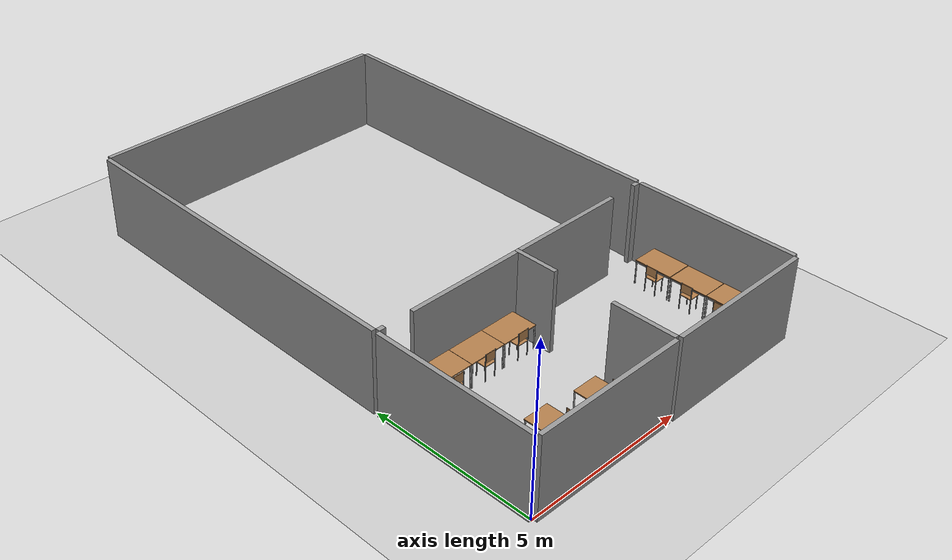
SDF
<sdf version="1.7">
 <world name="default">
  <light name="sun" type="directional">
   <pose>0 0 10 0 -0 0</pose>
   <diffuse>0.8 0.8 0.8 1</diffuse>
   <specular>0.2 0.2 0.2 1</specular>
   <attenuation>
    <range>1000</range>
    <constant>0.9</constant>
    <linear>0.01</linear>
    <quadratic>0.001</quadratic>
   </attenuation>
   <direction>-0.5 0.1 -0.9</direction>
   <spot><inner_angle>0</inner_angle><outer_angle>0</outer_angle><falloff>0</falloff></spot>
  </light>
  <model name="ground_plane">
   <static>1</static>
   <link name="link">
    <collision name="collision">
     <geometry><plane><normal>0 0 1</normal><size>100 100</size></plane></geometry>
     <surface>
      <contact><collide_bitmask>65535</collide_bitmask></contact>
      <friction><ode><mu>100</mu><mu2>50</mu2></ode></friction>
     </surface>
    </collision>
    <visual name="visual">
     <cast_shadows>0</cast_shadows>
     <geometry><plane><normal>0 0 1</normal><size>100 100</size></plane></geometry>
     <material>
      <script><uri>file://media/materials/scripts/gazebo.material</uri><name>Gazebo/Grey</name></script>
     </material>
    </visual>
   </link>
  </model>
  <gravity>0 0 -9.8</gravity>
  <magnetic_field>6e-06 2.3e-05 -4.2e-05</magnetic_field>
  <atmosphere type="adiabatic"/>
  <physics type="ode">
   <max_step_size>0.001</max_step_size>
   <real_time_factor>1</real_time_factor>
   <real_time_update_rate>1000</real_time_update_rate>
  </physics>
  <scene><ambient>0.4 0.4 0.4 1</ambient><background>0.7 0.7 0.7 1</background><shadows>1</shadows></scene>
  <spherical_coordinates>
   <surface_model>EARTH_WGS84</surface_model>
   <latitude_deg>0</latitude_deg>
   <longitude_deg>0</longitude_deg>
   <elevation>0</elevation>
   <heading_deg>0</heading_deg>
  </spherical_coordinates>
  <model name="wall2">
   <pose>4.78373 10.5765 0 0 -0 1.5708</pose>
   <link name="Wall_27">
    <collision name="Wall_27_Collision">
     <geometry><box><size>11 0.13 2.5</size></box></geometry>
     <pose>0 0 1.25 0 -0 0</pose>
    </collision>
    <visual name="Wall_27_Visual">
     <pose>0 0 1.25 0 -0 0</pose>
     <geometry><box><size>11 0.13 2.5</size></box></geometry>
     <material>
      <script><uri>file://media/materials/scripts/gazebo.material</uri><name>Gazebo/Grey</name></script>
      <ambient>1 1 1 1</ambient>
     </material>
     <meta><layer>0</layer></meta>
    </visual>
    <pose>-0.064778 4.81014 0 0 -0 0</pose>
   </link>
   <link name="Wall_29">
    <collision name="Wall_29_Collision">
     <geometry><box><size>9.49 0.13 2.5</size></box></geometry>
     <pose>0 0 1.25 0 -0 0</pose>
    </collision>
    <visual name="Wall_29_Visual">
     <pose>0 0 1.25 0 -0 0</pose>
     <geometry><box><size>9.49 0.13 2.5</size></box></geometry>
     <material>
      <script><uri>file://media/materials/scripts/gazebo.material</uri><name>Gazebo/Grey</name></script>
      <ambient>1 1 1 1</ambient>
     </material>
     <meta><layer>0</layer></meta>
    </visual>
    <pose>5.50002 7.4e-05 0 0 -0 -1.5708</pose>
   </link>
   <link name="Wall_31">
    <collision name="Wall_31_Collision">
     <geometry><box><size>11 0.13 2.5</size></box></geometry>
     <pose>0 0 1.25 0 -0 0</pose>
    </collision>
    <visual name="Wall_31_Visual">
     <pose>0 0 1.25 0 -0 0</pose>
     <geometry><box><size>11 0.13 2.5</size></box></geometry>
     <material>
      <script><uri>file://media/materials/scripts/gazebo.material</uri><name>Gazebo/Grey</name></script>
      <ambient>1 1 1 1</ambient>
     </material>
     <meta><layer>0</layer></meta>
    </visual>
    <pose>-0.065021 -4.81014 0 0 -0 0</pose>
   </link>
   <static>1</static>
  </model>
  <model name="wall">
   <link name="Wall_0">
    <pose>-2.51458 2.40421 0 0 0 -1.5708</pose>
    <visual name="Wall_0_Visual">
     <pose>0 0 1.25 0 -0 0</pose>
     <geometry><box><size>4.68 0.13 2.5</size></box></geometry>
     <material>
      <script><uri>file://media/materials/scripts/gazebo.material</uri><name>Gazebo/Grey</name></script>
      <ambient>1 1 1 1</ambient>
      <shader type="pixel"/>
     </material>
     <meta><layer>0</layer></meta>
    </visual>
    <collision name="Wall_0_Collision">
     <pose>0 0 1.25 0 -0 0</pose>
     <geometry><box><size>4.68 0.13 2.5</size></box></geometry>
     <surface>
      <friction>
       <ode><mu>1</mu><mu2>1</mu2><fdir1>0 0 0</fdir1><slip1>0</slip1><slip2>0</slip2></ode>
       <torsional>
        <coefficient>1</coefficient>
        <patch_radius>0</patch_radius>
        <surface_radius>0</surface_radius>
        <use_patch_radius>1</use_patch_radius>
        <ode><slip>0</slip></ode>
       </torsional>
      </friction>
      <bounce><restitution_coefficient>0</restitution_coefficient><threshold>1e+06</threshold></bounce>
      <contact>
       <collide_without_contact>0</collide_without_contact>
       <collide_without_contact_bitmask>1</collide_without_contact_bitmask>
       <collide_bitmask>1</collide_bitmask>
       <ode>
        <soft_cfm>0</soft_cfm>
        <soft_erp>0.2</soft_erp>
        <kp>1e+13</kp>
        <kd>1</kd>
        <max_vel>0.01</max_vel>
        <min_depth>0</min_depth>
       </ode>
       <bullet>
        <split_impulse>1</split_impulse>
        <split_impulse_penetration_threshold>-0.01</split_impulse_penetration_threshold>
        <soft_cfm>0</soft_cfm>
        <soft_erp>0.2</soft_erp>
        <kp>1e+13</kp>
        <kd>1</kd>
       </bullet>
      </contact>
     </surface>
    </collision>
   </link>
   <link name="Wall_11">
    <pose>-0.000844 -4.80859 0 0 -0 0</pose>
    <visual name="Wall_11_Visual">
     <pose>0 0 1.25 0 -0 0</pose>
     <geometry><box><size>4.9 0.13 2.5</size></box></geometry>
     <material>
      <script><uri>file://media/materials/scripts/gazebo.material</uri><name>Gazebo/Grey</name></script>
      <ambient>1 1 1 1</ambient>
      <shader type="pixel"/>
     </material>
     <meta><layer>0</layer></meta>
    </visual>
    <collision name="Wall_11_Collision">
     <pose>0 0 1.25 0 -0 0</pose>
     <geometry><box><size>4.9 0.13 2.5</size></box></geometry>
     <surface>
      <friction>
       <ode><mu>1</mu><mu2>1</mu2><fdir1>0 0 0</fdir1><slip1>0</slip1><slip2>0</slip2></ode>
       <torsional>
        <coefficient>1</coefficient>
        <patch_radius>0</patch_radius>
        <surface_radius>0</surface_radius>
        <use_patch_radius>1</use_patch_radius>
        <ode><slip>0</slip></ode>
       </torsional>
      </friction>
      <bounce><restitution_coefficient>0</restitution_coefficient><threshold>1e+06</threshold></bounce>
      <contact>
       <collide_without_contact>0</collide_without_contact>
       <collide_without_contact_bitmask>1</collide_without_contact_bitmask>
       <collide_bitmask>1</collide_bitmask>
       <ode>
        <soft_cfm>0</soft_cfm>
        <soft_erp>0.2</soft_erp>
        <kp>1e+13</kp>
        <kd>1</kd>
        <max_vel>0.01</max_vel>
        <min_depth>0</min_depth>
       </ode>
       <bullet>
        <split_impulse>1</split_impulse>
        <split_impulse_penetration_threshold>-0.01</split_impulse_penetration_threshold>
        <soft_cfm>0</soft_cfm>
        <soft_erp>0.2</soft_erp>
        <kp>1e+13</kp>
        <kd>1</kd>
       </bullet>
      </contact>
     </surface>
    </collision>
   </link>
   <link name="Wall_15">
    <pose>2.51323 -4.64302 0 0 0 -1.5708</pose>
    <visual name="Wall_15_Visual">
     <pose>0 0 1.25 0 -0 0</pose>
     <geometry><box><size>0.2 0.13 2.5</size></box></geometry>
     <material>
      <script><uri>file://media/materials/scripts/gazebo.material</uri><name>Gazebo/Grey</name></script>
      <ambient>1 1 1 1</ambient>
      <shader type="pixel"/>
     </material>
     <meta><layer>0</layer></meta>
    </visual>
    <collision name="Wall_15_Collision">
     <pose>0 0 1.25 0 -0 0</pose>
     <geometry><box><size>0.2 0.13 2.5</size></box></geometry>
     <surface>
      <friction>
       <ode><mu>1</mu><mu2>1</mu2><fdir1>0 0 0</fdir1><slip1>0</slip1><slip2>0</slip2></ode>
       <torsional>
        <coefficient>1</coefficient>
        <patch_radius>0</patch_radius>
        <surface_radius>0</surface_radius>
        <use_patch_radius>1</use_patch_radius>
        <ode><slip>0</slip></ode>
       </torsional>
      </friction>
      <bounce><restitution_coefficient>0</restitution_coefficient><threshold>1e+06</threshold></bounce>
      <contact>
       <collide_without_contact>0</collide_without_contact>
       <collide_without_contact_bitmask>1</collide_without_contact_bitmask>
       <collide_bitmask>1</collide_bitmask>
       <ode>
        <soft_cfm>0</soft_cfm>
        <soft_erp>0.2</soft_erp>
        <kp>1e+13</kp>
        <kd>1</kd>
        <max_vel>0.01</max_vel>
        <min_depth>0</min_depth>
       </ode>
       <bullet>
        <split_impulse>1</split_impulse>
        <split_impulse_penetration_threshold>-0.01</split_impulse_penetration_threshold>
        <soft_cfm>0</soft_cfm>
        <soft_erp>0.2</soft_erp>
        <kp>1e+13</kp>
        <kd>1</kd>
       </bullet>
      </contact>
     </surface>
    </collision>
   </link>
   <link name="Wall_17">
    <pose>2.5147 4.64359 0 0 0 -1.5708</pose>
    <visual name="Wall_17_Visual">
     <pose>0 0 1.25 0 -0 0</pose>
     <geometry><box><size>0.2 0.13 2.5</size></box></geometry>
     <material>
      <script><uri>file://media/materials/scripts/gazebo.material</uri><name>Gazebo/Grey</name></script>
      <ambient>1 1 1 1</ambient>
      <shader type="pixel"/>
     </material>
     <meta><layer>0</layer></meta>
    </visual>
    <collision name="Wall_17_Collision">
     <pose>0 0 1.25 0 -0 0</pose>
     <geometry><box><size>0.2 0.13 2.5</size></box></geometry>
     <surface>
      <friction>
       <ode><mu>1</mu><mu2>1</mu2><fdir1>0 0 0</fdir1><slip1>0</slip1><slip2>0</slip2></ode>
       <torsional>
        <coefficient>1</coefficient>
        <patch_radius>0</patch_radius>
        <surface_radius>0</surface_radius>
        <use_patch_radius>1</use_patch_radius>
        <ode><slip>0</slip></ode>
       </torsional>
      </friction>
      <bounce><restitution_coefficient>0</restitution_coefficient><threshold>1e+06</threshold></bounce>
      <contact>
       <collide_without_contact>0</collide_without_contact>
       <collide_without_contact_bitmask>1</collide_without_contact_bitmask>
       <collide_bitmask>1</collide_bitmask>
       <ode>
        <soft_cfm>0</soft_cfm>
        <soft_erp>0.2</soft_erp>
        <kp>1e+13</kp>
        <kd>1</kd>
        <max_vel>0.01</max_vel>
        <min_depth>0</min_depth>
       </ode>
       <bullet>
        <split_impulse>1</split_impulse>
        <split_impulse_penetration_threshold>-0.01</split_impulse_penetration_threshold>
        <soft_cfm>0</soft_cfm>
        <soft_erp>0.2</soft_erp>
        <kp>1e+13</kp>
        <kd>1</kd>
       </bullet>
      </contact>
     </surface>
    </collision>
   </link>
   <link name="Wall_19">
    <pose>2.51201 -1.86467 0 0 0 -1.5708</pose>
    <visual name="Wall_19_Visual">
     <pose>0 0 1.25 0 -0 0</pose>
     <geometry><box><size>3.6 0.13 2.5</size></box></geometry>
     <material>
      <script><uri>file://media/materials/scripts/gazebo.material</uri><name>Gazebo/Grey</name></script>
      <ambient>1 1 1 1</ambient>
      <shader type="pixel"/>
     </material>
     <meta><layer>0</layer></meta>
    </visual>
    <collision name="Wall_19_Collision">
     <pose>0 0 1.25 0 -0 0</pose>
     <geometry><box><size>3.6 0.13 2.5</size></box></geometry>
     <surface>
      <friction>
       <ode><mu>1</mu><mu2>1</mu2><fdir1>0 0 0</fdir1><slip1>0</slip1><slip2>0</slip2></ode>
       <torsional>
        <coefficient>1</coefficient>
        <patch_radius>0</patch_radius>
        <surface_radius>0</surface_radius>
        <use_patch_radius>1</use_patch_radius>
        <ode><slip>0</slip></ode>
       </torsional>
      </friction>
      <bounce><restitution_coefficient>0</restitution_coefficient><threshold>1e+06</threshold></bounce>
      <contact>
       <collide_without_contact>0</collide_without_contact>
       <collide_without_contact_bitmask>1</collide_without_contact_bitmask>
       <collide_bitmask>1</collide_bitmask>
       <ode>
        <soft_cfm>0</soft_cfm>
        <soft_erp>0.2</soft_erp>
        <kp>1e+13</kp>
        <kd>1</kd>
        <max_vel>0.01</max_vel>
        <min_depth>0</min_depth>
       </ode>
       <bullet>
        <split_impulse>1</split_impulse>
        <split_impulse_penetration_threshold>-0.01</split_impulse_penetration_threshold>
        <soft_cfm>0</soft_cfm>
        <soft_erp>0.2</soft_erp>
        <kp>1e+13</kp>
        <kd>1</kd>
       </bullet>
      </contact>
     </surface>
    </collision>
   </link>
   <link name="Wall_21">
    <pose>1.91206 -0.000123 0 0 -0 0</pose>
    <inertial>
     <mass>1</mass>
     <inertia><ixx>1</ixx><ixy>0</ixy><ixz>0</ixz><iyy>1</iyy><iyz>0</iyz><izz>1</izz></inertia>
    </inertial>
    <visual name="Wall_21_Visual">
     <pose>0 0 1.25 0 -0 0</pose>
     <geometry><box><size>1.33 0.13 2.5</size></box></geometry>
     <material>
      <script><uri>file://media/materials/scripts/gazebo.material</uri><name>Gazebo/Grey</name></script>
      <ambient>1 1 1 1</ambient>
      <shader type="pixel"><normal_map>__default__</normal_map></shader>
      <diffuse>0.7 0.7 0.7 1</diffuse>
      <specular>0.01 0.01 0.01 1</specular>
      <emissive>0 0 0 1</emissive>
     </material>
     <meta><layer>0</layer></meta>
    </visual>
    <collision name="Wall_21_Collision">
     <pose>0 0 1.25 0 -0 0</pose>
     <geometry><box><size>1.33 0.13 2.5</size></box></geometry>
     <surface>
      <friction>
       <ode><mu>1</mu><mu2>1</mu2><fdir1>0 0 0</fdir1><slip1>0</slip1><slip2>0</slip2></ode>
       <torsional>
        <coefficient>1</coefficient>
        <patch_radius>0</patch_radius>
        <surface_radius>0</surface_radius>
        <use_patch_radius>1</use_patch_radius>
        <ode><slip>0</slip></ode>
       </torsional>
      </friction>
      <bounce><restitution_coefficient>0</restitution_coefficient><threshold>1e+06</threshold></bounce>
      <contact>
       <collide_without_contact>0</collide_without_contact>
       <collide_without_contact_bitmask>1</collide_without_contact_bitmask>
       <collide_bitmask>1</collide_bitmask>
       <ode>
        <soft_cfm>0</soft_cfm>
        <soft_erp>0.2</soft_erp>
        <kp>1e+13</kp>
        <kd>1</kd>
        <max_vel>0.01</max_vel>
        <min_depth>0</min_depth>
       </ode>
       <bullet>
        <split_impulse>1</split_impulse>
        <split_impulse_penetration_threshold>-0.01</split_impulse_penetration_threshold>
        <soft_cfm>0</soft_cfm>
        <soft_erp>0.2</soft_erp>
        <kp>1e+13</kp>
        <kd>1</kd>
       </bullet>
      </contact>
     </surface>
    </collision>
   </link>
   <link name="Wall_23">
    <pose>2.51167 1.86479 0 0 0 -1.5708</pose>
    <visual name="Wall_23_Visual">
     <pose>0 0 1.25 0 -0 0</pose>
     <geometry><box><size>3.6 0.13 2.5</size></box></geometry>
     <material>
      <script><uri>file://media/materials/scripts/gazebo.material</uri><name>Gazebo/Grey</name></script>
      <ambient>1 1 1 1</ambient>
      <shader type="pixel"/>
     </material>
     <meta><layer>0</layer></meta>
    </visual>
    <collision name="Wall_23_Collision">
     <pose>0 0 1.25 0 -0 0</pose>
     <geometry><box><size>3.6 0.13 2.5</size></box></geometry>
     <surface>
      <friction>
       <ode><mu>1</mu><mu2>1</mu2><fdir1>0 0 0</fdir1><slip1>0</slip1><slip2>0</slip2></ode>
       <torsional>
        <coefficient>1</coefficient>
        <patch_radius>0</patch_radius>
        <surface_radius>0</surface_radius>
        <use_patch_radius>1</use_patch_radius>
        <ode><slip>0</slip></ode>
       </torsional>
      </friction>
      <bounce><restitution_coefficient>0</restitution_coefficient><threshold>1e+06</threshold></bounce>
      <contact>
       <collide_without_contact>0</collide_without_contact>
       <collide_without_contact_bitmask>1</collide_without_contact_bitmask>
       <collide_bitmask>1</collide_bitmask>
       <ode>
        <soft_cfm>0</soft_cfm>
        <soft_erp>0.2</soft_erp>
        <kp>1e+13</kp>
        <kd>1</kd>
        <max_vel>0.01</max_vel>
        <min_depth>0</min_depth>
       </ode>
       <bullet>
        <split_impulse>1</split_impulse>
        <split_impulse_penetration_threshold>-0.01</split_impulse_penetration_threshold>
        <soft_cfm>0</soft_cfm>
        <soft_erp>0.2</soft_erp>
        <kp>1e+13</kp>
        <kd>1</kd>
       </bullet>
      </contact>
     </surface>
    </collision>
   </link>
   <link name="Wall_3">
    <pose>-0.000301 4.80859 0 0 -0 3.14159</pose>
    <visual name="Wall_3_Visual">
     <pose>0 0 1.25 0 -0 0</pose>
     <geometry><box><size>4.9 0.13 2.5</size></box></geometry>
     <material>
      <script><uri>file://media/materials/scripts/gazebo.material</uri><name>Gazebo/Grey</name></script>
      <ambient>1 1 1 1</ambient>
      <shader type="pixel"/>
     </material>
     <meta><layer>0</layer></meta>
    </visual>
    <collision name="Wall_3_Collision">
     <pose>0 0 1.25 0 -0 0</pose>
     <geometry><box><size>4.9 0.13 2.5</size></box></geometry>
     <surface>
      <friction>
       <ode><mu>1</mu><mu2>1</mu2><fdir1>0 0 0</fdir1><slip1>0</slip1><slip2>0</slip2></ode>
       <torsional>
        <coefficient>1</coefficient>
        <patch_radius>0</patch_radius>
        <surface_radius>0</surface_radius>
        <use_patch_radius>1</use_patch_radius>
        <ode><slip>0</slip></ode>
       </torsional>
      </friction>
      <bounce><restitution_coefficient>0</restitution_coefficient><threshold>1e+06</threshold></bounce>
      <contact>
       <collide_without_contact>0</collide_without_contact>
       <collide_without_contact_bitmask>1</collide_without_contact_bitmask>
       <collide_bitmask>1</collide_bitmask>
       <ode>
        <soft_cfm>0</soft_cfm>
        <soft_erp>0.2</soft_erp>
        <kp>1e+13</kp>
        <kd>1</kd>
        <max_vel>0.01</max_vel>
        <min_depth>0</min_depth>
       </ode>
       <bullet>
        <split_impulse>1</split_impulse>
        <split_impulse_penetration_threshold>-0.01</split_impulse_penetration_threshold>
        <soft_cfm>0</soft_cfm>
        <soft_erp>0.2</soft_erp>
        <kp>1e+13</kp>
        <kd>1</kd>
       </bullet>
      </contact>
     </surface>
    </collision>
   </link>
   <link name="Wall_7">
    <pose>-1.49943 -0.000182 0 0 -0 0</pose>
    <visual name="Wall_7_Visual">
     <pose>0 0 1.25 0 -0 0</pose>
     <geometry><box><size>1.9 0.13 2.5</size></box></geometry>
     <material>
      <script><uri>file://media/materials/scripts/gazebo.material</uri><name>Gazebo/Grey</name></script>
      <ambient>1 1 1 1</ambient>
      <shader type="pixel"/>
     </material>
     <meta><layer>0</layer></meta>
    </visual>
    <collision name="Wall_7_Collision">
     <pose>0 0 1.25 0 -0 0</pose>
     <geometry><box><size>1.9 0.13 2.5</size></box></geometry>
     <surface>
      <friction>
       <ode><mu>1</mu><mu2>1</mu2><fdir1>0 0 0</fdir1><slip1>0</slip1><slip2>0</slip2></ode>
       <torsional>
        <coefficient>1</coefficient>
        <patch_radius>0</patch_radius>
        <surface_radius>0</surface_radius>
        <use_patch_radius>1</use_patch_radius>
        <ode><slip>0</slip></ode>
       </torsional>
      </friction>
      <bounce><restitution_coefficient>0</restitution_coefficient><threshold>1e+06</threshold></bounce>
      <contact>
       <collide_without_contact>0</collide_without_contact>
       <collide_without_contact_bitmask>1</collide_without_contact_bitmask>
       <collide_bitmask>1</collide_bitmask>
       <ode>
        <soft_cfm>0</soft_cfm>
        <soft_erp>0.2</soft_erp>
        <kp>1e+13</kp>
        <kd>1</kd>
        <max_vel>0.01</max_vel>
        <min_depth>0</min_depth>
       </ode>
       <bullet>
        <split_impulse>1</split_impulse>
        <split_impulse_penetration_threshold>-0.01</split_impulse_penetration_threshold>
        <soft_cfm>0</soft_cfm>
        <soft_erp>0.2</soft_erp>
        <kp>1e+13</kp>
        <kd>1</kd>
       </bullet>
      </contact>
     </surface>
    </collision>
   </link>
   <link name="Wall_9">
    <pose>-2.5147 -2.40399 0 0 0 -1.5708</pose>
    <visual name="Wall_9_Visual">
     <pose>0 0 1.25 0 -0 0</pose>
     <geometry><box><size>4.68 0.13 2.5</size></box></geometry>
     <material>
      <script><uri>file://media/materials/scripts/gazebo.material</uri><name>Gazebo/Grey</name></script>
      <ambient>1 1 1 1</ambient>
      <shader type="pixel"/>
     </material>
     <meta><layer>0</layer></meta>
    </visual>
    <collision name="Wall_9_Collision">
     <pose>0 0 1.25 0 -0 0</pose>
     <geometry><box><size>4.68 0.13 2.5</size></box></geometry>
     <surface>
      <friction>
       <ode><mu>1</mu><mu2>1</mu2><fdir1>0 0 0</fdir1><slip1>0</slip1><slip2>0</slip2></ode>
       <torsional>
        <coefficient>1</coefficient>
        <patch_radius>0</patch_radius>
        <surface_radius>0</surface_radius>
        <use_patch_radius>1</use_patch_radius>
        <ode><slip>0</slip></ode>
       </torsional>
      </friction>
      <bounce><restitution_coefficient>0</restitution_coefficient><threshold>1e+06</threshold></bounce>
      <contact>
       <collide_without_contact>0</collide_without_contact>
       <collide_without_contact_bitmask>1</collide_without_contact_bitmask>
       <collide_bitmask>1</collide_bitmask>
       <ode>
        <soft_cfm>0</soft_cfm>
        <soft_erp>0.2</soft_erp>
        <kp>1e+13</kp>
        <kd>1</kd>
        <max_vel>0.01</max_vel>
        <min_depth>0</min_depth>
       </ode>
       <bullet>
        <split_impulse>1</split_impulse>
        <split_impulse_penetration_threshold>-0.01</split_impulse_penetration_threshold>
        <soft_cfm>0</soft_cfm>
        <soft_erp>0.2</soft_erp>
        <kp>1e+13</kp>
        <kd>1</kd>
       </bullet>
      </contact>
     </surface>
    </collision>
   </link>
   <static>1</static>
   <pose>4.78457 2.43427 0 0 -0 1.5708</pose>
  </model>
  <model name="table_mod">
   <link name="link">
    <inertial>
     <mass>1</mass>
     <inertia><ixx>1</ixx><ixy>0</ixy><ixz>0</ixz><iyy>1</iyy><iyz>0</iyz><izz>1</izz></inertia>
    </inertial>
    <visual name="visual1">
     <pose>0 0 0.87 0 -0 0</pose>
     <geometry><box><size>1.15 0.8 0.03</size></box></geometry>
     <material>
      <script><uri>file://media/materials/scripts/gazebo.material</uri><name>Gazebo/Wood</name></script>
      <shader type="pixel"><normal_map>__default__</normal_map></shader>
      <ambient>1 1 1 1</ambient>
      <diffuse>1 1 1 1</diffuse>
      <specular>0.2 0.2 0.2 1</specular>
      <emissive>0 0 0 1</emissive>
     </material>
    </visual>
    <visual name="back_right_leg">
     <pose>-0.55 -0.38 0.5 0 -0 0</pose>
     <geometry><cylinder><radius>0.02</radius><length>0.75</length></cylinder></geometry>
     <material>
      <script><uri>file://media/materials/scripts/gazebo.material</uri><name>Gazebo/Grey</name></script>
      <shader type="pixel"><normal_map>__default__</normal_map></shader>
      <ambient>0.3 0.3 0.3 1</ambient>
      <diffuse>0.7 0.7 0.7 1</diffuse>
      <specular>0.01 0.01 0.01 1</specular>
      <emissive>0 0 0 1</emissive>
     </material>
    </visual>
    <visual name="front_right_leg">
     <pose>0.55 -0.38 0.5 0 -0 0</pose>
     <geometry><cylinder><radius>0.02</radius><length>0.75</length></cylinder></geometry>
     <material>
      <script><uri>file://media/materials/scripts/gazebo.material</uri><name>Gazebo/Grey</name></script>
      <shader type="pixel"><normal_map>__default__</normal_map></shader>
      <ambient>0.3 0.3 0.3 1</ambient>
      <diffuse>0.7 0.7 0.7 1</diffuse>
      <specular>0.01 0.01 0.01 1</specular>
      <emissive>0 0 0 1</emissive>
     </material>
    </visual>
    <visual name="back_left_leg">
     <pose>-0.55 0.38 0.5 0 -0 0</pose>
     <geometry><cylinder><radius>0.02</radius><length>0.75</length></cylinder></geometry>
     <material>
      <script><uri>file://media/materials/scripts/gazebo.material</uri><name>Gazebo/Grey</name></script>
      <shader type="pixel"><normal_map>__default__</normal_map></shader>
      <ambient>0.3 0.3 0.3 1</ambient>
      <diffuse>0.7 0.7 0.7 1</diffuse>
      <specular>0.01 0.01 0.01 1</specular>
      <emissive>0 0 0 1</emissive>
     </material>
    </visual>
    <visual name="front_left_leg">
     <pose>0.55 0.38 0.5 0 -0 0</pose>
     <geometry><cylinder><radius>0.02</radius><length>0.75</length></cylinder></geometry>
     <material>
      <script><uri>file://media/materials/scripts/gazebo.material</uri><name>Gazebo/Grey</name></script>
      <shader type="pixel"><normal_map>__default__</normal_map></shader>
      <ambient>0.3 0.3 0.3 1</ambient>
      <diffuse>0.7 0.7 0.7 1</diffuse>
      <specular>0.01 0.01 0.01 1</specular>
      <emissive>0 0 0 1</emissive>
     </material>
    </visual>
    <collision name="surface">
     <pose>0 0 0.87 0 -0 0</pose>
     <geometry><box><size>1.15 0.8 0.03</size></box></geometry>
     <surface>
      <friction>
       <ode><mu>0.6</mu><mu2>0.6</mu2><fdir1>0 0 0</fdir1><slip1>0</slip1><slip2>0</slip2></ode>
       <torsional>
        <coefficient>1</coefficient>
        <patch_radius>0</patch_radius>
        <surface_radius>0</surface_radius>
        <use_patch_radius>1</use_patch_radius>
        <ode><slip>0</slip></ode>
       </torsional>
      </friction>
      <bounce><restitution_coefficient>0</restitution_coefficient><threshold>1e+06</threshold></bounce>
      <contact>
       <collide_without_contact>0</collide_without_contact>
       <collide_without_contact_bitmask>1</collide_without_contact_bitmask>
       <collide_bitmask>1</collide_bitmask>
       <ode>
        <soft_cfm>0</soft_cfm>
        <soft_erp>0.2</soft_erp>
        <kp>1e+13</kp>
        <kd>1</kd>
        <max_vel>0.01</max_vel>
        <min_depth>0</min_depth>
       </ode>
       <bullet>
        <split_impulse>1</split_impulse>
        <split_impulse_penetration_threshold>-0.01</split_impulse_penetration_threshold>
        <soft_cfm>0</soft_cfm>
        <soft_erp>0.2</soft_erp>
        <kp>1e+13</kp>
        <kd>1</kd>
       </bullet>
      </contact>
     </surface>
    </collision>
    <collision name="back_right_leg">
     <pose>-0.55 -0.38 0.5 0 -0 0</pose>
     <geometry><cylinder><radius>0.02</radius><length>0.75</length></cylinder></geometry>
     <surface>
      <friction>
       <ode><mu>1</mu><mu2>1</mu2><fdir1>0 0 0</fdir1><slip1>0</slip1><slip2>0</slip2></ode>
       <torsional>
        <coefficient>1</coefficient>
        <patch_radius>0</patch_radius>
        <surface_radius>0</surface_radius>
        <use_patch_radius>1</use_patch_radius>
        <ode><slip>0</slip></ode>
       </torsional>
      </friction>
      <bounce><restitution_coefficient>0</restitution_coefficient><threshold>1e+06</threshold></bounce>
      <contact>
       <collide_without_contact>0</collide_without_contact>
       <collide_without_contact_bitmask>1</collide_without_contact_bitmask>
       <collide_bitmask>1</collide_bitmask>
       <ode>
        <soft_cfm>0</soft_cfm>
        <soft_erp>0.2</soft_erp>
        <kp>1e+13</kp>
        <kd>1</kd>
        <max_vel>0.01</max_vel>
        <min_depth>0</min_depth>
       </ode>
       <bullet>
        <split_impulse>1</split_impulse>
        <split_impulse_penetration_threshold>-0.01</split_impulse_penetration_threshold>
        <soft_cfm>0</soft_cfm>
        <soft_erp>0.2</soft_erp>
        <kp>1e+13</kp>
        <kd>1</kd>
       </bullet>
      </contact>
     </surface>
    </collision>
    <collision name="back_left_leg">
     <pose>-0.55 0.38 0.5 0 -0 0</pose>
     <geometry><cylinder><radius>0.02</radius><length>0.75</length></cylinder></geometry>
     <surface>
      <friction>
       <ode><mu>1</mu><mu2>1</mu2><fdir1>0 0 0</fdir1><slip1>0</slip1><slip2>0</slip2></ode>
       <torsional>
        <coefficient>1</coefficient>
        <patch_radius>0</patch_radius>
        <surface_radius>0</surface_radius>
        <use_patch_radius>1</use_patch_radius>
        <ode><slip>0</slip></ode>
       </torsional>
      </friction>
      <bounce><restitution_coefficient>0</restitution_coefficient><threshold>1e+06</threshold></bounce>
      <contact>
       <collide_without_contact>0</collide_without_contact>
       <collide_without_contact_bitmask>1</collide_without_contact_bitmask>
       <collide_bitmask>1</collide_bitmask>
       <ode>
        <soft_cfm>0</soft_cfm>
        <soft_erp>0.2</soft_erp>
        <kp>1e+13</kp>
        <kd>1</kd>
        <max_vel>0.01</max_vel>
        <min_depth>0</min_depth>
       </ode>
       <bullet>
        <split_impulse>1</split_impulse>
        <split_impulse_penetration_threshold>-0.01</split_impulse_penetration_threshold>
        <soft_cfm>0</soft_cfm>
        <soft_erp>0.2</soft_erp>
        <kp>1e+13</kp>
        <kd>1</kd>
       </bullet>
      </contact>
     </surface>
    </collision>
    <collision name="front_left_leg">
     <pose>0.55 0.38 0.5 0 -0 0</pose>
     <geometry><cylinder><radius>0.02</radius><length>0.75</length></cylinder></geometry>
     <surface>
      <friction>
       <ode><mu>1</mu><mu2>1</mu2><fdir1>0 0 0</fdir1><slip1>0</slip1><slip2>0</slip2></ode>
       <torsional>
        <coefficient>1</coefficient>
        <patch_radius>0</patch_radius>
        <surface_radius>0</surface_radius>
        <use_patch_radius>1</use_patch_radius>
        <ode><slip>0</slip></ode>
       </torsional>
      </friction>
      <bounce><restitution_coefficient>0</restitution_coefficient><threshold>1e+06</threshold></bounce>
      <contact>
       <collide_without_contact>0</collide_without_contact>
       <collide_without_contact_bitmask>1</collide_without_contact_bitmask>
       <collide_bitmask>1</collide_bitmask>
       <ode>
        <soft_cfm>0</soft_cfm>
        <soft_erp>0.2</soft_erp>
        <kp>1e+13</kp>
        <kd>1</kd>
        <max_vel>0.01</max_vel>
        <min_depth>0</min_depth>
       </ode>
       <bullet>
        <split_impulse>1</split_impulse>
        <split_impulse_penetration_threshold>-0.01</split_impulse_penetration_threshold>
        <soft_cfm>0</soft_cfm>
        <soft_erp>0.2</soft_erp>
        <kp>1e+13</kp>
        <kd>1</kd>
       </bullet>
      </contact>
     </surface>
    </collision>
    <collision name="front_right_leg">
     <pose>0.55 -0.38 0.5 0 -0 0</pose>
     <geometry><cylinder><radius>0.02</radius><length>0.75</length></cylinder></geometry>
     <surface>
      <friction>
       <ode><mu>1</mu><mu2>1</mu2><fdir1>0 0 0</fdir1><slip1>0</slip1><slip2>0</slip2></ode>
       <torsional>
        <coefficient>1</coefficient>
        <patch_radius>0</patch_radius>
        <surface_radius>0</surface_radius>
        <use_patch_radius>1</use_patch_radius>
        <ode><slip>0</slip></ode>
       </torsional>
      </friction>
      <bounce><restitution_coefficient>0</restitution_coefficient><threshold>1e+06</threshold></bounce>
      <contact>
       <collide_without_contact>0</collide_without_contact>
       <collide_without_contact_bitmask>1</collide_without_contact_bitmask>
       <collide_bitmask>1</collide_bitmask>
       <ode>
        <soft_cfm>0</soft_cfm>
        <soft_erp>0.2</soft_erp>
        <kp>1e+13</kp>
        <kd>1</kd>
        <max_vel>0.01</max_vel>
        <min_depth>0</min_depth>
       </ode>
       <bullet>
        <split_impulse>1</split_impulse>
        <split_impulse_penetration_threshold>-0.01</split_impulse_penetration_threshold>
        <soft_cfm>0</soft_cfm>
        <soft_erp>0.2</soft_erp>
        <kp>1e+13</kp>
        <kd>1</kd>
       </bullet>
      </contact>
     </surface>
    </collision>
   </link>
   <static>1</static>
   <pose>0.467778 0.712362 -0.134214 0 0 -1.5708</pose>
  </model>
  <model name="table_mod_clone">
   <link name="link">
    <inertial>
     <mass>1</mass>
     <inertia><ixx>1</ixx><ixy>0</ixy><ixz>0</ixz><iyy>1</iyy><iyz>0</iyz><izz>1</izz></inertia>
    </inertial>
    <visual name="visual1">
     <pose>0 0 0.87 0 -0 0</pose>
     <geometry><box><size>1.15 0.8 0.03</size></box></geometry>
     <material>
      <script><uri>file://media/materials/scripts/gazebo.material</uri><name>Gazebo/Wood</name></script>
      <shader type="pixel"><normal_map>__default__</normal_map></shader>
      <ambient>1 1 1 1</ambient>
      <diffuse>1 1 1 1</diffuse>
      <specular>0.2 0.2 0.2 1</specular>
      <emissive>0 0 0 1</emissive>
     </material>
    </visual>
    <visual name="back_right_leg">
     <pose>-0.55 -0.38 0.5 0 -0 0</pose>
     <geometry><cylinder><radius>0.02</radius><length>0.75</length></cylinder></geometry>
     <material>
      <script><uri>file://media/materials/scripts/gazebo.material</uri><name>Gazebo/Grey</name></script>
      <shader type="pixel"><normal_map>__default__</normal_map></shader>
      <ambient>0.3 0.3 0.3 1</ambient>
      <diffuse>0.7 0.7 0.7 1</diffuse>
      <specular>0.01 0.01 0.01 1</specular>
      <emissive>0 0 0 1</emissive>
     </material>
    </visual>
    <visual name="front_right_leg">
     <pose>0.55 -0.38 0.5 0 -0 0</pose>
     <geometry><cylinder><radius>0.02</radius><length>0.75</length></cylinder></geometry>
     <material>
      <script><uri>file://media/materials/scripts/gazebo.material</uri><name>Gazebo/Grey</name></script>
      <shader type="pixel"><normal_map>__default__</normal_map></shader>
      <ambient>0.3 0.3 0.3 1</ambient>
      <diffuse>0.7 0.7 0.7 1</diffuse>
      <specular>0.01 0.01 0.01 1</specular>
      <emissive>0 0 0 1</emissive>
     </material>
    </visual>
    <visual name="back_left_leg">
     <pose>-0.55 0.38 0.5 0 -0 0</pose>
     <geometry><cylinder><radius>0.02</radius><length>0.75</length></cylinder></geometry>
     <material>
      <script><uri>file://media/materials/scripts/gazebo.material</uri><name>Gazebo/Grey</name></script>
      <shader type="pixel"><normal_map>__default__</normal_map></shader>
      <ambient>0.3 0.3 0.3 1</ambient>
      <diffuse>0.7 0.7 0.7 1</diffuse>
      <specular>0.01 0.01 0.01 1</specular>
      <emissive>0 0 0 1</emissive>
     </material>
    </visual>
    <visual name="front_left_leg">
     <pose>0.55 0.38 0.5 0 -0 0</pose>
     <geometry><cylinder><radius>0.02</radius><length>0.75</length></cylinder></geometry>
     <material>
      <script><uri>file://media/materials/scripts/gazebo.material</uri><name>Gazebo/Grey</name></script>
      <shader type="pixel"><normal_map>__default__</normal_map></shader>
      <ambient>0.3 0.3 0.3 1</ambient>
      <diffuse>0.7 0.7 0.7 1</diffuse>
      <specular>0.01 0.01 0.01 1</specular>
      <emissive>0 0 0 1</emissive>
     </material>
    </visual>
    <collision name="surface">
     <pose>0 0 0.87 0 -0 0</pose>
     <geometry><box><size>1.15 0.8 0.03</size></box></geometry>
     <surface>
      <friction>
       <ode><mu>0.6</mu><mu2>0.6</mu2><fdir1>0 0 0</fdir1><slip1>0</slip1><slip2>0</slip2></ode>
       <torsional>
        <coefficient>1</coefficient>
        <patch_radius>0</patch_radius>
        <surface_radius>0</surface_radius>
        <use_patch_radius>1</use_patch_radius>
        <ode><slip>0</slip></ode>
       </torsional>
      </friction>
      <bounce><restitution_coefficient>0</restitution_coefficient><threshold>1e+06</threshold></bounce>
      <contact>
       <collide_without_contact>0</collide_without_contact>
       <collide_without_contact_bitmask>1</collide_without_contact_bitmask>
       <collide_bitmask>1</collide_bitmask>
       <ode>
        <soft_cfm>0</soft_cfm>
        <soft_erp>0.2</soft_erp>
        <kp>1e+13</kp>
        <kd>1</kd>
        <max_vel>0.01</max_vel>
        <min_depth>0</min_depth>
       </ode>
       <bullet>
        <split_impulse>1</split_impulse>
        <split_impulse_penetration_threshold>-0.01</split_impulse_penetration_threshold>
        <soft_cfm>0</soft_cfm>
        <soft_erp>0.2</soft_erp>
        <kp>1e+13</kp>
        <kd>1</kd>
       </bullet>
      </contact>
     </surface>
    </collision>
    <collision name="back_right_leg">
     <pose>-0.55 -0.38 0.5 0 -0 0</pose>
     <geometry><cylinder><radius>0.02</radius><length>0.75</length></cylinder></geometry>
     <surface>
      <friction>
       <ode><mu>1</mu><mu2>1</mu2><fdir1>0 0 0</fdir1><slip1>0</slip1><slip2>0</slip2></ode>
       <torsional>
        <coefficient>1</coefficient>
        <patch_radius>0</patch_radius>
        <surface_radius>0</surface_radius>
        <use_patch_radius>1</use_patch_radius>
        <ode><slip>0</slip></ode>
       </torsional>
      </friction>
      <bounce><restitution_coefficient>0</restitution_coefficient><threshold>1e+06</threshold></bounce>
      <contact>
       <collide_without_contact>0</collide_without_contact>
       <collide_without_contact_bitmask>1</collide_without_contact_bitmask>
       <collide_bitmask>1</collide_bitmask>
       <ode>
        <soft_cfm>0</soft_cfm>
        <soft_erp>0.2</soft_erp>
        <kp>1e+13</kp>
        <kd>1</kd>
        <max_vel>0.01</max_vel>
        <min_depth>0</min_depth>
       </ode>
       <bullet>
        <split_impulse>1</split_impulse>
        <split_impulse_penetration_threshold>-0.01</split_impulse_penetration_threshold>
        <soft_cfm>0</soft_cfm>
        <soft_erp>0.2</soft_erp>
        <kp>1e+13</kp>
        <kd>1</kd>
       </bullet>
      </contact>
     </surface>
    </collision>
    <collision name="back_left_leg">
     <pose>-0.55 0.38 0.5 0 -0 0</pose>
     <geometry><cylinder><radius>0.02</radius><length>0.75</length></cylinder></geometry>
     <surface>
      <friction>
       <ode><mu>1</mu><mu2>1</mu2><fdir1>0 0 0</fdir1><slip1>0</slip1><slip2>0</slip2></ode>
       <torsional>
        <coefficient>1</coefficient>
        <patch_radius>0</patch_radius>
        <surface_radius>0</surface_radius>
        <use_patch_radius>1</use_patch_radius>
        <ode><slip>0</slip></ode>
       </torsional>
      </friction>
      <bounce><restitution_coefficient>0</restitution_coefficient><threshold>1e+06</threshold></bounce>
      <contact>
       <collide_without_contact>0</collide_without_contact>
       <collide_without_contact_bitmask>1</collide_without_contact_bitmask>
       <collide_bitmask>1</collide_bitmask>
       <ode>
        <soft_cfm>0</soft_cfm>
        <soft_erp>0.2</soft_erp>
        <kp>1e+13</kp>
        <kd>1</kd>
        <max_vel>0.01</max_vel>
        <min_depth>0</min_depth>
       </ode>
       <bullet>
        <split_impulse>1</split_impulse>
        <split_impulse_penetration_threshold>-0.01</split_impulse_penetration_threshold>
        <soft_cfm>0</soft_cfm>
        <soft_erp>0.2</soft_erp>
        <kp>1e+13</kp>
        <kd>1</kd>
       </bullet>
      </contact>
     </surface>
    </collision>
    <collision name="front_left_leg">
     <pose>0.55 0.38 0.5 0 -0 0</pose>
     <geometry><cylinder><radius>0.02</radius><length>0.75</length></cylinder></geometry>
     <surface>
      <friction>
       <ode><mu>1</mu><mu2>1</mu2><fdir1>0 0 0</fdir1><slip1>0</slip1><slip2>0</slip2></ode>
       <torsional>
        <coefficient>1</coefficient>
        <patch_radius>0</patch_radius>
        <surface_radius>0</surface_radius>
        <use_patch_radius>1</use_patch_radius>
        <ode><slip>0</slip></ode>
       </torsional>
      </friction>
      <bounce><restitution_coefficient>0</restitution_coefficient><threshold>1e+06</threshold></bounce>
      <contact>
       <collide_without_contact>0</collide_without_contact>
       <collide_without_contact_bitmask>1</collide_without_contact_bitmask>
       <collide_bitmask>1</collide_bitmask>
       <ode>
        <soft_cfm>0</soft_cfm>
        <soft_erp>0.2</soft_erp>
        <kp>1e+13</kp>
        <kd>1</kd>
        <max_vel>0.01</max_vel>
        <min_depth>0</min_depth>
       </ode>
       <bullet>
        <split_impulse>1</split_impulse>
        <split_impulse_penetration_threshold>-0.01</split_impulse_penetration_threshold>
        <soft_cfm>0</soft_cfm>
        <soft_erp>0.2</soft_erp>
        <kp>1e+13</kp>
        <kd>1</kd>
       </bullet>
      </contact>
     </surface>
    </collision>
    <collision name="front_right_leg">
     <pose>0.55 -0.38 0.5 0 -0 0</pose>
     <geometry><cylinder><radius>0.02</radius><length>0.75</length></cylinder></geometry>
     <surface>
      <friction>
       <ode><mu>1</mu><mu2>1</mu2><fdir1>0 0 0</fdir1><slip1>0</slip1><slip2>0</slip2></ode>
       <torsional>
        <coefficient>1</coefficient>
        <patch_radius>0</patch_radius>
        <surface_radius>0</surface_radius>
        <use_patch_radius>1</use_patch_radius>
        <ode><slip>0</slip></ode>
       </torsional>
      </friction>
      <bounce><restitution_coefficient>0</restitution_coefficient><threshold>1e+06</threshold></bounce>
      <contact>
       <collide_without_contact>0</collide_without_contact>
       <collide_without_contact_bitmask>1</collide_without_contact_bitmask>
       <collide_bitmask>1</collide_bitmask>
       <ode>
        <soft_cfm>0</soft_cfm>
        <soft_erp>0.2</soft_erp>
        <kp>1e+13</kp>
        <kd>1</kd>
        <max_vel>0.01</max_vel>
        <min_depth>0</min_depth>
       </ode>
       <bullet>
        <split_impulse>1</split_impulse>
        <split_impulse_penetration_threshold>-0.01</split_impulse_penetration_threshold>
        <soft_cfm>0</soft_cfm>
        <soft_erp>0.2</soft_erp>
        <kp>1e+13</kp>
        <kd>1</kd>
       </bullet>
      </contact>
     </surface>
    </collision>
   </link>
   <static>1</static>
   <pose>0.469024 1.86683 -0.134214 0 0 -1.5708</pose>
  </model>
  <model name="table_mod_clone_0">
   <link name="link">
    <inertial>
     <mass>1</mass>
     <inertia><ixx>1</ixx><ixy>0</ixy><ixz>0</ixz><iyy>1</iyy><iyz>0</iyz><izz>1</izz></inertia>
    </inertial>
    <visual name="visual1">
     <pose>0 0 0.87 0 -0 0</pose>
     <geometry><box><size>1.15 0.8 0.03</size></box></geometry>
     <material>
      <script><uri>file://media/materials/scripts/gazebo.material</uri><name>Gazebo/Wood</name></script>
      <shader type="pixel"><normal_map>__default__</normal_map></shader>
      <ambient>1 1 1 1</ambient>
      <diffuse>1 1 1 1</diffuse>
      <specular>0.2 0.2 0.2 1</specular>
      <emissive>0 0 0 1</emissive>
     </material>
    </visual>
    <visual name="back_right_leg">
     <pose>-0.55 -0.38 0.5 0 -0 0</pose>
     <geometry><cylinder><radius>0.02</radius><length>0.75</length></cylinder></geometry>
     <material>
      <script><uri>file://media/materials/scripts/gazebo.material</uri><name>Gazebo/Grey</name></script>
      <shader type="pixel"><normal_map>__default__</normal_map></shader>
      <ambient>0.3 0.3 0.3 1</ambient>
      <diffuse>0.7 0.7 0.7 1</diffuse>
      <specular>0.01 0.01 0.01 1</specular>
      <emissive>0 0 0 1</emissive>
     </material>
    </visual>
    <visual name="front_right_leg">
     <pose>0.55 -0.38 0.5 0 -0 0</pose>
     <geometry><cylinder><radius>0.02</radius><length>0.75</length></cylinder></geometry>
     <material>
      <script><uri>file://media/materials/scripts/gazebo.material</uri><name>Gazebo/Grey</name></script>
      <shader type="pixel"><normal_map>__default__</normal_map></shader>
      <ambient>0.3 0.3 0.3 1</ambient>
      <diffuse>0.7 0.7 0.7 1</diffuse>
      <specular>0.01 0.01 0.01 1</specular>
      <emissive>0 0 0 1</emissive>
     </material>
    </visual>
    <visual name="back_left_leg">
     <pose>-0.55 0.38 0.5 0 -0 0</pose>
     <geometry><cylinder><radius>0.02</radius><length>0.75</length></cylinder></geometry>
     <material>
      <script><uri>file://media/materials/scripts/gazebo.material</uri><name>Gazebo/Grey</name></script>
      <shader type="pixel"><normal_map>__default__</normal_map></shader>
      <ambient>0.3 0.3 0.3 1</ambient>
      <diffuse>0.7 0.7 0.7 1</diffuse>
      <specular>0.01 0.01 0.01 1</specular>
      <emissive>0 0 0 1</emissive>
     </material>
    </visual>
    <visual name="front_left_leg">
     <pose>0.55 0.38 0.5 0 -0 0</pose>
     <geometry><cylinder><radius>0.02</radius><length>0.75</length></cylinder></geometry>
     <material>
      <script><uri>file://media/materials/scripts/gazebo.material</uri><name>Gazebo/Grey</name></script>
      <shader type="pixel"><normal_map>__default__</normal_map></shader>
      <ambient>0.3 0.3 0.3 1</ambient>
      <diffuse>0.7 0.7 0.7 1</diffuse>
      <specular>0.01 0.01 0.01 1</specular>
      <emissive>0 0 0 1</emissive>
     </material>
    </visual>
    <collision name="surface">
     <pose>0 0 0.87 0 -0 0</pose>
     <geometry><box><size>1.15 0.8 0.03</size></box></geometry>
     <surface>
      <friction>
       <ode><mu>0.6</mu><mu2>0.6</mu2><fdir1>0 0 0</fdir1><slip1>0</slip1><slip2>0</slip2></ode>
       <torsional>
        <coefficient>1</coefficient>
        <patch_radius>0</patch_radius>
        <surface_radius>0</surface_radius>
        <use_patch_radius>1</use_patch_radius>
        <ode><slip>0</slip></ode>
       </torsional>
      </friction>
      <bounce><restitution_coefficient>0</restitution_coefficient><threshold>1e+06</threshold></bounce>
      <contact>
       <collide_without_contact>0</collide_without_contact>
       <collide_without_contact_bitmask>1</collide_without_contact_bitmask>
       <collide_bitmask>1</collide_bitmask>
       <ode>
        <soft_cfm>0</soft_cfm>
        <soft_erp>0.2</soft_erp>
        <kp>1e+13</kp>
        <kd>1</kd>
        <max_vel>0.01</max_vel>
        <min_depth>0</min_depth>
       </ode>
       <bullet>
        <split_impulse>1</split_impulse>
        <split_impulse_penetration_threshold>-0.01</split_impulse_penetration_threshold>
        <soft_cfm>0</soft_cfm>
        <soft_erp>0.2</soft_erp>
        <kp>1e+13</kp>
        <kd>1</kd>
       </bullet>
      </contact>
     </surface>
    </collision>
    <collision name="back_right_leg">
     <pose>-0.55 -0.38 0.5 0 -0 0</pose>
     <geometry><cylinder><radius>0.02</radius><length>0.75</length></cylinder></geometry>
     <surface>
      <friction>
       <ode><mu>1</mu><mu2>1</mu2><fdir1>0 0 0</fdir1><slip1>0</slip1><slip2>0</slip2></ode>
       <torsional>
        <coefficient>1</coefficient>
        <patch_radius>0</patch_radius>
        <surface_radius>0</surface_radius>
        <use_patch_radius>1</use_patch_radius>
        <ode><slip>0</slip></ode>
       </torsional>
      </friction>
      <bounce><restitution_coefficient>0</restitution_coefficient><threshold>1e+06</threshold></bounce>
      <contact>
       <collide_without_contact>0</collide_without_contact>
       <collide_without_contact_bitmask>1</collide_without_contact_bitmask>
       <collide_bitmask>1</collide_bitmask>
       <ode>
        <soft_cfm>0</soft_cfm>
        <soft_erp>0.2</soft_erp>
        <kp>1e+13</kp>
        <kd>1</kd>
        <max_vel>0.01</max_vel>
        <min_depth>0</min_depth>
       </ode>
       <bullet>
        <split_impulse>1</split_impulse>
        <split_impulse_penetration_threshold>-0.01</split_impulse_penetration_threshold>
        <soft_cfm>0</soft_cfm>
        <soft_erp>0.2</soft_erp>
        <kp>1e+13</kp>
        <kd>1</kd>
       </bullet>
      </contact>
     </surface>
    </collision>
    <collision name="back_left_leg">
     <pose>-0.55 0.38 0.5 0 -0 0</pose>
     <geometry><cylinder><radius>0.02</radius><length>0.75</length></cylinder></geometry>
     <surface>
      <friction>
       <ode><mu>1</mu><mu2>1</mu2><fdir1>0 0 0</fdir1><slip1>0</slip1><slip2>0</slip2></ode>
       <torsional>
        <coefficient>1</coefficient>
        <patch_radius>0</patch_radius>
        <surface_radius>0</surface_radius>
        <use_patch_radius>1</use_patch_radius>
        <ode><slip>0</slip></ode>
       </torsional>
      </friction>
      <bounce><restitution_coefficient>0</restitution_coefficient><threshold>1e+06</threshold></bounce>
      <contact>
       <collide_without_contact>0</collide_without_contact>
       <collide_without_contact_bitmask>1</collide_without_contact_bitmask>
       <collide_bitmask>1</collide_bitmask>
       <ode>
        <soft_cfm>0</soft_cfm>
        <soft_erp>0.2</soft_erp>
        <kp>1e+13</kp>
        <kd>1</kd>
        <max_vel>0.01</max_vel>
        <min_depth>0</min_depth>
       </ode>
       <bullet>
        <split_impulse>1</split_impulse>
        <split_impulse_penetration_threshold>-0.01</split_impulse_penetration_threshold>
        <soft_cfm>0</soft_cfm>
        <soft_erp>0.2</soft_erp>
        <kp>1e+13</kp>
        <kd>1</kd>
       </bullet>
      </contact>
     </surface>
    </collision>
    <collision name="front_left_leg">
     <pose>0.55 0.38 0.5 0 -0 0</pose>
     <geometry><cylinder><radius>0.02</radius><length>0.75</length></cylinder></geometry>
     <surface>
      <friction>
       <ode><mu>1</mu><mu2>1</mu2><fdir1>0 0 0</fdir1><slip1>0</slip1><slip2>0</slip2></ode>
       <torsional>
        <coefficient>1</coefficient>
        <patch_radius>0</patch_radius>
        <surface_radius>0</surface_radius>
        <use_patch_radius>1</use_patch_radius>
        <ode><slip>0</slip></ode>
       </torsional>
      </friction>
      <bounce><restitution_coefficient>0</restitution_coefficient><threshold>1e+06</threshold></bounce>
      <contact>
       <collide_without_contact>0</collide_without_contact>
       <collide_without_contact_bitmask>1</collide_without_contact_bitmask>
       <collide_bitmask>1</collide_bitmask>
       <ode>
        <soft_cfm>0</soft_cfm>
        <soft_erp>0.2</soft_erp>
        <kp>1e+13</kp>
        <kd>1</kd>
        <max_vel>0.01</max_vel>
        <min_depth>0</min_depth>
       </ode>
       <bullet>
        <split_impulse>1</split_impulse>
        <split_impulse_penetration_threshold>-0.01</split_impulse_penetration_threshold>
        <soft_cfm>0</soft_cfm>
        <soft_erp>0.2</soft_erp>
        <kp>1e+13</kp>
        <kd>1</kd>
       </bullet>
      </contact>
     </surface>
    </collision>
    <collision name="front_right_leg">
     <pose>0.55 -0.38 0.5 0 -0 0</pose>
     <geometry><cylinder><radius>0.02</radius><length>0.75</length></cylinder></geometry>
     <surface>
      <friction>
       <ode><mu>1</mu><mu2>1</mu2><fdir1>0 0 0</fdir1><slip1>0</slip1><slip2>0</slip2></ode>
       <torsional>
        <coefficient>1</coefficient>
        <patch_radius>0</patch_radius>
        <surface_radius>0</surface_radius>
        <use_patch_radius>1</use_patch_radius>
        <ode><slip>0</slip></ode>
       </torsional>
      </friction>
      <bounce><restitution_coefficient>0</restitution_coefficient><threshold>1e+06</threshold></bounce>
      <contact>
       <collide_without_contact>0</collide_without_contact>
       <collide_without_contact_bitmask>1</collide_without_contact_bitmask>
       <collide_bitmask>1</collide_bitmask>
       <ode>
        <soft_cfm>0</soft_cfm>
        <soft_erp>0.2</soft_erp>
        <kp>1e+13</kp>
        <kd>1</kd>
        <max_vel>0.01</max_vel>
        <min_depth>0</min_depth>
       </ode>
       <bullet>
        <split_impulse>1</split_impulse>
        <split_impulse_penetration_threshold>-0.01</split_impulse_penetration_threshold>
        <soft_cfm>0</soft_cfm>
        <soft_erp>0.2</soft_erp>
        <kp>1e+13</kp>
        <kd>1</kd>
       </bullet>
      </contact>
     </surface>
    </collision>
   </link>
   <static>1</static>
   <pose>1.7084 4.46917 -0.134214 0 0 -4e-06</pose>
  </model>
  <model name="table_mod_clone_0_clone">
   <link name="link">
    <inertial>
     <mass>1</mass>
     <inertia><ixx>1</ixx><ixy>0</ixy><ixz>0</ixz><iyy>1</iyy><iyz>0</iyz><izz>1</izz></inertia>
    </inertial>
    <visual name="visual1">
     <pose>0 0 0.87 0 -0 0</pose>
     <geometry><box><size>1.15 0.8 0.03</size></box></geometry>
     <material>
      <script><uri>file://media/materials/scripts/gazebo.material</uri><name>Gazebo/Wood</name></script>
      <shader type="pixel"><normal_map>__default__</normal_map></shader>
      <ambient>1 1 1 1</ambient>
      <diffuse>1 1 1 1</diffuse>
      <specular>0.2 0.2 0.2 1</specular>
      <emissive>0 0 0 1</emissive>
     </material>
    </visual>
    <visual name="back_right_leg">
     <pose>-0.55 -0.38 0.5 0 -0 0</pose>
     <geometry><cylinder><radius>0.02</radius><length>0.75</length></cylinder></geometry>
     <material>
      <script><uri>file://media/materials/scripts/gazebo.material</uri><name>Gazebo/Grey</name></script>
      <shader type="pixel"><normal_map>__default__</normal_map></shader>
      <ambient>0.3 0.3 0.3 1</ambient>
      <diffuse>0.7 0.7 0.7 1</diffuse>
      <specular>0.01 0.01 0.01 1</specular>
      <emissive>0 0 0 1</emissive>
     </material>
    </visual>
    <visual name="front_right_leg">
     <pose>0.55 -0.38 0.5 0 -0 0</pose>
     <geometry><cylinder><radius>0.02</radius><length>0.75</length></cylinder></geometry>
     <material>
      <script><uri>file://media/materials/scripts/gazebo.material</uri><name>Gazebo/Grey</name></script>
      <shader type="pixel"><normal_map>__default__</normal_map></shader>
      <ambient>0.3 0.3 0.3 1</ambient>
      <diffuse>0.7 0.7 0.7 1</diffuse>
      <specular>0.01 0.01 0.01 1</specular>
      <emissive>0 0 0 1</emissive>
     </material>
    </visual>
    <visual name="back_left_leg">
     <pose>-0.55 0.38 0.5 0 -0 0</pose>
     <geometry><cylinder><radius>0.02</radius><length>0.75</length></cylinder></geometry>
     <material>
      <script><uri>file://media/materials/scripts/gazebo.material</uri><name>Gazebo/Grey</name></script>
      <shader type="pixel"><normal_map>__default__</normal_map></shader>
      <ambient>0.3 0.3 0.3 1</ambient>
      <diffuse>0.7 0.7 0.7 1</diffuse>
      <specular>0.01 0.01 0.01 1</specular>
      <emissive>0 0 0 1</emissive>
     </material>
    </visual>
    <visual name="front_left_leg">
     <pose>0.55 0.38 0.5 0 -0 0</pose>
     <geometry><cylinder><radius>0.02</radius><length>0.75</length></cylinder></geometry>
     <material>
      <script><uri>file://media/materials/scripts/gazebo.material</uri><name>Gazebo/Grey</name></script>
      <shader type="pixel"><normal_map>__default__</normal_map></shader>
      <ambient>0.3 0.3 0.3 1</ambient>
      <diffuse>0.7 0.7 0.7 1</diffuse>
      <specular>0.01 0.01 0.01 1</specular>
      <emissive>0 0 0 1</emissive>
     </material>
    </visual>
    <collision name="surface">
     <pose>0 0 0.87 0 -0 0</pose>
     <geometry><box><size>1.15 0.8 0.03</size></box></geometry>
     <surface>
      <friction>
       <ode><mu>0.6</mu><mu2>0.6</mu2><fdir1>0 0 0</fdir1><slip1>0</slip1><slip2>0</slip2></ode>
       <torsional>
        <coefficient>1</coefficient>
        <patch_radius>0</patch_radius>
        <surface_radius>0</surface_radius>
        <use_patch_radius>1</use_patch_radius>
        <ode><slip>0</slip></ode>
       </torsional>
      </friction>
      <bounce><restitution_coefficient>0</restitution_coefficient><threshold>1e+06</threshold></bounce>
      <contact>
       <collide_without_contact>0</collide_without_contact>
       <collide_without_contact_bitmask>1</collide_without_contact_bitmask>
       <collide_bitmask>1</collide_bitmask>
       <ode>
        <soft_cfm>0</soft_cfm>
        <soft_erp>0.2</soft_erp>
        <kp>1e+13</kp>
        <kd>1</kd>
        <max_vel>0.01</max_vel>
        <min_depth>0</min_depth>
       </ode>
       <bullet>
        <split_impulse>1</split_impulse>
        <split_impulse_penetration_threshold>-0.01</split_impulse_penetration_threshold>
        <soft_cfm>0</soft_cfm>
        <soft_erp>0.2</soft_erp>
        <kp>1e+13</kp>
        <kd>1</kd>
       </bullet>
      </contact>
     </surface>
    </collision>
    <collision name="back_right_leg">
     <pose>-0.55 -0.38 0.5 0 -0 0</pose>
     <geometry><cylinder><radius>0.02</radius><length>0.75</length></cylinder></geometry>
     <surface>
      <friction>
       <ode><mu>1</mu><mu2>1</mu2><fdir1>0 0 0</fdir1><slip1>0</slip1><slip2>0</slip2></ode>
       <torsional>
        <coefficient>1</coefficient>
        <patch_radius>0</patch_radius>
        <surface_radius>0</surface_radius>
        <use_patch_radius>1</use_patch_radius>
        <ode><slip>0</slip></ode>
       </torsional>
      </friction>
      <bounce><restitution_coefficient>0</restitution_coefficient><threshold>1e+06</threshold></bounce>
      <contact>
       <collide_without_contact>0</collide_without_contact>
       <collide_without_contact_bitmask>1</collide_without_contact_bitmask>
       <collide_bitmask>1</collide_bitmask>
       <ode>
        <soft_cfm>0</soft_cfm>
        <soft_erp>0.2</soft_erp>
        <kp>1e+13</kp>
        <kd>1</kd>
        <max_vel>0.01</max_vel>
        <min_depth>0</min_depth>
       </ode>
       <bullet>
        <split_impulse>1</split_impulse>
        <split_impulse_penetration_threshold>-0.01</split_impulse_penetration_threshold>
        <soft_cfm>0</soft_cfm>
        <soft_erp>0.2</soft_erp>
        <kp>1e+13</kp>
        <kd>1</kd>
       </bullet>
      </contact>
     </surface>
    </collision>
    <collision name="back_left_leg">
     <pose>-0.55 0.38 0.5 0 -0 0</pose>
     <geometry><cylinder><radius>0.02</radius><length>0.75</length></cylinder></geometry>
     <surface>
      <friction>
       <ode><mu>1</mu><mu2>1</mu2><fdir1>0 0 0</fdir1><slip1>0</slip1><slip2>0</slip2></ode>
       <torsional>
        <coefficient>1</coefficient>
        <patch_radius>0</patch_radius>
        <surface_radius>0</surface_radius>
        <use_patch_radius>1</use_patch_radius>
        <ode><slip>0</slip></ode>
       </torsional>
      </friction>
      <bounce><restitution_coefficient>0</restitution_coefficient><threshold>1e+06</threshold></bounce>
      <contact>
       <collide_without_contact>0</collide_without_contact>
       <collide_without_contact_bitmask>1</collide_without_contact_bitmask>
       <collide_bitmask>1</collide_bitmask>
       <ode>
        <soft_cfm>0</soft_cfm>
        <soft_erp>0.2</soft_erp>
        <kp>1e+13</kp>
        <kd>1</kd>
        <max_vel>0.01</max_vel>
        <min_depth>0</min_depth>
       </ode>
       <bullet>
        <split_impulse>1</split_impulse>
        <split_impulse_penetration_threshold>-0.01</split_impulse_penetration_threshold>
        <soft_cfm>0</soft_cfm>
        <soft_erp>0.2</soft_erp>
        <kp>1e+13</kp>
        <kd>1</kd>
       </bullet>
      </contact>
     </surface>
    </collision>
    <collision name="front_left_leg">
     <pose>0.55 0.38 0.5 0 -0 0</pose>
     <geometry><cylinder><radius>0.02</radius><length>0.75</length></cylinder></geometry>
     <surface>
      <friction>
       <ode><mu>1</mu><mu2>1</mu2><fdir1>0 0 0</fdir1><slip1>0</slip1><slip2>0</slip2></ode>
       <torsional>
        <coefficient>1</coefficient>
        <patch_radius>0</patch_radius>
        <surface_radius>0</surface_radius>
        <use_patch_radius>1</use_patch_radius>
        <ode><slip>0</slip></ode>
       </torsional>
      </friction>
      <bounce><restitution_coefficient>0</restitution_coefficient><threshold>1e+06</threshold></bounce>
      <contact>
       <collide_without_contact>0</collide_without_contact>
       <collide_without_contact_bitmask>1</collide_without_contact_bitmask>
       <collide_bitmask>1</collide_bitmask>
       <ode>
        <soft_cfm>0</soft_cfm>
        <soft_erp>0.2</soft_erp>
        <kp>1e+13</kp>
        <kd>1</kd>
        <max_vel>0.01</max_vel>
        <min_depth>0</min_depth>
       </ode>
       <bullet>
        <split_impulse>1</split_impulse>
        <split_impulse_penetration_threshold>-0.01</split_impulse_penetration_threshold>
        <soft_cfm>0</soft_cfm>
        <soft_erp>0.2</soft_erp>
        <kp>1e+13</kp>
        <kd>1</kd>
       </bullet>
      </contact>
     </surface>
    </collision>
    <collision name="front_right_leg">
     <pose>0.55 -0.38 0.5 0 -0 0</pose>
     <geometry><cylinder><radius>0.02</radius><length>0.75</length></cylinder></geometry>
     <surface>
      <friction>
       <ode><mu>1</mu><mu2>1</mu2><fdir1>0 0 0</fdir1><slip1>0</slip1><slip2>0</slip2></ode>
       <torsional>
        <coefficient>1</coefficient>
        <patch_radius>0</patch_radius>
        <surface_radius>0</surface_radius>
        <use_patch_radius>1</use_patch_radius>
        <ode><slip>0</slip></ode>
       </torsional>
      </friction>
      <bounce><restitution_coefficient>0</restitution_coefficient><threshold>1e+06</threshold></bounce>
      <contact>
       <collide_without_contact>0</collide_without_contact>
       <collide_without_contact_bitmask>1</collide_without_contact_bitmask>
       <collide_bitmask>1</collide_bitmask>
       <ode>
        <soft_cfm>0</soft_cfm>
        <soft_erp>0.2</soft_erp>
        <kp>1e+13</kp>
        <kd>1</kd>
        <max_vel>0.01</max_vel>
        <min_depth>0</min_depth>
       </ode>
       <bullet>
        <split_impulse>1</split_impulse>
        <split_impulse_penetration_threshold>-0.01</split_impulse_penetration_threshold>
        <soft_cfm>0</soft_cfm>
        <soft_erp>0.2</soft_erp>
        <kp>1e+13</kp>
        <kd>1</kd>
       </bullet>
      </contact>
     </surface>
    </collision>
   </link>
   <static>1</static>
   <pose>2.86118 4.46763 -0.134214 0 0 -4e-06</pose>
  </model>
  <model name="table_mod_clone_0_clone_0">
   <link name="link">
    <inertial>
     <mass>1</mass>
     <inertia><ixx>1</ixx><ixy>0</ixy><ixz>0</ixz><iyy>1</iyy><iyz>0</iyz><izz>1</izz></inertia>
    </inertial>
    <visual name="visual1">
     <pose>0 0 0.87 0 -0 0</pose>
     <geometry><box><size>1.15 0.8 0.03</size></box></geometry>
     <material>
      <script><uri>file://media/materials/scripts/gazebo.material</uri><name>Gazebo/Wood</name></script>
      <shader type="pixel"><normal_map>__default__</normal_map></shader>
      <ambient>1 1 1 1</ambient>
      <diffuse>1 1 1 1</diffuse>
      <specular>0.2 0.2 0.2 1</specular>
      <emissive>0 0 0 1</emissive>
     </material>
    </visual>
    <visual name="back_right_leg">
     <pose>-0.55 -0.38 0.5 0 -0 0</pose>
     <geometry><cylinder><radius>0.02</radius><length>0.75</length></cylinder></geometry>
     <material>
      <script><uri>file://media/materials/scripts/gazebo.material</uri><name>Gazebo/Grey</name></script>
      <shader type="pixel"><normal_map>__default__</normal_map></shader>
      <ambient>0.3 0.3 0.3 1</ambient>
      <diffuse>0.7 0.7 0.7 1</diffuse>
      <specular>0.01 0.01 0.01 1</specular>
      <emissive>0 0 0 1</emissive>
     </material>
    </visual>
    <visual name="front_right_leg">
     <pose>0.55 -0.38 0.5 0 -0 0</pose>
     <geometry><cylinder><radius>0.02</radius><length>0.75</length></cylinder></geometry>
     <material>
      <script><uri>file://media/materials/scripts/gazebo.material</uri><name>Gazebo/Grey</name></script>
      <shader type="pixel"><normal_map>__default__</normal_map></shader>
      <ambient>0.3 0.3 0.3 1</ambient>
      <diffuse>0.7 0.7 0.7 1</diffuse>
      <specular>0.01 0.01 0.01 1</specular>
      <emissive>0 0 0 1</emissive>
     </material>
    </visual>
    <visual name="back_left_leg">
     <pose>-0.55 0.38 0.5 0 -0 0</pose>
     <geometry><cylinder><radius>0.02</radius><length>0.75</length></cylinder></geometry>
     <material>
      <script><uri>file://media/materials/scripts/gazebo.material</uri><name>Gazebo/Grey</name></script>
      <shader type="pixel"><normal_map>__default__</normal_map></shader>
      <ambient>0.3 0.3 0.3 1</ambient>
      <diffuse>0.7 0.7 0.7 1</diffuse>
      <specular>0.01 0.01 0.01 1</specular>
      <emissive>0 0 0 1</emissive>
     </material>
    </visual>
    <visual name="front_left_leg">
     <pose>0.55 0.38 0.5 0 -0 0</pose>
     <geometry><cylinder><radius>0.02</radius><length>0.75</length></cylinder></geometry>
     <material>
      <script><uri>file://media/materials/scripts/gazebo.material</uri><name>Gazebo/Grey</name></script>
      <shader type="pixel"><normal_map>__default__</normal_map></shader>
      <ambient>0.3 0.3 0.3 1</ambient>
      <diffuse>0.7 0.7 0.7 1</diffuse>
      <specular>0.01 0.01 0.01 1</specular>
      <emissive>0 0 0 1</emissive>
     </material>
    </visual>
    <collision name="surface">
     <pose>0 0 0.87 0 -0 0</pose>
     <geometry><box><size>1.15 0.8 0.03</size></box></geometry>
     <surface>
      <friction>
       <ode><mu>0.6</mu><mu2>0.6</mu2><fdir1>0 0 0</fdir1><slip1>0</slip1><slip2>0</slip2></ode>
       <torsional>
        <coefficient>1</coefficient>
        <patch_radius>0</patch_radius>
        <surface_radius>0</surface_radius>
        <use_patch_radius>1</use_patch_radius>
        <ode><slip>0</slip></ode>
       </torsional>
      </friction>
      <bounce><restitution_coefficient>0</restitution_coefficient><threshold>1e+06</threshold></bounce>
      <contact>
       <collide_without_contact>0</collide_without_contact>
       <collide_without_contact_bitmask>1</collide_without_contact_bitmask>
       <collide_bitmask>1</collide_bitmask>
       <ode>
        <soft_cfm>0</soft_cfm>
        <soft_erp>0.2</soft_erp>
        <kp>1e+13</kp>
        <kd>1</kd>
        <max_vel>0.01</max_vel>
        <min_depth>0</min_depth>
       </ode>
       <bullet>
        <split_impulse>1</split_impulse>
        <split_impulse_penetration_threshold>-0.01</split_impulse_penetration_threshold>
        <soft_cfm>0</soft_cfm>
        <soft_erp>0.2</soft_erp>
        <kp>1e+13</kp>
        <kd>1</kd>
       </bullet>
      </contact>
     </surface>
    </collision>
    <collision name="back_right_leg">
     <pose>-0.55 -0.38 0.5 0 -0 0</pose>
     <geometry><cylinder><radius>0.02</radius><length>0.75</length></cylinder></geometry>
     <surface>
      <friction>
       <ode><mu>1</mu><mu2>1</mu2><fdir1>0 0 0</fdir1><slip1>0</slip1><slip2>0</slip2></ode>
       <torsional>
        <coefficient>1</coefficient>
        <patch_radius>0</patch_radius>
        <surface_radius>0</surface_radius>
        <use_patch_radius>1</use_patch_radius>
        <ode><slip>0</slip></ode>
       </torsional>
      </friction>
      <bounce><restitution_coefficient>0</restitution_coefficient><threshold>1e+06</threshold></bounce>
      <contact>
       <collide_without_contact>0</collide_without_contact>
       <collide_without_contact_bitmask>1</collide_without_contact_bitmask>
       <collide_bitmask>1</collide_bitmask>
       <ode>
        <soft_cfm>0</soft_cfm>
        <soft_erp>0.2</soft_erp>
        <kp>1e+13</kp>
        <kd>1</kd>
        <max_vel>0.01</max_vel>
        <min_depth>0</min_depth>
       </ode>
       <bullet>
        <split_impulse>1</split_impulse>
        <split_impulse_penetration_threshold>-0.01</split_impulse_penetration_threshold>
        <soft_cfm>0</soft_cfm>
        <soft_erp>0.2</soft_erp>
        <kp>1e+13</kp>
        <kd>1</kd>
       </bullet>
      </contact>
     </surface>
    </collision>
    <collision name="back_left_leg">
     <pose>-0.55 0.38 0.5 0 -0 0</pose>
     <geometry><cylinder><radius>0.02</radius><length>0.75</length></cylinder></geometry>
     <surface>
      <friction>
       <ode><mu>1</mu><mu2>1</mu2><fdir1>0 0 0</fdir1><slip1>0</slip1><slip2>0</slip2></ode>
       <torsional>
        <coefficient>1</coefficient>
        <patch_radius>0</patch_radius>
        <surface_radius>0</surface_radius>
        <use_patch_radius>1</use_patch_radius>
        <ode><slip>0</slip></ode>
       </torsional>
      </friction>
      <bounce><restitution_coefficient>0</restitution_coefficient><threshold>1e+06</threshold></bounce>
      <contact>
       <collide_without_contact>0</collide_without_contact>
       <collide_without_contact_bitmask>1</collide_without_contact_bitmask>
       <collide_bitmask>1</collide_bitmask>
       <ode>
        <soft_cfm>0</soft_cfm>
        <soft_erp>0.2</soft_erp>
        <kp>1e+13</kp>
        <kd>1</kd>
        <max_vel>0.01</max_vel>
        <min_depth>0</min_depth>
       </ode>
       <bullet>
        <split_impulse>1</split_impulse>
        <split_impulse_penetration_threshold>-0.01</split_impulse_penetration_threshold>
        <soft_cfm>0</soft_cfm>
        <soft_erp>0.2</soft_erp>
        <kp>1e+13</kp>
        <kd>1</kd>
       </bullet>
      </contact>
     </surface>
    </collision>
    <collision name="front_left_leg">
     <pose>0.55 0.38 0.5 0 -0 0</pose>
     <geometry><cylinder><radius>0.02</radius><length>0.75</length></cylinder></geometry>
     <surface>
      <friction>
       <ode><mu>1</mu><mu2>1</mu2><fdir1>0 0 0</fdir1><slip1>0</slip1><slip2>0</slip2></ode>
       <torsional>
        <coefficient>1</coefficient>
        <patch_radius>0</patch_radius>
        <surface_radius>0</surface_radius>
        <use_patch_radius>1</use_patch_radius>
        <ode><slip>0</slip></ode>
       </torsional>
      </friction>
      <bounce><restitution_coefficient>0</restitution_coefficient><threshold>1e+06</threshold></bounce>
      <contact>
       <collide_without_contact>0</collide_without_contact>
       <collide_without_contact_bitmask>1</collide_without_contact_bitmask>
       <collide_bitmask>1</collide_bitmask>
       <ode>
        <soft_cfm>0</soft_cfm>
        <soft_erp>0.2</soft_erp>
        <kp>1e+13</kp>
        <kd>1</kd>
        <max_vel>0.01</max_vel>
        <min_depth>0</min_depth>
       </ode>
       <bullet>
        <split_impulse>1</split_impulse>
        <split_impulse_penetration_threshold>-0.01</split_impulse_penetration_threshold>
        <soft_cfm>0</soft_cfm>
        <soft_erp>0.2</soft_erp>
        <kp>1e+13</kp>
        <kd>1</kd>
       </bullet>
      </contact>
     </surface>
    </collision>
    <collision name="front_right_leg">
     <pose>0.55 -0.38 0.5 0 -0 0</pose>
     <geometry><cylinder><radius>0.02</radius><length>0.75</length></cylinder></geometry>
     <surface>
      <friction>
       <ode><mu>1</mu><mu2>1</mu2><fdir1>0 0 0</fdir1><slip1>0</slip1><slip2>0</slip2></ode>
       <torsional>
        <coefficient>1</coefficient>
        <patch_radius>0</patch_radius>
        <surface_radius>0</surface_radius>
        <use_patch_radius>1</use_patch_radius>
        <ode><slip>0</slip></ode>
       </torsional>
      </friction>
      <bounce><restitution_coefficient>0</restitution_coefficient><threshold>1e+06</threshold></bounce>
      <contact>
       <collide_without_contact>0</collide_without_contact>
       <collide_without_contact_bitmask>1</collide_without_contact_bitmask>
       <collide_bitmask>1</collide_bitmask>
       <ode>
        <soft_cfm>0</soft_cfm>
        <soft_erp>0.2</soft_erp>
        <kp>1e+13</kp>
        <kd>1</kd>
        <max_vel>0.01</max_vel>
        <min_depth>0</min_depth>
       </ode>
       <bullet>
        <split_impulse>1</split_impulse>
        <split_impulse_penetration_threshold>-0.01</split_impulse_penetration_threshold>
        <soft_cfm>0</soft_cfm>
        <soft_erp>0.2</soft_erp>
        <kp>1e+13</kp>
        <kd>1</kd>
       </bullet>
      </contact>
     </surface>
    </collision>
   </link>
   <static>1</static>
   <pose>4.01232 4.46455 -0.134214 0 0 -4e-06</pose>
  </model>
  <model name="table_mod_clone_clone">
   <link name="link">
    <inertial>
     <mass>1</mass>
     <inertia><ixx>1</ixx><ixy>0</ixy><ixz>0</ixz><iyy>1</iyy><iyz>0</iyz><izz>1</izz></inertia>
    </inertial>
    <visual name="visual1">
     <pose>0 0 0.87 0 -0 0</pose>
     <geometry><box><size>1.15 0.8 0.03</size></box></geometry>
     <material>
      <script><uri>file://media/materials/scripts/gazebo.material</uri><name>Gazebo/Wood</name></script>
      <shader type="pixel"><normal_map>__default__</normal_map></shader>
      <ambient>1 1 1 1</ambient>
      <diffuse>1 1 1 1</diffuse>
      <specular>0.2 0.2 0.2 1</specular>
      <emissive>0 0 0 1</emissive>
     </material>
    </visual>
    <visual name="back_right_leg">
     <pose>-0.55 -0.38 0.5 0 -0 0</pose>
     <geometry><cylinder><radius>0.02</radius><length>0.75</length></cylinder></geometry>
     <material>
      <script><uri>file://media/materials/scripts/gazebo.material</uri><name>Gazebo/Grey</name></script>
      <shader type="pixel"><normal_map>__default__</normal_map></shader>
      <ambient>0.3 0.3 0.3 1</ambient>
      <diffuse>0.7 0.7 0.7 1</diffuse>
      <specular>0.01 0.01 0.01 1</specular>
      <emissive>0 0 0 1</emissive>
     </material>
    </visual>
    <visual name="front_right_leg">
     <pose>0.55 -0.38 0.5 0 -0 0</pose>
     <geometry><cylinder><radius>0.02</radius><length>0.75</length></cylinder></geometry>
     <material>
      <script><uri>file://media/materials/scripts/gazebo.material</uri><name>Gazebo/Grey</name></script>
      <shader type="pixel"><normal_map>__default__</normal_map></shader>
      <ambient>0.3 0.3 0.3 1</ambient>
      <diffuse>0.7 0.7 0.7 1</diffuse>
      <specular>0.01 0.01 0.01 1</specular>
      <emissive>0 0 0 1</emissive>
     </material>
    </visual>
    <visual name="back_left_leg">
     <pose>-0.55 0.38 0.5 0 -0 0</pose>
     <geometry><cylinder><radius>0.02</radius><length>0.75</length></cylinder></geometry>
     <material>
      <script><uri>file://media/materials/scripts/gazebo.material</uri><name>Gazebo/Grey</name></script>
      <shader type="pixel"><normal_map>__default__</normal_map></shader>
      <ambient>0.3 0.3 0.3 1</ambient>
      <diffuse>0.7 0.7 0.7 1</diffuse>
      <specular>0.01 0.01 0.01 1</specular>
      <emissive>0 0 0 1</emissive>
     </material>
    </visual>
    <visual name="front_left_leg">
     <pose>0.55 0.38 0.5 0 -0 0</pose>
     <geometry><cylinder><radius>0.02</radius><length>0.75</length></cylinder></geometry>
     <material>
      <script><uri>file://media/materials/scripts/gazebo.material</uri><name>Gazebo/Grey</name></script>
      <shader type="pixel"><normal_map>__default__</normal_map></shader>
      <ambient>0.3 0.3 0.3 1</ambient>
      <diffuse>0.7 0.7 0.7 1</diffuse>
      <specular>0.01 0.01 0.01 1</specular>
      <emissive>0 0 0 1</emissive>
     </material>
    </visual>
    <collision name="surface">
     <pose>0 0 0.87 0 -0 0</pose>
     <geometry><box><size>1.15 0.8 0.03</size></box></geometry>
     <surface>
      <friction>
       <ode><mu>0.6</mu><mu2>0.6</mu2><fdir1>0 0 0</fdir1><slip1>0</slip1><slip2>0</slip2></ode>
       <torsional>
        <coefficient>1</coefficient>
        <patch_radius>0</patch_radius>
        <surface_radius>0</surface_radius>
        <use_patch_radius>1</use_patch_radius>
        <ode><slip>0</slip></ode>
       </torsional>
      </friction>
      <bounce><restitution_coefficient>0</restitution_coefficient><threshold>1e+06</threshold></bounce>
      <contact>
       <collide_without_contact>0</collide_without_contact>
       <collide_without_contact_bitmask>1</collide_without_contact_bitmask>
       <collide_bitmask>1</collide_bitmask>
       <ode>
        <soft_cfm>0</soft_cfm>
        <soft_erp>0.2</soft_erp>
        <kp>1e+13</kp>
        <kd>1</kd>
        <max_vel>0.01</max_vel>
        <min_depth>0</min_depth>
       </ode>
       <bullet>
        <split_impulse>1</split_impulse>
        <split_impulse_penetration_threshold>-0.01</split_impulse_penetration_threshold>
        <soft_cfm>0</soft_cfm>
        <soft_erp>0.2</soft_erp>
        <kp>1e+13</kp>
        <kd>1</kd>
       </bullet>
      </contact>
     </surface>
    </collision>
    <collision name="back_right_leg">
     <pose>-0.55 -0.38 0.5 0 -0 0</pose>
     <geometry><cylinder><radius>0.02</radius><length>0.75</length></cylinder></geometry>
     <surface>
      <friction>
       <ode><mu>1</mu><mu2>1</mu2><fdir1>0 0 0</fdir1><slip1>0</slip1><slip2>0</slip2></ode>
       <torsional>
        <coefficient>1</coefficient>
        <patch_radius>0</patch_radius>
        <surface_radius>0</surface_radius>
        <use_patch_radius>1</use_patch_radius>
        <ode><slip>0</slip></ode>
       </torsional>
      </friction>
      <bounce><restitution_coefficient>0</restitution_coefficient><threshold>1e+06</threshold></bounce>
      <contact>
       <collide_without_contact>0</collide_without_contact>
       <collide_without_contact_bitmask>1</collide_without_contact_bitmask>
       <collide_bitmask>1</collide_bitmask>
       <ode>
        <soft_cfm>0</soft_cfm>
        <soft_erp>0.2</soft_erp>
        <kp>1e+13</kp>
        <kd>1</kd>
        <max_vel>0.01</max_vel>
        <min_depth>0</min_depth>
       </ode>
       <bullet>
        <split_impulse>1</split_impulse>
        <split_impulse_penetration_threshold>-0.01</split_impulse_penetration_threshold>
        <soft_cfm>0</soft_cfm>
        <soft_erp>0.2</soft_erp>
        <kp>1e+13</kp>
        <kd>1</kd>
       </bullet>
      </contact>
     </surface>
    </collision>
    <collision name="back_left_leg">
     <pose>-0.55 0.38 0.5 0 -0 0</pose>
     <geometry><cylinder><radius>0.02</radius><length>0.75</length></cylinder></geometry>
     <surface>
      <friction>
       <ode><mu>1</mu><mu2>1</mu2><fdir1>0 0 0</fdir1><slip1>0</slip1><slip2>0</slip2></ode>
       <torsional>
        <coefficient>1</coefficient>
        <patch_radius>0</patch_radius>
        <surface_radius>0</surface_radius>
        <use_patch_radius>1</use_patch_radius>
        <ode><slip>0</slip></ode>
       </torsional>
      </friction>
      <bounce><restitution_coefficient>0</restitution_coefficient><threshold>1e+06</threshold></bounce>
      <contact>
       <collide_without_contact>0</collide_without_contact>
       <collide_without_contact_bitmask>1</collide_without_contact_bitmask>
       <collide_bitmask>1</collide_bitmask>
       <ode>
        <soft_cfm>0</soft_cfm>
        <soft_erp>0.2</soft_erp>
        <kp>1e+13</kp>
        <kd>1</kd>
        <max_vel>0.01</max_vel>
        <min_depth>0</min_depth>
       </ode>
       <bullet>
        <split_impulse>1</split_impulse>
        <split_impulse_penetration_threshold>-0.01</split_impulse_penetration_threshold>
        <soft_cfm>0</soft_cfm>
        <soft_erp>0.2</soft_erp>
        <kp>1e+13</kp>
        <kd>1</kd>
       </bullet>
      </contact>
     </surface>
    </collision>
    <collision name="front_left_leg">
     <pose>0.55 0.38 0.5 0 -0 0</pose>
     <geometry><cylinder><radius>0.02</radius><length>0.75</length></cylinder></geometry>
     <surface>
      <friction>
       <ode><mu>1</mu><mu2>1</mu2><fdir1>0 0 0</fdir1><slip1>0</slip1><slip2>0</slip2></ode>
       <torsional>
        <coefficient>1</coefficient>
        <patch_radius>0</patch_radius>
        <surface_radius>0</surface_radius>
        <use_patch_radius>1</use_patch_radius>
        <ode><slip>0</slip></ode>
       </torsional>
      </friction>
      <bounce><restitution_coefficient>0</restitution_coefficient><threshold>1e+06</threshold></bounce>
      <contact>
       <collide_without_contact>0</collide_without_contact>
       <collide_without_contact_bitmask>1</collide_without_contact_bitmask>
       <collide_bitmask>1</collide_bitmask>
       <ode>
        <soft_cfm>0</soft_cfm>
        <soft_erp>0.2</soft_erp>
        <kp>1e+13</kp>
        <kd>1</kd>
        <max_vel>0.01</max_vel>
        <min_depth>0</min_depth>
       </ode>
       <bullet>
        <split_impulse>1</split_impulse>
        <split_impulse_penetration_threshold>-0.01</split_impulse_penetration_threshold>
        <soft_cfm>0</soft_cfm>
        <soft_erp>0.2</soft_erp>
        <kp>1e+13</kp>
        <kd>1</kd>
       </bullet>
      </contact>
     </surface>
    </collision>
    <collision name="front_right_leg">
     <pose>0.55 -0.38 0.5 0 -0 0</pose>
     <geometry><cylinder><radius>0.02</radius><length>0.75</length></cylinder></geometry>
     <surface>
      <friction>
       <ode><mu>1</mu><mu2>1</mu2><fdir1>0 0 0</fdir1><slip1>0</slip1><slip2>0</slip2></ode>
       <torsional>
        <coefficient>1</coefficient>
        <patch_radius>0</patch_radius>
        <surface_radius>0</surface_radius>
        <use_patch_radius>1</use_patch_radius>
        <ode><slip>0</slip></ode>
       </torsional>
      </friction>
      <bounce><restitution_coefficient>0</restitution_coefficient><threshold>1e+06</threshold></bounce>
      <contact>
       <collide_without_contact>0</collide_without_contact>
       <collide_without_contact_bitmask>1</collide_without_contact_bitmask>
       <collide_bitmask>1</collide_bitmask>
       <ode>
        <soft_cfm>0</soft_cfm>
        <soft_erp>0.2</soft_erp>
        <kp>1e+13</kp>
        <kd>1</kd>
        <max_vel>0.01</max_vel>
        <min_depth>0</min_depth>
       </ode>
       <bullet>
        <split_impulse>1</split_impulse>
        <split_impulse_penetration_threshold>-0.01</split_impulse_penetration_threshold>
        <soft_cfm>0</soft_cfm>
        <soft_erp>0.2</soft_erp>
        <kp>1e+13</kp>
        <kd>1</kd>
       </bullet>
      </contact>
     </surface>
    </collision>
   </link>
   <static>1</static>
   <pose>2.10296 1.2473 -0.134214 0 0 -1.5708</pose>
  </model>
  <model name="table_mod_clone_clone_0">
   <link name="link">
    <inertial>
     <mass>1</mass>
     <inertia><ixx>1</ixx><ixy>0</ixy><ixz>0</ixz><iyy>1</iyy><iyz>0</iyz><izz>1</izz></inertia>
    </inertial>
    <visual name="visual1">
     <pose>0 0 0.87 0 -0 0</pose>
     <geometry><box><size>1.15 0.8 0.03</size></box></geometry>
     <material>
      <script><uri>file://media/materials/scripts/gazebo.material</uri><name>Gazebo/Wood</name></script>
      <shader type="pixel"><normal_map>__default__</normal_map></shader>
      <ambient>1 1 1 1</ambient>
      <diffuse>1 1 1 1</diffuse>
      <specular>0.2 0.2 0.2 1</specular>
      <emissive>0 0 0 1</emissive>
     </material>
    </visual>
    <visual name="back_right_leg">
     <pose>-0.55 -0.38 0.5 0 -0 0</pose>
     <geometry><cylinder><radius>0.02</radius><length>0.75</length></cylinder></geometry>
     <material>
      <script><uri>file://media/materials/scripts/gazebo.material</uri><name>Gazebo/Grey</name></script>
      <shader type="pixel"><normal_map>__default__</normal_map></shader>
      <ambient>0.3 0.3 0.3 1</ambient>
      <diffuse>0.7 0.7 0.7 1</diffuse>
      <specular>0.01 0.01 0.01 1</specular>
      <emissive>0 0 0 1</emissive>
     </material>
    </visual>
    <visual name="front_right_leg">
     <pose>0.55 -0.38 0.5 0 -0 0</pose>
     <geometry><cylinder><radius>0.02</radius><length>0.75</length></cylinder></geometry>
     <material>
      <script><uri>file://media/materials/scripts/gazebo.material</uri><name>Gazebo/Grey</name></script>
      <shader type="pixel"><normal_map>__default__</normal_map></shader>
      <ambient>0.3 0.3 0.3 1</ambient>
      <diffuse>0.7 0.7 0.7 1</diffuse>
      <specular>0.01 0.01 0.01 1</specular>
      <emissive>0 0 0 1</emissive>
     </material>
    </visual>
    <visual name="back_left_leg">
     <pose>-0.55 0.38 0.5 0 -0 0</pose>
     <geometry><cylinder><radius>0.02</radius><length>0.75</length></cylinder></geometry>
     <material>
      <script><uri>file://media/materials/scripts/gazebo.material</uri><name>Gazebo/Grey</name></script>
      <shader type="pixel"><normal_map>__default__</normal_map></shader>
      <ambient>0.3 0.3 0.3 1</ambient>
      <diffuse>0.7 0.7 0.7 1</diffuse>
      <specular>0.01 0.01 0.01 1</specular>
      <emissive>0 0 0 1</emissive>
     </material>
    </visual>
    <visual name="front_left_leg">
     <pose>0.55 0.38 0.5 0 -0 0</pose>
     <geometry><cylinder><radius>0.02</radius><length>0.75</length></cylinder></geometry>
     <material>
      <script><uri>file://media/materials/scripts/gazebo.material</uri><name>Gazebo/Grey</name></script>
      <shader type="pixel"><normal_map>__default__</normal_map></shader>
      <ambient>0.3 0.3 0.3 1</ambient>
      <diffuse>0.7 0.7 0.7 1</diffuse>
      <specular>0.01 0.01 0.01 1</specular>
      <emissive>0 0 0 1</emissive>
     </material>
    </visual>
    <collision name="surface">
     <pose>0 0 0.87 0 -0 0</pose>
     <geometry><box><size>1.15 0.8 0.03</size></box></geometry>
     <surface>
      <friction>
       <ode><mu>0.6</mu><mu2>0.6</mu2><fdir1>0 0 0</fdir1><slip1>0</slip1><slip2>0</slip2></ode>
       <torsional>
        <coefficient>1</coefficient>
        <patch_radius>0</patch_radius>
        <surface_radius>0</surface_radius>
        <use_patch_radius>1</use_patch_radius>
        <ode><slip>0</slip></ode>
       </torsional>
      </friction>
      <bounce><restitution_coefficient>0</restitution_coefficient><threshold>1e+06</threshold></bounce>
      <contact>
       <collide_without_contact>0</collide_without_contact>
       <collide_without_contact_bitmask>1</collide_without_contact_bitmask>
       <collide_bitmask>1</collide_bitmask>
       <ode>
        <soft_cfm>0</soft_cfm>
        <soft_erp>0.2</soft_erp>
        <kp>1e+13</kp>
        <kd>1</kd>
        <max_vel>0.01</max_vel>
        <min_depth>0</min_depth>
       </ode>
       <bullet>
        <split_impulse>1</split_impulse>
        <split_impulse_penetration_threshold>-0.01</split_impulse_penetration_threshold>
        <soft_cfm>0</soft_cfm>
        <soft_erp>0.2</soft_erp>
        <kp>1e+13</kp>
        <kd>1</kd>
       </bullet>
      </contact>
     </surface>
    </collision>
    <collision name="back_right_leg">
     <pose>-0.55 -0.38 0.5 0 -0 0</pose>
     <geometry><cylinder><radius>0.02</radius><length>0.75</length></cylinder></geometry>
     <surface>
      <friction>
       <ode><mu>1</mu><mu2>1</mu2><fdir1>0 0 0</fdir1><slip1>0</slip1><slip2>0</slip2></ode>
       <torsional>
        <coefficient>1</coefficient>
        <patch_radius>0</patch_radius>
        <surface_radius>0</surface_radius>
        <use_patch_radius>1</use_patch_radius>
        <ode><slip>0</slip></ode>
       </torsional>
      </friction>
      <bounce><restitution_coefficient>0</restitution_coefficient><threshold>1e+06</threshold></bounce>
      <contact>
       <collide_without_contact>0</collide_without_contact>
       <collide_without_contact_bitmask>1</collide_without_contact_bitmask>
       <collide_bitmask>1</collide_bitmask>
       <ode>
        <soft_cfm>0</soft_cfm>
        <soft_erp>0.2</soft_erp>
        <kp>1e+13</kp>
        <kd>1</kd>
        <max_vel>0.01</max_vel>
        <min_depth>0</min_depth>
       </ode>
       <bullet>
        <split_impulse>1</split_impulse>
        <split_impulse_penetration_threshold>-0.01</split_impulse_penetration_threshold>
        <soft_cfm>0</soft_cfm>
        <soft_erp>0.2</soft_erp>
        <kp>1e+13</kp>
        <kd>1</kd>
       </bullet>
      </contact>
     </surface>
    </collision>
    <collision name="back_left_leg">
     <pose>-0.55 0.38 0.5 0 -0 0</pose>
     <geometry><cylinder><radius>0.02</radius><length>0.75</length></cylinder></geometry>
     <surface>
      <friction>
       <ode><mu>1</mu><mu2>1</mu2><fdir1>0 0 0</fdir1><slip1>0</slip1><slip2>0</slip2></ode>
       <torsional>
        <coefficient>1</coefficient>
        <patch_radius>0</patch_radius>
        <surface_radius>0</surface_radius>
        <use_patch_radius>1</use_patch_radius>
        <ode><slip>0</slip></ode>
       </torsional>
      </friction>
      <bounce><restitution_coefficient>0</restitution_coefficient><threshold>1e+06</threshold></bounce>
      <contact>
       <collide_without_contact>0</collide_without_contact>
       <collide_without_contact_bitmask>1</collide_without_contact_bitmask>
       <collide_bitmask>1</collide_bitmask>
       <ode>
        <soft_cfm>0</soft_cfm>
        <soft_erp>0.2</soft_erp>
        <kp>1e+13</kp>
        <kd>1</kd>
        <max_vel>0.01</max_vel>
        <min_depth>0</min_depth>
       </ode>
       <bullet>
        <split_impulse>1</split_impulse>
        <split_impulse_penetration_threshold>-0.01</split_impulse_penetration_threshold>
        <soft_cfm>0</soft_cfm>
        <soft_erp>0.2</soft_erp>
        <kp>1e+13</kp>
        <kd>1</kd>
       </bullet>
      </contact>
     </surface>
    </collision>
    <collision name="front_left_leg">
     <pose>0.55 0.38 0.5 0 -0 0</pose>
     <geometry><cylinder><radius>0.02</radius><length>0.75</length></cylinder></geometry>
     <surface>
      <friction>
       <ode><mu>1</mu><mu2>1</mu2><fdir1>0 0 0</fdir1><slip1>0</slip1><slip2>0</slip2></ode>
       <torsional>
        <coefficient>1</coefficient>
        <patch_radius>0</patch_radius>
        <surface_radius>0</surface_radius>
        <use_patch_radius>1</use_patch_radius>
        <ode><slip>0</slip></ode>
       </torsional>
      </friction>
      <bounce><restitution_coefficient>0</restitution_coefficient><threshold>1e+06</threshold></bounce>
      <contact>
       <collide_without_contact>0</collide_without_contact>
       <collide_without_contact_bitmask>1</collide_without_contact_bitmask>
       <collide_bitmask>1</collide_bitmask>
       <ode>
        <soft_cfm>0</soft_cfm>
        <soft_erp>0.2</soft_erp>
        <kp>1e+13</kp>
        <kd>1</kd>
        <max_vel>0.01</max_vel>
        <min_depth>0</min_depth>
       </ode>
       <bullet>
        <split_impulse>1</split_impulse>
        <split_impulse_penetration_threshold>-0.01</split_impulse_penetration_threshold>
        <soft_cfm>0</soft_cfm>
        <soft_erp>0.2</soft_erp>
        <kp>1e+13</kp>
        <kd>1</kd>
       </bullet>
      </contact>
     </surface>
    </collision>
    <collision name="front_right_leg">
     <pose>0.55 -0.38 0.5 0 -0 0</pose>
     <geometry><cylinder><radius>0.02</radius><length>0.75</length></cylinder></geometry>
     <surface>
      <friction>
       <ode><mu>1</mu><mu2>1</mu2><fdir1>0 0 0</fdir1><slip1>0</slip1><slip2>0</slip2></ode>
       <torsional>
        <coefficient>1</coefficient>
        <patch_radius>0</patch_radius>
        <surface_radius>0</surface_radius>
        <use_patch_radius>1</use_patch_radius>
        <ode><slip>0</slip></ode>
       </torsional>
      </friction>
      <bounce><restitution_coefficient>0</restitution_coefficient><threshold>1e+06</threshold></bounce>
      <contact>
       <collide_without_contact>0</collide_without_contact>
       <collide_without_contact_bitmask>1</collide_without_contact_bitmask>
       <collide_bitmask>1</collide_bitmask>
       <ode>
        <soft_cfm>0</soft_cfm>
        <soft_erp>0.2</soft_erp>
        <kp>1e+13</kp>
        <kd>1</kd>
        <max_vel>0.01</max_vel>
        <min_depth>0</min_depth>
       </ode>
       <bullet>
        <split_impulse>1</split_impulse>
        <split_impulse_penetration_threshold>-0.01</split_impulse_penetration_threshold>
        <soft_cfm>0</soft_cfm>
        <soft_erp>0.2</soft_erp>
        <kp>1e+13</kp>
        <kd>1</kd>
       </bullet>
      </contact>
     </surface>
    </collision>
   </link>
   <static>1</static>
   <pose>3.70062 1.11993 -0.134214 0 0 -1.5708</pose>
  </model>
  <model name="table_mod_clone_clone_1">
   <link name="link">
    <inertial>
     <mass>1</mass>
     <inertia><ixx>1</ixx><ixy>0</ixy><ixz>0</ixz><iyy>1</iyy><iyz>0</iyz><izz>1</izz></inertia>
    </inertial>
    <visual name="visual1">
     <pose>0 0 0.87 0 -0 0</pose>
     <geometry><box><size>1.15 0.8 0.03</size></box></geometry>
     <material>
      <script><uri>file://media/materials/scripts/gazebo.material</uri><name>Gazebo/Wood</name></script>
      <shader type="pixel"><normal_map>__default__</normal_map></shader>
      <ambient>1 1 1 1</ambient>
      <diffuse>1 1 1 1</diffuse>
      <specular>0.2 0.2 0.2 1</specular>
      <emissive>0 0 0 1</emissive>
     </material>
    </visual>
    <visual name="back_right_leg">
     <pose>-0.55 -0.38 0.5 0 -0 0</pose>
     <geometry><cylinder><radius>0.02</radius><length>0.75</length></cylinder></geometry>
     <material>
      <script><uri>file://media/materials/scripts/gazebo.material</uri><name>Gazebo/Grey</name></script>
      <shader type="pixel"><normal_map>__default__</normal_map></shader>
      <ambient>0.3 0.3 0.3 1</ambient>
      <diffuse>0.7 0.7 0.7 1</diffuse>
      <specular>0.01 0.01 0.01 1</specular>
      <emissive>0 0 0 1</emissive>
     </material>
    </visual>
    <visual name="front_right_leg">
     <pose>0.55 -0.38 0.5 0 -0 0</pose>
     <geometry><cylinder><radius>0.02</radius><length>0.75</length></cylinder></geometry>
     <material>
      <script><uri>file://media/materials/scripts/gazebo.material</uri><name>Gazebo/Grey</name></script>
      <shader type="pixel"><normal_map>__default__</normal_map></shader>
      <ambient>0.3 0.3 0.3 1</ambient>
      <diffuse>0.7 0.7 0.7 1</diffuse>
      <specular>0.01 0.01 0.01 1</specular>
      <emissive>0 0 0 1</emissive>
     </material>
    </visual>
    <visual name="back_left_leg">
     <pose>-0.55 0.38 0.5 0 -0 0</pose>
     <geometry><cylinder><radius>0.02</radius><length>0.75</length></cylinder></geometry>
     <material>
      <script><uri>file://media/materials/scripts/gazebo.material</uri><name>Gazebo/Grey</name></script>
      <shader type="pixel"><normal_map>__default__</normal_map></shader>
      <ambient>0.3 0.3 0.3 1</ambient>
      <diffuse>0.7 0.7 0.7 1</diffuse>
      <specular>0.01 0.01 0.01 1</specular>
      <emissive>0 0 0 1</emissive>
     </material>
    </visual>
    <visual name="front_left_leg">
     <pose>0.55 0.38 0.5 0 -0 0</pose>
     <geometry><cylinder><radius>0.02</radius><length>0.75</length></cylinder></geometry>
     <material>
      <script><uri>file://media/materials/scripts/gazebo.material</uri><name>Gazebo/Grey</name></script>
      <shader type="pixel"><normal_map>__default__</normal_map></shader>
      <ambient>0.3 0.3 0.3 1</ambient>
      <diffuse>0.7 0.7 0.7 1</diffuse>
      <specular>0.01 0.01 0.01 1</specular>
      <emissive>0 0 0 1</emissive>
     </material>
    </visual>
    <collision name="surface">
     <pose>0 0 0.87 0 -0 0</pose>
     <geometry><box><size>1.15 0.8 0.03</size></box></geometry>
     <surface>
      <friction>
       <ode><mu>0.6</mu><mu2>0.6</mu2><fdir1>0 0 0</fdir1><slip1>0</slip1><slip2>0</slip2></ode>
       <torsional>
        <coefficient>1</coefficient>
        <patch_radius>0</patch_radius>
        <surface_radius>0</surface_radius>
        <use_patch_radius>1</use_patch_radius>
        <ode><slip>0</slip></ode>
       </torsional>
      </friction>
      <bounce><restitution_coefficient>0</restitution_coefficient><threshold>1e+06</threshold></bounce>
      <contact>
       <collide_without_contact>0</collide_without_contact>
       <collide_without_contact_bitmask>1</collide_without_contact_bitmask>
       <collide_bitmask>1</collide_bitmask>
       <ode>
        <soft_cfm>0</soft_cfm>
        <soft_erp>0.2</soft_erp>
        <kp>1e+13</kp>
        <kd>1</kd>
        <max_vel>0.01</max_vel>
        <min_depth>0</min_depth>
       </ode>
       <bullet>
        <split_impulse>1</split_impulse>
        <split_impulse_penetration_threshold>-0.01</split_impulse_penetration_threshold>
        <soft_cfm>0</soft_cfm>
        <soft_erp>0.2</soft_erp>
        <kp>1e+13</kp>
        <kd>1</kd>
       </bullet>
      </contact>
     </surface>
    </collision>
    <collision name="back_right_leg">
     <pose>-0.55 -0.38 0.5 0 -0 0</pose>
     <geometry><cylinder><radius>0.02</radius><length>0.75</length></cylinder></geometry>
     <surface>
      <friction>
       <ode><mu>1</mu><mu2>1</mu2><fdir1>0 0 0</fdir1><slip1>0</slip1><slip2>0</slip2></ode>
       <torsional>
        <coefficient>1</coefficient>
        <patch_radius>0</patch_radius>
        <surface_radius>0</surface_radius>
        <use_patch_radius>1</use_patch_radius>
        <ode><slip>0</slip></ode>
       </torsional>
      </friction>
      <bounce><restitution_coefficient>0</restitution_coefficient><threshold>1e+06</threshold></bounce>
      <contact>
       <collide_without_contact>0</collide_without_contact>
       <collide_without_contact_bitmask>1</collide_without_contact_bitmask>
       <collide_bitmask>1</collide_bitmask>
       <ode>
        <soft_cfm>0</soft_cfm>
        <soft_erp>0.2</soft_erp>
        <kp>1e+13</kp>
        <kd>1</kd>
        <max_vel>0.01</max_vel>
        <min_depth>0</min_depth>
       </ode>
       <bullet>
        <split_impulse>1</split_impulse>
        <split_impulse_penetration_threshold>-0.01</split_impulse_penetration_threshold>
        <soft_cfm>0</soft_cfm>
        <soft_erp>0.2</soft_erp>
        <kp>1e+13</kp>
        <kd>1</kd>
       </bullet>
      </contact>
     </surface>
    </collision>
    <collision name="back_left_leg">
     <pose>-0.55 0.38 0.5 0 -0 0</pose>
     <geometry><cylinder><radius>0.02</radius><length>0.75</length></cylinder></geometry>
     <surface>
      <friction>
       <ode><mu>1</mu><mu2>1</mu2><fdir1>0 0 0</fdir1><slip1>0</slip1><slip2>0</slip2></ode>
       <torsional>
        <coefficient>1</coefficient>
        <patch_radius>0</patch_radius>
        <surface_radius>0</surface_radius>
        <use_patch_radius>1</use_patch_radius>
        <ode><slip>0</slip></ode>
       </torsional>
      </friction>
      <bounce><restitution_coefficient>0</restitution_coefficient><threshold>1e+06</threshold></bounce>
      <contact>
       <collide_without_contact>0</collide_without_contact>
       <collide_without_contact_bitmask>1</collide_without_contact_bitmask>
       <collide_bitmask>1</collide_bitmask>
       <ode>
        <soft_cfm>0</soft_cfm>
        <soft_erp>0.2</soft_erp>
        <kp>1e+13</kp>
        <kd>1</kd>
        <max_vel>0.01</max_vel>
        <min_depth>0</min_depth>
       </ode>
       <bullet>
        <split_impulse>1</split_impulse>
        <split_impulse_penetration_threshold>-0.01</split_impulse_penetration_threshold>
        <soft_cfm>0</soft_cfm>
        <soft_erp>0.2</soft_erp>
        <kp>1e+13</kp>
        <kd>1</kd>
       </bullet>
      </contact>
     </surface>
    </collision>
    <collision name="front_left_leg">
     <pose>0.55 0.38 0.5 0 -0 0</pose>
     <geometry><cylinder><radius>0.02</radius><length>0.75</length></cylinder></geometry>
     <surface>
      <friction>
       <ode><mu>1</mu><mu2>1</mu2><fdir1>0 0 0</fdir1><slip1>0</slip1><slip2>0</slip2></ode>
       <torsional>
        <coefficient>1</coefficient>
        <patch_radius>0</patch_radius>
        <surface_radius>0</surface_radius>
        <use_patch_radius>1</use_patch_radius>
        <ode><slip>0</slip></ode>
       </torsional>
      </friction>
      <bounce><restitution_coefficient>0</restitution_coefficient><threshold>1e+06</threshold></bounce>
      <contact>
       <collide_without_contact>0</collide_without_contact>
       <collide_without_contact_bitmask>1</collide_without_contact_bitmask>
       <collide_bitmask>1</collide_bitmask>
       <ode>
        <soft_cfm>0</soft_cfm>
        <soft_erp>0.2</soft_erp>
        <kp>1e+13</kp>
        <kd>1</kd>
        <max_vel>0.01</max_vel>
        <min_depth>0</min_depth>
       </ode>
       <bullet>
        <split_impulse>1</split_impulse>
        <split_impulse_penetration_threshold>-0.01</split_impulse_penetration_threshold>
        <soft_cfm>0</soft_cfm>
        <soft_erp>0.2</soft_erp>
        <kp>1e+13</kp>
        <kd>1</kd>
       </bullet>
      </contact>
     </surface>
    </collision>
    <collision name="front_right_leg">
     <pose>0.55 -0.38 0.5 0 -0 0</pose>
     <geometry><cylinder><radius>0.02</radius><length>0.75</length></cylinder></geometry>
     <surface>
      <friction>
       <ode><mu>1</mu><mu2>1</mu2><fdir1>0 0 0</fdir1><slip1>0</slip1><slip2>0</slip2></ode>
       <torsional>
        <coefficient>1</coefficient>
        <patch_radius>0</patch_radius>
        <surface_radius>0</surface_radius>
        <use_patch_radius>1</use_patch_radius>
        <ode><slip>0</slip></ode>
       </torsional>
      </friction>
      <bounce><restitution_coefficient>0</restitution_coefficient><threshold>1e+06</threshold></bounce>
      <contact>
       <collide_without_contact>0</collide_without_contact>
       <collide_without_contact_bitmask>1</collide_without_contact_bitmask>
       <collide_bitmask>1</collide_bitmask>
       <ode>
        <soft_cfm>0</soft_cfm>
        <soft_erp>0.2</soft_erp>
        <kp>1e+13</kp>
        <kd>1</kd>
        <max_vel>0.01</max_vel>
        <min_depth>0</min_depth>
       </ode>
       <bullet>
        <split_impulse>1</split_impulse>
        <split_impulse_penetration_threshold>-0.01</split_impulse_penetration_threshold>
        <soft_cfm>0</soft_cfm>
        <soft_erp>0.2</soft_erp>
        <kp>1e+13</kp>
        <kd>1</kd>
       </bullet>
      </contact>
     </surface>
    </collision>
   </link>
   <static>1</static>
   <pose>9.1084 1.25032 -0.134214 0 0 -1.5708</pose>
  </model>
  <model name="table_mod_clone_0_clone_0_clone">
   <link name="link">
    <inertial>
     <mass>1</mass>
     <inertia><ixx>1</ixx><ixy>0</ixy><ixz>0</ixz><iyy>1</iyy><iyz>0</iyz><izz>1</izz></inertia>
    </inertial>
    <visual name="visual1">
     <pose>0 0 0.87 0 -0 0</pose>
     <geometry><box><size>1.15 0.8 0.03</size></box></geometry>
     <material>
      <script><uri>file://media/materials/scripts/gazebo.material</uri><name>Gazebo/Wood</name></script>
      <shader type="pixel"><normal_map>__default__</normal_map></shader>
      <ambient>1 1 1 1</ambient>
      <diffuse>1 1 1 1</diffuse>
      <specular>0.2 0.2 0.2 1</specular>
      <emissive>0 0 0 1</emissive>
     </material>
    </visual>
    <visual name="back_right_leg">
     <pose>-0.55 -0.38 0.5 0 -0 0</pose>
     <geometry><cylinder><radius>0.02</radius><length>0.75</length></cylinder></geometry>
     <material>
      <script><uri>file://media/materials/scripts/gazebo.material</uri><name>Gazebo/Grey</name></script>
      <shader type="pixel"><normal_map>__default__</normal_map></shader>
      <ambient>0.3 0.3 0.3 1</ambient>
      <diffuse>0.7 0.7 0.7 1</diffuse>
      <specular>0.01 0.01 0.01 1</specular>
      <emissive>0 0 0 1</emissive>
     </material>
    </visual>
    <visual name="front_right_leg">
     <pose>0.55 -0.38 0.5 0 -0 0</pose>
     <geometry><cylinder><radius>0.02</radius><length>0.75</length></cylinder></geometry>
     <material>
      <script><uri>file://media/materials/scripts/gazebo.material</uri><name>Gazebo/Grey</name></script>
      <shader type="pixel"><normal_map>__default__</normal_map></shader>
      <ambient>0.3 0.3 0.3 1</ambient>
      <diffuse>0.7 0.7 0.7 1</diffuse>
      <specular>0.01 0.01 0.01 1</specular>
      <emissive>0 0 0 1</emissive>
     </material>
    </visual>
    <visual name="back_left_leg">
     <pose>-0.55 0.38 0.5 0 -0 0</pose>
     <geometry><cylinder><radius>0.02</radius><length>0.75</length></cylinder></geometry>
     <material>
      <script><uri>file://media/materials/scripts/gazebo.material</uri><name>Gazebo/Grey</name></script>
      <shader type="pixel"><normal_map>__default__</normal_map></shader>
      <ambient>0.3 0.3 0.3 1</ambient>
      <diffuse>0.7 0.7 0.7 1</diffuse>
      <specular>0.01 0.01 0.01 1</specular>
      <emissive>0 0 0 1</emissive>
     </material>
    </visual>
    <visual name="front_left_leg">
     <pose>0.55 0.38 0.5 0 -0 0</pose>
     <geometry><cylinder><radius>0.02</radius><length>0.75</length></cylinder></geometry>
     <material>
      <script><uri>file://media/materials/scripts/gazebo.material</uri><name>Gazebo/Grey</name></script>
      <shader type="pixel"><normal_map>__default__</normal_map></shader>
      <ambient>0.3 0.3 0.3 1</ambient>
      <diffuse>0.7 0.7 0.7 1</diffuse>
      <specular>0.01 0.01 0.01 1</specular>
      <emissive>0 0 0 1</emissive>
     </material>
    </visual>
    <collision name="surface">
     <pose>0 0 0.87 0 -0 0</pose>
     <geometry><box><size>1.15 0.8 0.03</size></box></geometry>
     <surface>
      <friction>
       <ode><mu>0.6</mu><mu2>0.6</mu2><fdir1>0 0 0</fdir1><slip1>0</slip1><slip2>0</slip2></ode>
       <torsional>
        <coefficient>1</coefficient>
        <patch_radius>0</patch_radius>
        <surface_radius>0</surface_radius>
        <use_patch_radius>1</use_patch_radius>
        <ode><slip>0</slip></ode>
       </torsional>
      </friction>
      <bounce><restitution_coefficient>0</restitution_coefficient><threshold>1e+06</threshold></bounce>
      <contact>
       <collide_without_contact>0</collide_without_contact>
       <collide_without_contact_bitmask>1</collide_without_contact_bitmask>
       <collide_bitmask>1</collide_bitmask>
       <ode>
        <soft_cfm>0</soft_cfm>
        <soft_erp>0.2</soft_erp>
        <kp>1e+13</kp>
        <kd>1</kd>
        <max_vel>0.01</max_vel>
        <min_depth>0</min_depth>
       </ode>
       <bullet>
        <split_impulse>1</split_impulse>
        <split_impulse_penetration_threshold>-0.01</split_impulse_penetration_threshold>
        <soft_cfm>0</soft_cfm>
        <soft_erp>0.2</soft_erp>
        <kp>1e+13</kp>
        <kd>1</kd>
       </bullet>
      </contact>
     </surface>
    </collision>
    <collision name="back_right_leg">
     <pose>-0.55 -0.38 0.5 0 -0 0</pose>
     <geometry><cylinder><radius>0.02</radius><length>0.75</length></cylinder></geometry>
     <surface>
      <friction>
       <ode><mu>1</mu><mu2>1</mu2><fdir1>0 0 0</fdir1><slip1>0</slip1><slip2>0</slip2></ode>
       <torsional>
        <coefficient>1</coefficient>
        <patch_radius>0</patch_radius>
        <surface_radius>0</surface_radius>
        <use_patch_radius>1</use_patch_radius>
        <ode><slip>0</slip></ode>
       </torsional>
      </friction>
      <bounce><restitution_coefficient>0</restitution_coefficient><threshold>1e+06</threshold></bounce>
      <contact>
       <collide_without_contact>0</collide_without_contact>
       <collide_without_contact_bitmask>1</collide_without_contact_bitmask>
       <collide_bitmask>1</collide_bitmask>
       <ode>
        <soft_cfm>0</soft_cfm>
        <soft_erp>0.2</soft_erp>
        <kp>1e+13</kp>
        <kd>1</kd>
        <max_vel>0.01</max_vel>
        <min_depth>0</min_depth>
       </ode>
       <bullet>
        <split_impulse>1</split_impulse>
        <split_impulse_penetration_threshold>-0.01</split_impulse_penetration_threshold>
        <soft_cfm>0</soft_cfm>
        <soft_erp>0.2</soft_erp>
        <kp>1e+13</kp>
        <kd>1</kd>
       </bullet>
      </contact>
     </surface>
    </collision>
    <collision name="back_left_leg">
     <pose>-0.55 0.38 0.5 0 -0 0</pose>
     <geometry><cylinder><radius>0.02</radius><length>0.75</length></cylinder></geometry>
     <surface>
      <friction>
       <ode><mu>1</mu><mu2>1</mu2><fdir1>0 0 0</fdir1><slip1>0</slip1><slip2>0</slip2></ode>
       <torsional>
        <coefficient>1</coefficient>
        <patch_radius>0</patch_radius>
        <surface_radius>0</surface_radius>
        <use_patch_radius>1</use_patch_radius>
        <ode><slip>0</slip></ode>
       </torsional>
      </friction>
      <bounce><restitution_coefficient>0</restitution_coefficient><threshold>1e+06</threshold></bounce>
      <contact>
       <collide_without_contact>0</collide_without_contact>
       <collide_without_contact_bitmask>1</collide_without_contact_bitmask>
       <collide_bitmask>1</collide_bitmask>
       <ode>
        <soft_cfm>0</soft_cfm>
        <soft_erp>0.2</soft_erp>
        <kp>1e+13</kp>
        <kd>1</kd>
        <max_vel>0.01</max_vel>
        <min_depth>0</min_depth>
       </ode>
       <bullet>
        <split_impulse>1</split_impulse>
        <split_impulse_penetration_threshold>-0.01</split_impulse_penetration_threshold>
        <soft_cfm>0</soft_cfm>
        <soft_erp>0.2</soft_erp>
        <kp>1e+13</kp>
        <kd>1</kd>
       </bullet>
      </contact>
     </surface>
    </collision>
    <collision name="front_left_leg">
     <pose>0.55 0.38 0.5 0 -0 0</pose>
     <geometry><cylinder><radius>0.02</radius><length>0.75</length></cylinder></geometry>
     <surface>
      <friction>
       <ode><mu>1</mu><mu2>1</mu2><fdir1>0 0 0</fdir1><slip1>0</slip1><slip2>0</slip2></ode>
       <torsional>
        <coefficient>1</coefficient>
        <patch_radius>0</patch_radius>
        <surface_radius>0</surface_radius>
        <use_patch_radius>1</use_patch_radius>
        <ode><slip>0</slip></ode>
       </torsional>
      </friction>
      <bounce><restitution_coefficient>0</restitution_coefficient><threshold>1e+06</threshold></bounce>
      <contact>
       <collide_without_contact>0</collide_without_contact>
       <collide_without_contact_bitmask>1</collide_without_contact_bitmask>
       <collide_bitmask>1</collide_bitmask>
       <ode>
        <soft_cfm>0</soft_cfm>
        <soft_erp>0.2</soft_erp>
        <kp>1e+13</kp>
        <kd>1</kd>
        <max_vel>0.01</max_vel>
        <min_depth>0</min_depth>
       </ode>
       <bullet>
        <split_impulse>1</split_impulse>
        <split_impulse_penetration_threshold>-0.01</split_impulse_penetration_threshold>
        <soft_cfm>0</soft_cfm>
        <soft_erp>0.2</soft_erp>
        <kp>1e+13</kp>
        <kd>1</kd>
       </bullet>
      </contact>
     </surface>
    </collision>
    <collision name="front_right_leg">
     <pose>0.55 -0.38 0.5 0 -0 0</pose>
     <geometry><cylinder><radius>0.02</radius><length>0.75</length></cylinder></geometry>
     <surface>
      <friction>
       <ode><mu>1</mu><mu2>1</mu2><fdir1>0 0 0</fdir1><slip1>0</slip1><slip2>0</slip2></ode>
       <torsional>
        <coefficient>1</coefficient>
        <patch_radius>0</patch_radius>
        <surface_radius>0</surface_radius>
        <use_patch_radius>1</use_patch_radius>
        <ode><slip>0</slip></ode>
       </torsional>
      </friction>
      <bounce><restitution_coefficient>0</restitution_coefficient><threshold>1e+06</threshold></bounce>
      <contact>
       <collide_without_contact>0</collide_without_contact>
       <collide_without_contact_bitmask>1</collide_without_contact_bitmask>
       <collide_bitmask>1</collide_bitmask>
       <ode>
        <soft_cfm>0</soft_cfm>
        <soft_erp>0.2</soft_erp>
        <kp>1e+13</kp>
        <kd>1</kd>
        <max_vel>0.01</max_vel>
        <min_depth>0</min_depth>
       </ode>
       <bullet>
        <split_impulse>1</split_impulse>
        <split_impulse_penetration_threshold>-0.01</split_impulse_penetration_threshold>
        <soft_cfm>0</soft_cfm>
        <soft_erp>0.2</soft_erp>
        <kp>1e+13</kp>
        <kd>1</kd>
       </bullet>
      </contact>
     </surface>
    </collision>
   </link>
   <static>1</static>
   <pose>5.79475 0.493949 -0.134214 0 0 -4e-06</pose>
  </model>
  <model name="table_mod_clone_0_clone_0_clone_clone">
   <link name="link">
    <inertial>
     <mass>1</mass>
     <inertia><ixx>1</ixx><ixy>0</ixy><ixz>0</ixz><iyy>1</iyy><iyz>0</iyz><izz>1</izz></inertia>
    </inertial>
    <visual name="visual1">
     <pose>0 0 0.87 0 -0 0</pose>
     <geometry><box><size>1.15 0.8 0.03</size></box></geometry>
     <material>
      <script><uri>file://media/materials/scripts/gazebo.material</uri><name>Gazebo/Wood</name></script>
      <shader type="pixel"><normal_map>__default__</normal_map></shader>
      <ambient>1 1 1 1</ambient>
      <diffuse>1 1 1 1</diffuse>
      <specular>0.2 0.2 0.2 1</specular>
      <emissive>0 0 0 1</emissive>
     </material>
    </visual>
    <visual name="back_right_leg">
     <pose>-0.55 -0.38 0.5 0 -0 0</pose>
     <geometry><cylinder><radius>0.02</radius><length>0.75</length></cylinder></geometry>
     <material>
      <script><uri>file://media/materials/scripts/gazebo.material</uri><name>Gazebo/Grey</name></script>
      <shader type="pixel"><normal_map>__default__</normal_map></shader>
      <ambient>0.3 0.3 0.3 1</ambient>
      <diffuse>0.7 0.7 0.7 1</diffuse>
      <specular>0.01 0.01 0.01 1</specular>
      <emissive>0 0 0 1</emissive>
     </material>
    </visual>
    <visual name="front_right_leg">
     <pose>0.55 -0.38 0.5 0 -0 0</pose>
     <geometry><cylinder><radius>0.02</radius><length>0.75</length></cylinder></geometry>
     <material>
      <script><uri>file://media/materials/scripts/gazebo.material</uri><name>Gazebo/Grey</name></script>
      <shader type="pixel"><normal_map>__default__</normal_map></shader>
      <ambient>0.3 0.3 0.3 1</ambient>
      <diffuse>0.7 0.7 0.7 1</diffuse>
      <specular>0.01 0.01 0.01 1</specular>
      <emissive>0 0 0 1</emissive>
     </material>
    </visual>
    <visual name="back_left_leg">
     <pose>-0.55 0.38 0.5 0 -0 0</pose>
     <geometry><cylinder><radius>0.02</radius><length>0.75</length></cylinder></geometry>
     <material>
      <script><uri>file://media/materials/scripts/gazebo.material</uri><name>Gazebo/Grey</name></script>
      <shader type="pixel"><normal_map>__default__</normal_map></shader>
      <ambient>0.3 0.3 0.3 1</ambient>
      <diffuse>0.7 0.7 0.7 1</diffuse>
      <specular>0.01 0.01 0.01 1</specular>
      <emissive>0 0 0 1</emissive>
     </material>
    </visual>
    <visual name="front_left_leg">
     <pose>0.55 0.38 0.5 0 -0 0</pose>
     <geometry><cylinder><radius>0.02</radius><length>0.75</length></cylinder></geometry>
     <material>
      <script><uri>file://media/materials/scripts/gazebo.material</uri><name>Gazebo/Grey</name></script>
      <shader type="pixel"><normal_map>__default__</normal_map></shader>
      <ambient>0.3 0.3 0.3 1</ambient>
      <diffuse>0.7 0.7 0.7 1</diffuse>
      <specular>0.01 0.01 0.01 1</specular>
      <emissive>0 0 0 1</emissive>
     </material>
    </visual>
    <collision name="surface">
     <pose>0 0 0.87 0 -0 0</pose>
     <geometry><box><size>1.15 0.8 0.03</size></box></geometry>
     <surface>
      <friction>
       <ode><mu>0.6</mu><mu2>0.6</mu2><fdir1>0 0 0</fdir1><slip1>0</slip1><slip2>0</slip2></ode>
       <torsional>
        <coefficient>1</coefficient>
        <patch_radius>0</patch_radius>
        <surface_radius>0</surface_radius>
        <use_patch_radius>1</use_patch_radius>
        <ode><slip>0</slip></ode>
       </torsional>
      </friction>
      <bounce><restitution_coefficient>0</restitution_coefficient><threshold>1e+06</threshold></bounce>
      <contact>
       <collide_without_contact>0</collide_without_contact>
       <collide_without_contact_bitmask>1</collide_without_contact_bitmask>
       <collide_bitmask>1</collide_bitmask>
       <ode>
        <soft_cfm>0</soft_cfm>
        <soft_erp>0.2</soft_erp>
        <kp>1e+13</kp>
        <kd>1</kd>
        <max_vel>0.01</max_vel>
        <min_depth>0</min_depth>
       </ode>
       <bullet>
        <split_impulse>1</split_impulse>
        <split_impulse_penetration_threshold>-0.01</split_impulse_penetration_threshold>
        <soft_cfm>0</soft_cfm>
        <soft_erp>0.2</soft_erp>
        <kp>1e+13</kp>
        <kd>1</kd>
       </bullet>
      </contact>
     </surface>
    </collision>
    <collision name="back_right_leg">
     <pose>-0.55 -0.38 0.5 0 -0 0</pose>
     <geometry><cylinder><radius>0.02</radius><length>0.75</length></cylinder></geometry>
     <surface>
      <friction>
       <ode><mu>1</mu><mu2>1</mu2><fdir1>0 0 0</fdir1><slip1>0</slip1><slip2>0</slip2></ode>
       <torsional>
        <coefficient>1</coefficient>
        <patch_radius>0</patch_radius>
        <surface_radius>0</surface_radius>
        <use_patch_radius>1</use_patch_radius>
        <ode><slip>0</slip></ode>
       </torsional>
      </friction>
      <bounce><restitution_coefficient>0</restitution_coefficient><threshold>1e+06</threshold></bounce>
      <contact>
       <collide_without_contact>0</collide_without_contact>
       <collide_without_contact_bitmask>1</collide_without_contact_bitmask>
       <collide_bitmask>1</collide_bitmask>
       <ode>
        <soft_cfm>0</soft_cfm>
        <soft_erp>0.2</soft_erp>
        <kp>1e+13</kp>
        <kd>1</kd>
        <max_vel>0.01</max_vel>
        <min_depth>0</min_depth>
       </ode>
       <bullet>
        <split_impulse>1</split_impulse>
        <split_impulse_penetration_threshold>-0.01</split_impulse_penetration_threshold>
        <soft_cfm>0</soft_cfm>
        <soft_erp>0.2</soft_erp>
        <kp>1e+13</kp>
        <kd>1</kd>
       </bullet>
      </contact>
     </surface>
    </collision>
    <collision name="back_left_leg">
     <pose>-0.55 0.38 0.5 0 -0 0</pose>
     <geometry><cylinder><radius>0.02</radius><length>0.75</length></cylinder></geometry>
     <surface>
      <friction>
       <ode><mu>1</mu><mu2>1</mu2><fdir1>0 0 0</fdir1><slip1>0</slip1><slip2>0</slip2></ode>
       <torsional>
        <coefficient>1</coefficient>
        <patch_radius>0</patch_radius>
        <surface_radius>0</surface_radius>
        <use_patch_radius>1</use_patch_radius>
        <ode><slip>0</slip></ode>
       </torsional>
      </friction>
      <bounce><restitution_coefficient>0</restitution_coefficient><threshold>1e+06</threshold></bounce>
      <contact>
       <collide_without_contact>0</collide_without_contact>
       <collide_without_contact_bitmask>1</collide_without_contact_bitmask>
       <collide_bitmask>1</collide_bitmask>
       <ode>
        <soft_cfm>0</soft_cfm>
        <soft_erp>0.2</soft_erp>
        <kp>1e+13</kp>
        <kd>1</kd>
        <max_vel>0.01</max_vel>
        <min_depth>0</min_depth>
       </ode>
       <bullet>
        <split_impulse>1</split_impulse>
        <split_impulse_penetration_threshold>-0.01</split_impulse_penetration_threshold>
        <soft_cfm>0</soft_cfm>
        <soft_erp>0.2</soft_erp>
        <kp>1e+13</kp>
        <kd>1</kd>
       </bullet>
      </contact>
     </surface>
    </collision>
    <collision name="front_left_leg">
     <pose>0.55 0.38 0.5 0 -0 0</pose>
     <geometry><cylinder><radius>0.02</radius><length>0.75</length></cylinder></geometry>
     <surface>
      <friction>
       <ode><mu>1</mu><mu2>1</mu2><fdir1>0 0 0</fdir1><slip1>0</slip1><slip2>0</slip2></ode>
       <torsional>
        <coefficient>1</coefficient>
        <patch_radius>0</patch_radius>
        <surface_radius>0</surface_radius>
        <use_patch_radius>1</use_patch_radius>
        <ode><slip>0</slip></ode>
       </torsional>
      </friction>
      <bounce><restitution_coefficient>0</restitution_coefficient><threshold>1e+06</threshold></bounce>
      <contact>
       <collide_without_contact>0</collide_without_contact>
       <collide_without_contact_bitmask>1</collide_without_contact_bitmask>
       <collide_bitmask>1</collide_bitmask>
       <ode>
        <soft_cfm>0</soft_cfm>
        <soft_erp>0.2</soft_erp>
        <kp>1e+13</kp>
        <kd>1</kd>
        <max_vel>0.01</max_vel>
        <min_depth>0</min_depth>
       </ode>
       <bullet>
        <split_impulse>1</split_impulse>
        <split_impulse_penetration_threshold>-0.01</split_impulse_penetration_threshold>
        <soft_cfm>0</soft_cfm>
        <soft_erp>0.2</soft_erp>
        <kp>1e+13</kp>
        <kd>1</kd>
       </bullet>
      </contact>
     </surface>
    </collision>
    <collision name="front_right_leg">
     <pose>0.55 -0.38 0.5 0 -0 0</pose>
     <geometry><cylinder><radius>0.02</radius><length>0.75</length></cylinder></geometry>
     <surface>
      <friction>
       <ode><mu>1</mu><mu2>1</mu2><fdir1>0 0 0</fdir1><slip1>0</slip1><slip2>0</slip2></ode>
       <torsional>
        <coefficient>1</coefficient>
        <patch_radius>0</patch_radius>
        <surface_radius>0</surface_radius>
        <use_patch_radius>1</use_patch_radius>
        <ode><slip>0</slip></ode>
       </torsional>
      </friction>
      <bounce><restitution_coefficient>0</restitution_coefficient><threshold>1e+06</threshold></bounce>
      <contact>
       <collide_without_contact>0</collide_without_contact>
       <collide_without_contact_bitmask>1</collide_without_contact_bitmask>
       <collide_bitmask>1</collide_bitmask>
       <ode>
        <soft_cfm>0</soft_cfm>
        <soft_erp>0.2</soft_erp>
        <kp>1e+13</kp>
        <kd>1</kd>
        <max_vel>0.01</max_vel>
        <min_depth>0</min_depth>
       </ode>
       <bullet>
        <split_impulse>1</split_impulse>
        <split_impulse_penetration_threshold>-0.01</split_impulse_penetration_threshold>
        <soft_cfm>0</soft_cfm>
        <soft_erp>0.2</soft_erp>
        <kp>1e+13</kp>
        <kd>1</kd>
       </bullet>
      </contact>
     </surface>
    </collision>
   </link>
   <static>1</static>
   <pose>8.11594 0.491905 -0.134214 0 0 -4e-06</pose>
  </model>
  <model name="table_mod_clone_0_clone_0_clone_clone_clone">
   <link name="link">
    <inertial>
     <mass>1</mass>
     <inertia><ixx>1</ixx><ixy>0</ixy><ixz>0</ixz><iyy>1</iyy><iyz>0</iyz><izz>1</izz></inertia>
    </inertial>
    <visual name="visual1">
     <pose>0 0 0.87 0 -0 0</pose>
     <geometry><box><size>1.15 0.8 0.03</size></box></geometry>
     <material>
      <script><uri>file://media/materials/scripts/gazebo.material</uri><name>Gazebo/Wood</name></script>
      <shader type="pixel"><normal_map>__default__</normal_map></shader>
      <ambient>1 1 1 1</ambient>
      <diffuse>1 1 1 1</diffuse>
      <specular>0.2 0.2 0.2 1</specular>
      <emissive>0 0 0 1</emissive>
     </material>
    </visual>
    <visual name="back_right_leg">
     <pose>-0.55 -0.38 0.5 0 -0 0</pose>
     <geometry><cylinder><radius>0.02</radius><length>0.75</length></cylinder></geometry>
     <material>
      <script><uri>file://media/materials/scripts/gazebo.material</uri><name>Gazebo/Grey</name></script>
      <shader type="pixel"><normal_map>__default__</normal_map></shader>
      <ambient>0.3 0.3 0.3 1</ambient>
      <diffuse>0.7 0.7 0.7 1</diffuse>
      <specular>0.01 0.01 0.01 1</specular>
      <emissive>0 0 0 1</emissive>
     </material>
    </visual>
    <visual name="front_right_leg">
     <pose>0.55 -0.38 0.5 0 -0 0</pose>
     <geometry><cylinder><radius>0.02</radius><length>0.75</length></cylinder></geometry>
     <material>
      <script><uri>file://media/materials/scripts/gazebo.material</uri><name>Gazebo/Grey</name></script>
      <shader type="pixel"><normal_map>__default__</normal_map></shader>
      <ambient>0.3 0.3 0.3 1</ambient>
      <diffuse>0.7 0.7 0.7 1</diffuse>
      <specular>0.01 0.01 0.01 1</specular>
      <emissive>0 0 0 1</emissive>
     </material>
    </visual>
    <visual name="back_left_leg">
     <pose>-0.55 0.38 0.5 0 -0 0</pose>
     <geometry><cylinder><radius>0.02</radius><length>0.75</length></cylinder></geometry>
     <material>
      <script><uri>file://media/materials/scripts/gazebo.material</uri><name>Gazebo/Grey</name></script>
      <shader type="pixel"><normal_map>__default__</normal_map></shader>
      <ambient>0.3 0.3 0.3 1</ambient>
      <diffuse>0.7 0.7 0.7 1</diffuse>
      <specular>0.01 0.01 0.01 1</specular>
      <emissive>0 0 0 1</emissive>
     </material>
    </visual>
    <visual name="front_left_leg">
     <pose>0.55 0.38 0.5 0 -0 0</pose>
     <geometry><cylinder><radius>0.02</radius><length>0.75</length></cylinder></geometry>
     <material>
      <script><uri>file://media/materials/scripts/gazebo.material</uri><name>Gazebo/Grey</name></script>
      <shader type="pixel"><normal_map>__default__</normal_map></shader>
      <ambient>0.3 0.3 0.3 1</ambient>
      <diffuse>0.7 0.7 0.7 1</diffuse>
      <specular>0.01 0.01 0.01 1</specular>
      <emissive>0 0 0 1</emissive>
     </material>
    </visual>
    <collision name="surface">
     <pose>0 0 0.87 0 -0 0</pose>
     <geometry><box><size>1.15 0.8 0.03</size></box></geometry>
     <surface>
      <friction>
       <ode><mu>0.6</mu><mu2>0.6</mu2><fdir1>0 0 0</fdir1><slip1>0</slip1><slip2>0</slip2></ode>
       <torsional>
        <coefficient>1</coefficient>
        <patch_radius>0</patch_radius>
        <surface_radius>0</surface_radius>
        <use_patch_radius>1</use_patch_radius>
        <ode><slip>0</slip></ode>
       </torsional>
      </friction>
      <bounce><restitution_coefficient>0</restitution_coefficient><threshold>1e+06</threshold></bounce>
      <contact>
       <collide_without_contact>0</collide_without_contact>
       <collide_without_contact_bitmask>1</collide_without_contact_bitmask>
       <collide_bitmask>1</collide_bitmask>
       <ode>
        <soft_cfm>0</soft_cfm>
        <soft_erp>0.2</soft_erp>
        <kp>1e+13</kp>
        <kd>1</kd>
        <max_vel>0.01</max_vel>
        <min_depth>0</min_depth>
       </ode>
       <bullet>
        <split_impulse>1</split_impulse>
        <split_impulse_penetration_threshold>-0.01</split_impulse_penetration_threshold>
        <soft_cfm>0</soft_cfm>
        <soft_erp>0.2</soft_erp>
        <kp>1e+13</kp>
        <kd>1</kd>
       </bullet>
      </contact>
     </surface>
    </collision>
    <collision name="back_right_leg">
     <pose>-0.55 -0.38 0.5 0 -0 0</pose>
     <geometry><cylinder><radius>0.02</radius><length>0.75</length></cylinder></geometry>
     <surface>
      <friction>
       <ode><mu>1</mu><mu2>1</mu2><fdir1>0 0 0</fdir1><slip1>0</slip1><slip2>0</slip2></ode>
       <torsional>
        <coefficient>1</coefficient>
        <patch_radius>0</patch_radius>
        <surface_radius>0</surface_radius>
        <use_patch_radius>1</use_patch_radius>
        <ode><slip>0</slip></ode>
       </torsional>
      </friction>
      <bounce><restitution_coefficient>0</restitution_coefficient><threshold>1e+06</threshold></bounce>
      <contact>
       <collide_without_contact>0</collide_without_contact>
       <collide_without_contact_bitmask>1</collide_without_contact_bitmask>
       <collide_bitmask>1</collide_bitmask>
       <ode>
        <soft_cfm>0</soft_cfm>
        <soft_erp>0.2</soft_erp>
        <kp>1e+13</kp>
        <kd>1</kd>
        <max_vel>0.01</max_vel>
        <min_depth>0</min_depth>
       </ode>
       <bullet>
        <split_impulse>1</split_impulse>
        <split_impulse_penetration_threshold>-0.01</split_impulse_penetration_threshold>
        <soft_cfm>0</soft_cfm>
        <soft_erp>0.2</soft_erp>
        <kp>1e+13</kp>
        <kd>1</kd>
       </bullet>
      </contact>
     </surface>
    </collision>
    <collision name="back_left_leg">
     <pose>-0.55 0.38 0.5 0 -0 0</pose>
     <geometry><cylinder><radius>0.02</radius><length>0.75</length></cylinder></geometry>
     <surface>
      <friction>
       <ode><mu>1</mu><mu2>1</mu2><fdir1>0 0 0</fdir1><slip1>0</slip1><slip2>0</slip2></ode>
       <torsional>
        <coefficient>1</coefficient>
        <patch_radius>0</patch_radius>
        <surface_radius>0</surface_radius>
        <use_patch_radius>1</use_patch_radius>
        <ode><slip>0</slip></ode>
       </torsional>
      </friction>
      <bounce><restitution_coefficient>0</restitution_coefficient><threshold>1e+06</threshold></bounce>
      <contact>
       <collide_without_contact>0</collide_without_contact>
       <collide_without_contact_bitmask>1</collide_without_contact_bitmask>
       <collide_bitmask>1</collide_bitmask>
       <ode>
        <soft_cfm>0</soft_cfm>
        <soft_erp>0.2</soft_erp>
        <kp>1e+13</kp>
        <kd>1</kd>
        <max_vel>0.01</max_vel>
        <min_depth>0</min_depth>
       </ode>
       <bullet>
        <split_impulse>1</split_impulse>
        <split_impulse_penetration_threshold>-0.01</split_impulse_penetration_threshold>
        <soft_cfm>0</soft_cfm>
        <soft_erp>0.2</soft_erp>
        <kp>1e+13</kp>
        <kd>1</kd>
       </bullet>
      </contact>
     </surface>
    </collision>
    <collision name="front_left_leg">
     <pose>0.55 0.38 0.5 0 -0 0</pose>
     <geometry><cylinder><radius>0.02</radius><length>0.75</length></cylinder></geometry>
     <surface>
      <friction>
       <ode><mu>1</mu><mu2>1</mu2><fdir1>0 0 0</fdir1><slip1>0</slip1><slip2>0</slip2></ode>
       <torsional>
        <coefficient>1</coefficient>
        <patch_radius>0</patch_radius>
        <surface_radius>0</surface_radius>
        <use_patch_radius>1</use_patch_radius>
        <ode><slip>0</slip></ode>
       </torsional>
      </friction>
      <bounce><restitution_coefficient>0</restitution_coefficient><threshold>1e+06</threshold></bounce>
      <contact>
       <collide_without_contact>0</collide_without_contact>
       <collide_without_contact_bitmask>1</collide_without_contact_bitmask>
       <collide_bitmask>1</collide_bitmask>
       <ode>
        <soft_cfm>0</soft_cfm>
        <soft_erp>0.2</soft_erp>
        <kp>1e+13</kp>
        <kd>1</kd>
        <max_vel>0.01</max_vel>
        <min_depth>0</min_depth>
       </ode>
       <bullet>
        <split_impulse>1</split_impulse>
        <split_impulse_penetration_threshold>-0.01</split_impulse_penetration_threshold>
        <soft_cfm>0</soft_cfm>
        <soft_erp>0.2</soft_erp>
        <kp>1e+13</kp>
        <kd>1</kd>
       </bullet>
      </contact>
     </surface>
    </collision>
    <collision name="front_right_leg">
     <pose>0.55 -0.38 0.5 0 -0 0</pose>
     <geometry><cylinder><radius>0.02</radius><length>0.75</length></cylinder></geometry>
     <surface>
      <friction>
       <ode><mu>1</mu><mu2>1</mu2><fdir1>0 0 0</fdir1><slip1>0</slip1><slip2>0</slip2></ode>
       <torsional>
        <coefficient>1</coefficient>
        <patch_radius>0</patch_radius>
        <surface_radius>0</surface_radius>
        <use_patch_radius>1</use_patch_radius>
        <ode><slip>0</slip></ode>
       </torsional>
      </friction>
      <bounce><restitution_coefficient>0</restitution_coefficient><threshold>1e+06</threshold></bounce>
      <contact>
       <collide_without_contact>0</collide_without_contact>
       <collide_without_contact_bitmask>1</collide_without_contact_bitmask>
       <collide_bitmask>1</collide_bitmask>
       <ode>
        <soft_cfm>0</soft_cfm>
        <soft_erp>0.2</soft_erp>
        <kp>1e+13</kp>
        <kd>1</kd>
        <max_vel>0.01</max_vel>
        <min_depth>0</min_depth>
       </ode>
       <bullet>
        <split_impulse>1</split_impulse>
        <split_impulse_penetration_threshold>-0.01</split_impulse_penetration_threshold>
        <soft_cfm>0</soft_cfm>
        <soft_erp>0.2</soft_erp>
        <kp>1e+13</kp>
        <kd>1</kd>
       </bullet>
      </contact>
     </surface>
    </collision>
   </link>
   <static>1</static>
   <pose>6.95863 0.490493 -0.134214 0 0 -4e-06</pose>
  </model>
  <model name="table_mod_clone_clone_1_clone">
   <link name="link">
    <inertial>
     <mass>1</mass>
     <inertia><ixx>1</ixx><ixy>0</ixy><ixz>0</ixz><iyy>1</iyy><iyz>0</iyz><izz>1</izz></inertia>
    </inertial>
    <visual name="visual1">
     <pose>0 0 0.87 0 -0 0</pose>
     <geometry><box><size>1.15 0.8 0.03</size></box></geometry>
     <material>
      <script><uri>file://media/materials/scripts/gazebo.material</uri><name>Gazebo/Wood</name></script>
      <shader type="pixel"><normal_map>__default__</normal_map></shader>
      <ambient>1 1 1 1</ambient>
      <diffuse>1 1 1 1</diffuse>
      <specular>0.2 0.2 0.2 1</specular>
      <emissive>0 0 0 1</emissive>
     </material>
    </visual>
    <visual name="back_right_leg">
     <pose>-0.55 -0.38 0.5 0 -0 0</pose>
     <geometry><cylinder><radius>0.02</radius><length>0.75</length></cylinder></geometry>
     <material>
      <script><uri>file://media/materials/scripts/gazebo.material</uri><name>Gazebo/Grey</name></script>
      <shader type="pixel"><normal_map>__default__</normal_map></shader>
      <ambient>0.3 0.3 0.3 1</ambient>
      <diffuse>0.7 0.7 0.7 1</diffuse>
      <specular>0.01 0.01 0.01 1</specular>
      <emissive>0 0 0 1</emissive>
     </material>
    </visual>
    <visual name="front_right_leg">
     <pose>0.55 -0.38 0.5 0 -0 0</pose>
     <geometry><cylinder><radius>0.02</radius><length>0.75</length></cylinder></geometry>
     <material>
      <script><uri>file://media/materials/scripts/gazebo.material</uri><name>Gazebo/Grey</name></script>
      <shader type="pixel"><normal_map>__default__</normal_map></shader>
      <ambient>0.3 0.3 0.3 1</ambient>
      <diffuse>0.7 0.7 0.7 1</diffuse>
      <specular>0.01 0.01 0.01 1</specular>
      <emissive>0 0 0 1</emissive>
     </material>
    </visual>
    <visual name="back_left_leg">
     <pose>-0.55 0.38 0.5 0 -0 0</pose>
     <geometry><cylinder><radius>0.02</radius><length>0.75</length></cylinder></geometry>
     <material>
      <script><uri>file://media/materials/scripts/gazebo.material</uri><name>Gazebo/Grey</name></script>
      <shader type="pixel"><normal_map>__default__</normal_map></shader>
      <ambient>0.3 0.3 0.3 1</ambient>
      <diffuse>0.7 0.7 0.7 1</diffuse>
      <specular>0.01 0.01 0.01 1</specular>
      <emissive>0 0 0 1</emissive>
     </material>
    </visual>
    <visual name="front_left_leg">
     <pose>0.55 0.38 0.5 0 -0 0</pose>
     <geometry><cylinder><radius>0.02</radius><length>0.75</length></cylinder></geometry>
     <material>
      <script><uri>file://media/materials/scripts/gazebo.material</uri><name>Gazebo/Grey</name></script>
      <shader type="pixel"><normal_map>__default__</normal_map></shader>
      <ambient>0.3 0.3 0.3 1</ambient>
      <diffuse>0.7 0.7 0.7 1</diffuse>
      <specular>0.01 0.01 0.01 1</specular>
      <emissive>0 0 0 1</emissive>
     </material>
    </visual>
    <collision name="surface">
     <pose>0 0 0.87 0 -0 0</pose>
     <geometry><box><size>1.15 0.8 0.03</size></box></geometry>
     <surface>
      <friction>
       <ode><mu>0.6</mu><mu2>0.6</mu2><fdir1>0 0 0</fdir1><slip1>0</slip1><slip2>0</slip2></ode>
       <torsional>
        <coefficient>1</coefficient>
        <patch_radius>0</patch_radius>
        <surface_radius>0</surface_radius>
        <use_patch_radius>1</use_patch_radius>
        <ode><slip>0</slip></ode>
       </torsional>
      </friction>
      <bounce><restitution_coefficient>0</restitution_coefficient><threshold>1e+06</threshold></bounce>
      <contact>
       <collide_without_contact>0</collide_without_contact>
       <collide_without_contact_bitmask>1</collide_without_contact_bitmask>
       <collide_bitmask>1</collide_bitmask>
       <ode>
        <soft_cfm>0</soft_cfm>
        <soft_erp>0.2</soft_erp>
        <kp>1e+13</kp>
        <kd>1</kd>
        <max_vel>0.01</max_vel>
        <min_depth>0</min_depth>
       </ode>
       <bullet>
        <split_impulse>1</split_impulse>
        <split_impulse_penetration_threshold>-0.01</split_impulse_penetration_threshold>
        <soft_cfm>0</soft_cfm>
        <soft_erp>0.2</soft_erp>
        <kp>1e+13</kp>
        <kd>1</kd>
       </bullet>
      </contact>
     </surface>
    </collision>
    <collision name="back_right_leg">
     <pose>-0.55 -0.38 0.5 0 -0 0</pose>
     <geometry><cylinder><radius>0.02</radius><length>0.75</length></cylinder></geometry>
     <surface>
      <friction>
       <ode><mu>1</mu><mu2>1</mu2><fdir1>0 0 0</fdir1><slip1>0</slip1><slip2>0</slip2></ode>
       <torsional>
        <coefficient>1</coefficient>
        <patch_radius>0</patch_radius>
        <surface_radius>0</surface_radius>
        <use_patch_radius>1</use_patch_radius>
        <ode><slip>0</slip></ode>
       </torsional>
      </friction>
      <bounce><restitution_coefficient>0</restitution_coefficient><threshold>1e+06</threshold></bounce>
      <contact>
       <collide_without_contact>0</collide_without_contact>
       <collide_without_contact_bitmask>1</collide_without_contact_bitmask>
       <collide_bitmask>1</collide_bitmask>
       <ode>
        <soft_cfm>0</soft_cfm>
        <soft_erp>0.2</soft_erp>
        <kp>1e+13</kp>
        <kd>1</kd>
        <max_vel>0.01</max_vel>
        <min_depth>0</min_depth>
       </ode>
       <bullet>
        <split_impulse>1</split_impulse>
        <split_impulse_penetration_threshold>-0.01</split_impulse_penetration_threshold>
        <soft_cfm>0</soft_cfm>
        <soft_erp>0.2</soft_erp>
        <kp>1e+13</kp>
        <kd>1</kd>
       </bullet>
      </contact>
     </surface>
    </collision>
    <collision name="back_left_leg">
     <pose>-0.55 0.38 0.5 0 -0 0</pose>
     <geometry><cylinder><radius>0.02</radius><length>0.75</length></cylinder></geometry>
     <surface>
      <friction>
       <ode><mu>1</mu><mu2>1</mu2><fdir1>0 0 0</fdir1><slip1>0</slip1><slip2>0</slip2></ode>
       <torsional>
        <coefficient>1</coefficient>
        <patch_radius>0</patch_radius>
        <surface_radius>0</surface_radius>
        <use_patch_radius>1</use_patch_radius>
        <ode><slip>0</slip></ode>
       </torsional>
      </friction>
      <bounce><restitution_coefficient>0</restitution_coefficient><threshold>1e+06</threshold></bounce>
      <contact>
       <collide_without_contact>0</collide_without_contact>
       <collide_without_contact_bitmask>1</collide_without_contact_bitmask>
       <collide_bitmask>1</collide_bitmask>
       <ode>
        <soft_cfm>0</soft_cfm>
        <soft_erp>0.2</soft_erp>
        <kp>1e+13</kp>
        <kd>1</kd>
        <max_vel>0.01</max_vel>
        <min_depth>0</min_depth>
       </ode>
       <bullet>
        <split_impulse>1</split_impulse>
        <split_impulse_penetration_threshold>-0.01</split_impulse_penetration_threshold>
        <soft_cfm>0</soft_cfm>
        <soft_erp>0.2</soft_erp>
        <kp>1e+13</kp>
        <kd>1</kd>
       </bullet>
      </contact>
     </surface>
    </collision>
    <collision name="front_left_leg">
     <pose>0.55 0.38 0.5 0 -0 0</pose>
     <geometry><cylinder><radius>0.02</radius><length>0.75</length></cylinder></geometry>
     <surface>
      <friction>
       <ode><mu>1</mu><mu2>1</mu2><fdir1>0 0 0</fdir1><slip1>0</slip1><slip2>0</slip2></ode>
       <torsional>
        <coefficient>1</coefficient>
        <patch_radius>0</patch_radius>
        <surface_radius>0</surface_radius>
        <use_patch_radius>1</use_patch_radius>
        <ode><slip>0</slip></ode>
       </torsional>
      </friction>
      <bounce><restitution_coefficient>0</restitution_coefficient><threshold>1e+06</threshold></bounce>
      <contact>
       <collide_without_contact>0</collide_without_contact>
       <collide_without_contact_bitmask>1</collide_without_contact_bitmask>
       <collide_bitmask>1</collide_bitmask>
       <ode>
        <soft_cfm>0</soft_cfm>
        <soft_erp>0.2</soft_erp>
        <kp>1e+13</kp>
        <kd>1</kd>
        <max_vel>0.01</max_vel>
        <min_depth>0</min_depth>
       </ode>
       <bullet>
        <split_impulse>1</split_impulse>
        <split_impulse_penetration_threshold>-0.01</split_impulse_penetration_threshold>
        <soft_cfm>0</soft_cfm>
        <soft_erp>0.2</soft_erp>
        <kp>1e+13</kp>
        <kd>1</kd>
       </bullet>
      </contact>
     </surface>
    </collision>
    <collision name="front_right_leg">
     <pose>0.55 -0.38 0.5 0 -0 0</pose>
     <geometry><cylinder><radius>0.02</radius><length>0.75</length></cylinder></geometry>
     <surface>
      <friction>
       <ode><mu>1</mu><mu2>1</mu2><fdir1>0 0 0</fdir1><slip1>0</slip1><slip2>0</slip2></ode>
       <torsional>
        <coefficient>1</coefficient>
        <patch_radius>0</patch_radius>
        <surface_radius>0</surface_radius>
        <use_patch_radius>1</use_patch_radius>
        <ode><slip>0</slip></ode>
       </torsional>
      </friction>
      <bounce><restitution_coefficient>0</restitution_coefficient><threshold>1e+06</threshold></bounce>
      <contact>
       <collide_without_contact>0</collide_without_contact>
       <collide_without_contact_bitmask>1</collide_without_contact_bitmask>
       <collide_bitmask>1</collide_bitmask>
       <ode>
        <soft_cfm>0</soft_cfm>
        <soft_erp>0.2</soft_erp>
        <kp>1e+13</kp>
        <kd>1</kd>
        <max_vel>0.01</max_vel>
        <min_depth>0</min_depth>
       </ode>
       <bullet>
        <split_impulse>1</split_impulse>
        <split_impulse_penetration_threshold>-0.01</split_impulse_penetration_threshold>
        <soft_cfm>0</soft_cfm>
        <soft_erp>0.2</soft_erp>
        <kp>1e+13</kp>
        <kd>1</kd>
       </bullet>
      </contact>
     </surface>
    </collision>
   </link>
   <static>1</static>
   <pose>9.09844 2.41322 -0.134214 0 0 -1.5708</pose>
  </model>
  <model name="table_mod_clone_clone_1_clone_clone">
   <link name="link">
    <inertial>
     <mass>1</mass>
     <inertia><ixx>1</ixx><ixy>0</ixy><ixz>0</ixz><iyy>1</iyy><iyz>0</iyz><izz>1</izz></inertia>
    </inertial>
    <visual name="visual1">
     <pose>0 0 0.87 0 -0 0</pose>
     <geometry><box><size>1.15 0.8 0.03</size></box></geometry>
     <material>
      <script><uri>file://media/materials/scripts/gazebo.material</uri><name>Gazebo/Wood</name></script>
      <shader type="pixel"><normal_map>__default__</normal_map></shader>
      <ambient>1 1 1 1</ambient>
      <diffuse>1 1 1 1</diffuse>
      <specular>0.2 0.2 0.2 1</specular>
      <emissive>0 0 0 1</emissive>
     </material>
    </visual>
    <visual name="back_right_leg">
     <pose>-0.55 -0.38 0.5 0 -0 0</pose>
     <geometry><cylinder><radius>0.02</radius><length>0.75</length></cylinder></geometry>
     <material>
      <script><uri>file://media/materials/scripts/gazebo.material</uri><name>Gazebo/Grey</name></script>
      <shader type="pixel"><normal_map>__default__</normal_map></shader>
      <ambient>0.3 0.3 0.3 1</ambient>
      <diffuse>0.7 0.7 0.7 1</diffuse>
      <specular>0.01 0.01 0.01 1</specular>
      <emissive>0 0 0 1</emissive>
     </material>
    </visual>
    <visual name="front_right_leg">
     <pose>0.55 -0.38 0.5 0 -0 0</pose>
     <geometry><cylinder><radius>0.02</radius><length>0.75</length></cylinder></geometry>
     <material>
      <script><uri>file://media/materials/scripts/gazebo.material</uri><name>Gazebo/Grey</name></script>
      <shader type="pixel"><normal_map>__default__</normal_map></shader>
      <ambient>0.3 0.3 0.3 1</ambient>
      <diffuse>0.7 0.7 0.7 1</diffuse>
      <specular>0.01 0.01 0.01 1</specular>
      <emissive>0 0 0 1</emissive>
     </material>
    </visual>
    <visual name="back_left_leg">
     <pose>-0.55 0.38 0.5 0 -0 0</pose>
     <geometry><cylinder><radius>0.02</radius><length>0.75</length></cylinder></geometry>
     <material>
      <script><uri>file://media/materials/scripts/gazebo.material</uri><name>Gazebo/Grey</name></script>
      <shader type="pixel"><normal_map>__default__</normal_map></shader>
      <ambient>0.3 0.3 0.3 1</ambient>
      <diffuse>0.7 0.7 0.7 1</diffuse>
      <specular>0.01 0.01 0.01 1</specular>
      <emissive>0 0 0 1</emissive>
     </material>
    </visual>
    <visual name="front_left_leg">
     <pose>0.55 0.38 0.5 0 -0 0</pose>
     <geometry><cylinder><radius>0.02</radius><length>0.75</length></cylinder></geometry>
     <material>
      <script><uri>file://media/materials/scripts/gazebo.material</uri><name>Gazebo/Grey</name></script>
      <shader type="pixel"><normal_map>__default__</normal_map></shader>
      <ambient>0.3 0.3 0.3 1</ambient>
      <diffuse>0.7 0.7 0.7 1</diffuse>
      <specular>0.01 0.01 0.01 1</specular>
      <emissive>0 0 0 1</emissive>
     </material>
    </visual>
    <collision name="surface">
     <pose>0 0 0.87 0 -0 0</pose>
     <geometry><box><size>1.15 0.8 0.03</size></box></geometry>
     <surface>
      <friction>
       <ode><mu>0.6</mu><mu2>0.6</mu2><fdir1>0 0 0</fdir1><slip1>0</slip1><slip2>0</slip2></ode>
       <torsional>
        <coefficient>1</coefficient>
        <patch_radius>0</patch_radius>
        <surface_radius>0</surface_radius>
        <use_patch_radius>1</use_patch_radius>
        <ode><slip>0</slip></ode>
       </torsional>
      </friction>
      <bounce><restitution_coefficient>0</restitution_coefficient><threshold>1e+06</threshold></bounce>
      <contact>
       <collide_without_contact>0</collide_without_contact>
       <collide_without_contact_bitmask>1</collide_without_contact_bitmask>
       <collide_bitmask>1</collide_bitmask>
       <ode>
        <soft_cfm>0</soft_cfm>
        <soft_erp>0.2</soft_erp>
        <kp>1e+13</kp>
        <kd>1</kd>
        <max_vel>0.01</max_vel>
        <min_depth>0</min_depth>
       </ode>
       <bullet>
        <split_impulse>1</split_impulse>
        <split_impulse_penetration_threshold>-0.01</split_impulse_penetration_threshold>
        <soft_cfm>0</soft_cfm>
        <soft_erp>0.2</soft_erp>
        <kp>1e+13</kp>
        <kd>1</kd>
       </bullet>
      </contact>
     </surface>
    </collision>
    <collision name="back_right_leg">
     <pose>-0.55 -0.38 0.5 0 -0 0</pose>
     <geometry><cylinder><radius>0.02</radius><length>0.75</length></cylinder></geometry>
     <surface>
      <friction>
       <ode><mu>1</mu><mu2>1</mu2><fdir1>0 0 0</fdir1><slip1>0</slip1><slip2>0</slip2></ode>
       <torsional>
        <coefficient>1</coefficient>
        <patch_radius>0</patch_radius>
        <surface_radius>0</surface_radius>
        <use_patch_radius>1</use_patch_radius>
        <ode><slip>0</slip></ode>
       </torsional>
      </friction>
      <bounce><restitution_coefficient>0</restitution_coefficient><threshold>1e+06</threshold></bounce>
      <contact>
       <collide_without_contact>0</collide_without_contact>
       <collide_without_contact_bitmask>1</collide_without_contact_bitmask>
       <collide_bitmask>1</collide_bitmask>
       <ode>
        <soft_cfm>0</soft_cfm>
        <soft_erp>0.2</soft_erp>
        <kp>1e+13</kp>
        <kd>1</kd>
        <max_vel>0.01</max_vel>
        <min_depth>0</min_depth>
       </ode>
       <bullet>
        <split_impulse>1</split_impulse>
        <split_impulse_penetration_threshold>-0.01</split_impulse_penetration_threshold>
        <soft_cfm>0</soft_cfm>
        <soft_erp>0.2</soft_erp>
        <kp>1e+13</kp>
        <kd>1</kd>
       </bullet>
      </contact>
     </surface>
    </collision>
    <collision name="back_left_leg">
     <pose>-0.55 0.38 0.5 0 -0 0</pose>
     <geometry><cylinder><radius>0.02</radius><length>0.75</length></cylinder></geometry>
     <surface>
      <friction>
       <ode><mu>1</mu><mu2>1</mu2><fdir1>0 0 0</fdir1><slip1>0</slip1><slip2>0</slip2></ode>
       <torsional>
        <coefficient>1</coefficient>
        <patch_radius>0</patch_radius>
        <surface_radius>0</surface_radius>
        <use_patch_radius>1</use_patch_radius>
        <ode><slip>0</slip></ode>
       </torsional>
      </friction>
      <bounce><restitution_coefficient>0</restitution_coefficient><threshold>1e+06</threshold></bounce>
      <contact>
       <collide_without_contact>0</collide_without_contact>
       <collide_without_contact_bitmask>1</collide_without_contact_bitmask>
       <collide_bitmask>1</collide_bitmask>
       <ode>
        <soft_cfm>0</soft_cfm>
        <soft_erp>0.2</soft_erp>
        <kp>1e+13</kp>
        <kd>1</kd>
        <max_vel>0.01</max_vel>
        <min_depth>0</min_depth>
       </ode>
       <bullet>
        <split_impulse>1</split_impulse>
        <split_impulse_penetration_threshold>-0.01</split_impulse_penetration_threshold>
        <soft_cfm>0</soft_cfm>
        <soft_erp>0.2</soft_erp>
        <kp>1e+13</kp>
        <kd>1</kd>
       </bullet>
      </contact>
     </surface>
    </collision>
    <collision name="front_left_leg">
     <pose>0.55 0.38 0.5 0 -0 0</pose>
     <geometry><cylinder><radius>0.02</radius><length>0.75</length></cylinder></geometry>
     <surface>
      <friction>
       <ode><mu>1</mu><mu2>1</mu2><fdir1>0 0 0</fdir1><slip1>0</slip1><slip2>0</slip2></ode>
       <torsional>
        <coefficient>1</coefficient>
        <patch_radius>0</patch_radius>
        <surface_radius>0</surface_radius>
        <use_patch_radius>1</use_patch_radius>
        <ode><slip>0</slip></ode>
       </torsional>
      </friction>
      <bounce><restitution_coefficient>0</restitution_coefficient><threshold>1e+06</threshold></bounce>
      <contact>
       <collide_without_contact>0</collide_without_contact>
       <collide_without_contact_bitmask>1</collide_without_contact_bitmask>
       <collide_bitmask>1</collide_bitmask>
       <ode>
        <soft_cfm>0</soft_cfm>
        <soft_erp>0.2</soft_erp>
        <kp>1e+13</kp>
        <kd>1</kd>
        <max_vel>0.01</max_vel>
        <min_depth>0</min_depth>
       </ode>
       <bullet>
        <split_impulse>1</split_impulse>
        <split_impulse_penetration_threshold>-0.01</split_impulse_penetration_threshold>
        <soft_cfm>0</soft_cfm>
        <soft_erp>0.2</soft_erp>
        <kp>1e+13</kp>
        <kd>1</kd>
       </bullet>
      </contact>
     </surface>
    </collision>
    <collision name="front_right_leg">
     <pose>0.55 -0.38 0.5 0 -0 0</pose>
     <geometry><cylinder><radius>0.02</radius><length>0.75</length></cylinder></geometry>
     <surface>
      <friction>
       <ode><mu>1</mu><mu2>1</mu2><fdir1>0 0 0</fdir1><slip1>0</slip1><slip2>0</slip2></ode>
       <torsional>
        <coefficient>1</coefficient>
        <patch_radius>0</patch_radius>
        <surface_radius>0</surface_radius>
        <use_patch_radius>1</use_patch_radius>
        <ode><slip>0</slip></ode>
       </torsional>
      </friction>
      <bounce><restitution_coefficient>0</restitution_coefficient><threshold>1e+06</threshold></bounce>
      <contact>
       <collide_without_contact>0</collide_without_contact>
       <collide_without_contact_bitmask>1</collide_without_contact_bitmask>
       <collide_bitmask>1</collide_bitmask>
       <ode>
        <soft_cfm>0</soft_cfm>
        <soft_erp>0.2</soft_erp>
        <kp>1e+13</kp>
        <kd>1</kd>
        <max_vel>0.01</max_vel>
        <min_depth>0</min_depth>
       </ode>
       <bullet>
        <split_impulse>1</split_impulse>
        <split_impulse_penetration_threshold>-0.01</split_impulse_penetration_threshold>
        <soft_cfm>0</soft_cfm>
        <soft_erp>0.2</soft_erp>
        <kp>1e+13</kp>
        <kd>1</kd>
       </bullet>
      </contact>
     </surface>
    </collision>
   </link>
   <static>1</static>
   <pose>9.09874 3.58636 -0.134214 0 0 -1.5708</pose>
  </model>
  <model name="chair_mod_0">
   <link name="link">
    <inertial>
     <mass>1</mass>
     <inertia><ixx>1</ixx><ixy>0</ixy><ixz>0</ixz><iyy>1</iyy><iyz>0</iyz><izz>1</izz></inertia>
    </inertial>
    <visual name="back_right_leg">
     <pose>-0.17 -0.17 0.42 0 -0 0</pose>
     <geometry><cylinder><radius>0.015</radius><length>0.84</length></cylinder></geometry>
     <material>
      <script><uri>file://media/materials/scripts/gazebo.material</uri><name>Gazebo/Grey</name></script>
      <shader type="pixel"><normal_map>__default__</normal_map></shader>
      <ambient>0.3 0.3 0.3 1</ambient>
      <diffuse>0.7 0.7 0.7 1</diffuse>
      <specular>0.01 0.01 0.01 1</specular>
      <emissive>0 0 0 1</emissive>
     </material>
    </visual>
    <visual name="back_left_leg">
     <pose>-0.15 0.15 0.23 0 -0 0</pose>
     <geometry><cylinder><radius>0.015</radius><length>0.46</length></cylinder></geometry>
     <material>
      <script><uri>file://media/materials/scripts/gazebo.material</uri><name>Gazebo/Grey</name></script>
      <shader type="pixel"><normal_map>__default__</normal_map></shader>
      <ambient>0.3 0.3 0.3 1</ambient>
      <diffuse>0.7 0.7 0.7 1</diffuse>
      <specular>0.01 0.01 0.01 1</specular>
      <emissive>0 0 0 1</emissive>
     </material>
    </visual>
    <visual name="visual1">
     <pose>0 0 0.46 0 -0 0</pose>
     <geometry><box><size>0.36 0.36 0.02</size></box></geometry>
     <material>
      <script><uri>file://media/materials/scripts/gazebo.material</uri><name>Gazebo/Wood</name></script>
      <shader type="pixel"><normal_map>__default__</normal_map></shader>
      <ambient>1 1 1 1</ambient>
      <diffuse>1 1 1 1</diffuse>
      <specular>0.2 0.2 0.2 1</specular>
      <emissive>0 0 0 1</emissive>
     </material>
    </visual>
    <visual name="ModelPreview_1::link::visual_5">
     <pose>0 -0.17 0.705 1.56 -0 0</pose>
     <geometry><box><size>0.36 0.26 0.02</size></box></geometry>
     <material>
      <script><uri>file://media/materials/scripts/gazebo.material</uri><name>Gazebo/Wood</name></script>
      <shader type="pixel"><normal_map>__default__</normal_map></shader>
      <ambient>1 1 1 1</ambient>
      <diffuse>1 1 1 1</diffuse>
      <specular>0.2 0.2 0.2 1</specular>
      <emissive>0 0 0 1</emissive>
     </material>
    </visual>
    <visual name="front_left_leg">
     <pose>0.15 0.15 0.23 0 -0 0</pose>
     <geometry><cylinder><radius>0.015</radius><length>0.46</length></cylinder></geometry>
     <material>
      <script><uri>file://media/materials/scripts/gazebo.material</uri><name>Gazebo/Grey</name></script>
      <shader type="pixel"><normal_map>__default__</normal_map></shader>
      <ambient>0.3 0.3 0.3 1</ambient>
      <diffuse>0.7 0.7 0.7 1</diffuse>
      <specular>0.01 0.01 0.01 1</specular>
      <emissive>0 0 0 1</emissive>
     </material>
    </visual>
    <visual name="front_right_leg">
     <pose>0.17 -0.17 0.42 0 -0 0</pose>
     <geometry><cylinder><radius>0.015</radius><length>0.84</length></cylinder></geometry>
     <material>
      <script><uri>file://media/materials/scripts/gazebo.material</uri><name>Gazebo/Grey</name></script>
      <shader type="pixel"><normal_map>__default__</normal_map></shader>
      <ambient>0.3 0.3 0.3 1</ambient>
      <diffuse>0.7 0.7 0.7 1</diffuse>
      <specular>0.01 0.01 0.01 1</specular>
      <emissive>0 0 0 1</emissive>
     </material>
    </visual>
    <collision name="front_right_leg">
     <pose>0.17 -0.17 0.42 0 -0 0</pose>
     <geometry><cylinder><radius>0.015</radius><length>0.84</length></cylinder></geometry>
     <surface>
      <friction>
       <ode><mu>1</mu><mu2>1</mu2><fdir1>0 0 0</fdir1><slip1>0</slip1><slip2>0</slip2></ode>
       <torsional>
        <coefficient>1</coefficient>
        <patch_radius>0</patch_radius>
        <surface_radius>0</surface_radius>
        <use_patch_radius>1</use_patch_radius>
        <ode><slip>0</slip></ode>
       </torsional>
      </friction>
      <bounce><restitution_coefficient>0</restitution_coefficient><threshold>1e+06</threshold></bounce>
      <contact>
       <collide_without_contact>0</collide_without_contact>
       <collide_without_contact_bitmask>1</collide_without_contact_bitmask>
       <collide_bitmask>1</collide_bitmask>
       <ode>
        <soft_cfm>0</soft_cfm>
        <soft_erp>0.2</soft_erp>
        <kp>1e+13</kp>
        <kd>1</kd>
        <max_vel>0.01</max_vel>
        <min_depth>0</min_depth>
       </ode>
       <bullet>
        <split_impulse>1</split_impulse>
        <split_impulse_penetration_threshold>-0.01</split_impulse_penetration_threshold>
        <soft_cfm>0</soft_cfm>
        <soft_erp>0.2</soft_erp>
        <kp>1e+13</kp>
        <kd>1</kd>
       </bullet>
      </contact>
     </surface>
    </collision>
    <collision name="back_right_leg">
     <pose>-0.17 -0.17 0.42 0 -0 0</pose>
     <geometry><cylinder><radius>0.015</radius><length>0.84</length></cylinder></geometry>
     <surface>
      <friction>
       <ode><mu>1</mu><mu2>1</mu2><fdir1>0 0 0</fdir1><slip1>0</slip1><slip2>0</slip2></ode>
       <torsional>
        <coefficient>1</coefficient>
        <patch_radius>0</patch_radius>
        <surface_radius>0</surface_radius>
        <use_patch_radius>1</use_patch_radius>
        <ode><slip>0</slip></ode>
       </torsional>
      </friction>
      <bounce><restitution_coefficient>0</restitution_coefficient><threshold>1e+06</threshold></bounce>
      <contact>
       <collide_without_contact>0</collide_without_contact>
       <collide_without_contact_bitmask>1</collide_without_contact_bitmask>
       <collide_bitmask>1</collide_bitmask>
       <ode>
        <soft_cfm>0</soft_cfm>
        <soft_erp>0.2</soft_erp>
        <kp>1e+13</kp>
        <kd>1</kd>
        <max_vel>0.01</max_vel>
        <min_depth>0</min_depth>
       </ode>
       <bullet>
        <split_impulse>1</split_impulse>
        <split_impulse_penetration_threshold>-0.01</split_impulse_penetration_threshold>
        <soft_cfm>0</soft_cfm>
        <soft_erp>0.2</soft_erp>
        <kp>1e+13</kp>
        <kd>1</kd>
       </bullet>
      </contact>
     </surface>
    </collision>
    <collision name="back_left_leg">
     <pose>-0.15 0.15 0.23 0 -0 0</pose>
     <geometry><cylinder><radius>0.015</radius><length>0.46</length></cylinder></geometry>
     <surface>
      <friction>
       <ode><mu>1</mu><mu2>1</mu2><fdir1>0 0 0</fdir1><slip1>0</slip1><slip2>0</slip2></ode>
       <torsional>
        <coefficient>1</coefficient>
        <patch_radius>0</patch_radius>
        <surface_radius>0</surface_radius>
        <use_patch_radius>1</use_patch_radius>
        <ode><slip>0</slip></ode>
       </torsional>
      </friction>
      <bounce><restitution_coefficient>0</restitution_coefficient><threshold>1e+06</threshold></bounce>
      <contact>
       <collide_without_contact>0</collide_without_contact>
       <collide_without_contact_bitmask>1</collide_without_contact_bitmask>
       <collide_bitmask>1</collide_bitmask>
       <ode>
        <soft_cfm>0</soft_cfm>
        <soft_erp>0.2</soft_erp>
        <kp>1e+13</kp>
        <kd>1</kd>
        <max_vel>0.01</max_vel>
        <min_depth>0</min_depth>
       </ode>
       <bullet>
        <split_impulse>1</split_impulse>
        <split_impulse_penetration_threshold>-0.01</split_impulse_penetration_threshold>
        <soft_cfm>0</soft_cfm>
        <soft_erp>0.2</soft_erp>
        <kp>1e+13</kp>
        <kd>1</kd>
       </bullet>
      </contact>
     </surface>
    </collision>
    <collision name="collision_6">
     <pose>0 -0.17 0.705 1.56 -0 0</pose>
     <geometry><box><size>0.36 0.26 0.03</size></box></geometry>
     <surface>
      <friction>
       <ode><mu>1</mu><mu2>1</mu2><fdir1>0 0 0</fdir1><slip1>0</slip1><slip2>0</slip2></ode>
       <torsional>
        <coefficient>1</coefficient>
        <patch_radius>0</patch_radius>
        <surface_radius>0</surface_radius>
        <use_patch_radius>1</use_patch_radius>
        <ode><slip>0</slip></ode>
       </torsional>
      </friction>
      <bounce><restitution_coefficient>0</restitution_coefficient><threshold>1e+06</threshold></bounce>
      <contact>
       <collide_without_contact>0</collide_without_contact>
       <collide_without_contact_bitmask>1</collide_without_contact_bitmask>
       <collide_bitmask>1</collide_bitmask>
       <ode>
        <soft_cfm>0</soft_cfm>
        <soft_erp>0.2</soft_erp>
        <kp>1e+13</kp>
        <kd>1</kd>
        <max_vel>0.01</max_vel>
        <min_depth>0</min_depth>
       </ode>
       <bullet>
        <split_impulse>1</split_impulse>
        <split_impulse_penetration_threshold>-0.01</split_impulse_penetration_threshold>
        <soft_cfm>0</soft_cfm>
        <soft_erp>0.2</soft_erp>
        <kp>1e+13</kp>
        <kd>1</kd>
       </bullet>
      </contact>
     </surface>
    </collision>
    <collision name="surface">
     <pose>0 0 0.46 0 -0 0</pose>
     <geometry><box><size>0.36 0.36 0.03</size></box></geometry>
     <surface>
      <friction>
       <ode><mu>0.6</mu><mu2>0.6</mu2><fdir1>0 0 0</fdir1><slip1>0</slip1><slip2>0</slip2></ode>
       <torsional>
        <coefficient>1</coefficient>
        <patch_radius>0</patch_radius>
        <surface_radius>0</surface_radius>
        <use_patch_radius>1</use_patch_radius>
        <ode><slip>0</slip></ode>
       </torsional>
      </friction>
      <bounce><restitution_coefficient>0</restitution_coefficient><threshold>1e+06</threshold></bounce>
      <contact>
       <collide_without_contact>0</collide_without_contact>
       <collide_without_contact_bitmask>1</collide_without_contact_bitmask>
       <collide_bitmask>1</collide_bitmask>
       <ode>
        <soft_cfm>0</soft_cfm>
        <soft_erp>0.2</soft_erp>
        <kp>1e+13</kp>
        <kd>1</kd>
        <max_vel>0.01</max_vel>
        <min_depth>0</min_depth>
       </ode>
       <bullet>
        <split_impulse>1</split_impulse>
        <split_impulse_penetration_threshold>-0.01</split_impulse_penetration_threshold>
        <soft_cfm>0</soft_cfm>
        <soft_erp>0.2</soft_erp>
        <kp>1e+13</kp>
        <kd>1</kd>
       </bullet>
      </contact>
     </surface>
    </collision>
    <collision name="front_left_leg">
     <pose>0.15 0.15 0.23 0 -0 0</pose>
     <geometry><cylinder><radius>0.015</radius><length>0.46</length></cylinder></geometry>
     <surface>
      <friction>
       <ode><mu>1</mu><mu2>1</mu2><fdir1>0 0 0</fdir1><slip1>0</slip1><slip2>0</slip2></ode>
       <torsional>
        <coefficient>1</coefficient>
        <patch_radius>0</patch_radius>
        <surface_radius>0</surface_radius>
        <use_patch_radius>1</use_patch_radius>
        <ode><slip>0</slip></ode>
       </torsional>
      </friction>
      <bounce><restitution_coefficient>0</restitution_coefficient><threshold>1e+06</threshold></bounce>
      <contact>
       <collide_without_contact>0</collide_without_contact>
       <collide_without_contact_bitmask>1</collide_without_contact_bitmask>
       <collide_bitmask>1</collide_bitmask>
       <ode>
        <soft_cfm>0</soft_cfm>
        <soft_erp>0.2</soft_erp>
        <kp>1e+13</kp>
        <kd>1</kd>
        <max_vel>0.01</max_vel>
        <min_depth>0</min_depth>
       </ode>
       <bullet>
        <split_impulse>1</split_impulse>
        <split_impulse_penetration_threshold>-0.01</split_impulse_penetration_threshold>
        <soft_cfm>0</soft_cfm>
        <soft_erp>0.2</soft_erp>
        <kp>1e+13</kp>
        <kd>1</kd>
       </bullet>
      </contact>
     </surface>
    </collision>
   </link>
   <static>1</static>
   <pose>0.875233 1.9015 0 0 -0 1.5708</pose>
  </model>
  <model name="chair_mod_0_clone">
   <link name="link">
    <inertial>
     <mass>1</mass>
     <inertia><ixx>1</ixx><ixy>0</ixy><ixz>0</ixz><iyy>1</iyy><iyz>0</iyz><izz>1</izz></inertia>
    </inertial>
    <visual name="back_right_leg">
     <pose>-0.17 -0.17 0.42 0 -0 0</pose>
     <geometry><cylinder><radius>0.015</radius><length>0.84</length></cylinder></geometry>
     <material>
      <script><uri>file://media/materials/scripts/gazebo.material</uri><name>Gazebo/Grey</name></script>
      <shader type="pixel"><normal_map>__default__</normal_map></shader>
      <ambient>0.3 0.3 0.3 1</ambient>
      <diffuse>0.7 0.7 0.7 1</diffuse>
      <specular>0.01 0.01 0.01 1</specular>
      <emissive>0 0 0 1</emissive>
     </material>
    </visual>
    <visual name="back_left_leg">
     <pose>-0.15 0.15 0.23 0 -0 0</pose>
     <geometry><cylinder><radius>0.015</radius><length>0.46</length></cylinder></geometry>
     <material>
      <script><uri>file://media/materials/scripts/gazebo.material</uri><name>Gazebo/Grey</name></script>
      <shader type="pixel"><normal_map>__default__</normal_map></shader>
      <ambient>0.3 0.3 0.3 1</ambient>
      <diffuse>0.7 0.7 0.7 1</diffuse>
      <specular>0.01 0.01 0.01 1</specular>
      <emissive>0 0 0 1</emissive>
     </material>
    </visual>
    <visual name="visual1">
     <pose>0 0 0.46 0 -0 0</pose>
     <geometry><box><size>0.36 0.36 0.02</size></box></geometry>
     <material>
      <script><uri>file://media/materials/scripts/gazebo.material</uri><name>Gazebo/Wood</name></script>
      <shader type="pixel"><normal_map>__default__</normal_map></shader>
      <ambient>1 1 1 1</ambient>
      <diffuse>1 1 1 1</diffuse>
      <specular>0.2 0.2 0.2 1</specular>
      <emissive>0 0 0 1</emissive>
     </material>
    </visual>
    <visual name="ModelPreview_1::link::visual_5">
     <pose>0 -0.17 0.705 1.56 -0 0</pose>
     <geometry><box><size>0.36 0.26 0.02</size></box></geometry>
     <material>
      <script><uri>file://media/materials/scripts/gazebo.material</uri><name>Gazebo/Wood</name></script>
      <shader type="pixel"><normal_map>__default__</normal_map></shader>
      <ambient>1 1 1 1</ambient>
      <diffuse>1 1 1 1</diffuse>
      <specular>0.2 0.2 0.2 1</specular>
      <emissive>0 0 0 1</emissive>
     </material>
    </visual>
    <visual name="front_left_leg">
     <pose>0.15 0.15 0.23 0 -0 0</pose>
     <geometry><cylinder><radius>0.015</radius><length>0.46</length></cylinder></geometry>
     <material>
      <script><uri>file://media/materials/scripts/gazebo.material</uri><name>Gazebo/Grey</name></script>
      <shader type="pixel"><normal_map>__default__</normal_map></shader>
      <ambient>0.3 0.3 0.3 1</ambient>
      <diffuse>0.7 0.7 0.7 1</diffuse>
      <specular>0.01 0.01 0.01 1</specular>
      <emissive>0 0 0 1</emissive>
     </material>
    </visual>
    <visual name="front_right_leg">
     <pose>0.17 -0.17 0.42 0 -0 0</pose>
     <geometry><cylinder><radius>0.015</radius><length>0.84</length></cylinder></geometry>
     <material>
      <script><uri>file://media/materials/scripts/gazebo.material</uri><name>Gazebo/Grey</name></script>
      <shader type="pixel"><normal_map>__default__</normal_map></shader>
      <ambient>0.3 0.3 0.3 1</ambient>
      <diffuse>0.7 0.7 0.7 1</diffuse>
      <specular>0.01 0.01 0.01 1</specular>
      <emissive>0 0 0 1</emissive>
     </material>
    </visual>
    <collision name="front_right_leg">
     <pose>0.17 -0.17 0.42 0 -0 0</pose>
     <geometry><cylinder><radius>0.015</radius><length>0.84</length></cylinder></geometry>
     <surface>
      <friction>
       <ode><mu>1</mu><mu2>1</mu2><fdir1>0 0 0</fdir1><slip1>0</slip1><slip2>0</slip2></ode>
       <torsional>
        <coefficient>1</coefficient>
        <patch_radius>0</patch_radius>
        <surface_radius>0</surface_radius>
        <use_patch_radius>1</use_patch_radius>
        <ode><slip>0</slip></ode>
       </torsional>
      </friction>
      <bounce><restitution_coefficient>0</restitution_coefficient><threshold>1e+06</threshold></bounce>
      <contact>
       <collide_without_contact>0</collide_without_contact>
       <collide_without_contact_bitmask>1</collide_without_contact_bitmask>
       <collide_bitmask>1</collide_bitmask>
       <ode>
        <soft_cfm>0</soft_cfm>
        <soft_erp>0.2</soft_erp>
        <kp>1e+13</kp>
        <kd>1</kd>
        <max_vel>0.01</max_vel>
        <min_depth>0</min_depth>
       </ode>
       <bullet>
        <split_impulse>1</split_impulse>
        <split_impulse_penetration_threshold>-0.01</split_impulse_penetration_threshold>
        <soft_cfm>0</soft_cfm>
        <soft_erp>0.2</soft_erp>
        <kp>1e+13</kp>
        <kd>1</kd>
       </bullet>
      </contact>
     </surface>
    </collision>
    <collision name="back_right_leg">
     <pose>-0.17 -0.17 0.42 0 -0 0</pose>
     <geometry><cylinder><radius>0.015</radius><length>0.84</length></cylinder></geometry>
     <surface>
      <friction>
       <ode><mu>1</mu><mu2>1</mu2><fdir1>0 0 0</fdir1><slip1>0</slip1><slip2>0</slip2></ode>
       <torsional>
        <coefficient>1</coefficient>
        <patch_radius>0</patch_radius>
        <surface_radius>0</surface_radius>
        <use_patch_radius>1</use_patch_radius>
        <ode><slip>0</slip></ode>
       </torsional>
      </friction>
      <bounce><restitution_coefficient>0</restitution_coefficient><threshold>1e+06</threshold></bounce>
      <contact>
       <collide_without_contact>0</collide_without_contact>
       <collide_without_contact_bitmask>1</collide_without_contact_bitmask>
       <collide_bitmask>1</collide_bitmask>
       <ode>
        <soft_cfm>0</soft_cfm>
        <soft_erp>0.2</soft_erp>
        <kp>1e+13</kp>
        <kd>1</kd>
        <max_vel>0.01</max_vel>
        <min_depth>0</min_depth>
       </ode>
       <bullet>
        <split_impulse>1</split_impulse>
        <split_impulse_penetration_threshold>-0.01</split_impulse_penetration_threshold>
        <soft_cfm>0</soft_cfm>
        <soft_erp>0.2</soft_erp>
        <kp>1e+13</kp>
        <kd>1</kd>
       </bullet>
      </contact>
     </surface>
    </collision>
    <collision name="back_left_leg">
     <pose>-0.15 0.15 0.23 0 -0 0</pose>
     <geometry><cylinder><radius>0.015</radius><length>0.46</length></cylinder></geometry>
     <surface>
      <friction>
       <ode><mu>1</mu><mu2>1</mu2><fdir1>0 0 0</fdir1><slip1>0</slip1><slip2>0</slip2></ode>
       <torsional>
        <coefficient>1</coefficient>
        <patch_radius>0</patch_radius>
        <surface_radius>0</surface_radius>
        <use_patch_radius>1</use_patch_radius>
        <ode><slip>0</slip></ode>
       </torsional>
      </friction>
      <bounce><restitution_coefficient>0</restitution_coefficient><threshold>1e+06</threshold></bounce>
      <contact>
       <collide_without_contact>0</collide_without_contact>
       <collide_without_contact_bitmask>1</collide_without_contact_bitmask>
       <collide_bitmask>1</collide_bitmask>
       <ode>
        <soft_cfm>0</soft_cfm>
        <soft_erp>0.2</soft_erp>
        <kp>1e+13</kp>
        <kd>1</kd>
        <max_vel>0.01</max_vel>
        <min_depth>0</min_depth>
       </ode>
       <bullet>
        <split_impulse>1</split_impulse>
        <split_impulse_penetration_threshold>-0.01</split_impulse_penetration_threshold>
        <soft_cfm>0</soft_cfm>
        <soft_erp>0.2</soft_erp>
        <kp>1e+13</kp>
        <kd>1</kd>
       </bullet>
      </contact>
     </surface>
    </collision>
    <collision name="collision_6">
     <pose>0 -0.17 0.705 1.56 -0 0</pose>
     <geometry><box><size>0.36 0.26 0.03</size></box></geometry>
     <surface>
      <friction>
       <ode><mu>1</mu><mu2>1</mu2><fdir1>0 0 0</fdir1><slip1>0</slip1><slip2>0</slip2></ode>
       <torsional>
        <coefficient>1</coefficient>
        <patch_radius>0</patch_radius>
        <surface_radius>0</surface_radius>
        <use_patch_radius>1</use_patch_radius>
        <ode><slip>0</slip></ode>
       </torsional>
      </friction>
      <bounce><restitution_coefficient>0</restitution_coefficient><threshold>1e+06</threshold></bounce>
      <contact>
       <collide_without_contact>0</collide_without_contact>
       <collide_without_contact_bitmask>1</collide_without_contact_bitmask>
       <collide_bitmask>1</collide_bitmask>
       <ode>
        <soft_cfm>0</soft_cfm>
        <soft_erp>0.2</soft_erp>
        <kp>1e+13</kp>
        <kd>1</kd>
        <max_vel>0.01</max_vel>
        <min_depth>0</min_depth>
       </ode>
       <bullet>
        <split_impulse>1</split_impulse>
        <split_impulse_penetration_threshold>-0.01</split_impulse_penetration_threshold>
        <soft_cfm>0</soft_cfm>
        <soft_erp>0.2</soft_erp>
        <kp>1e+13</kp>
        <kd>1</kd>
       </bullet>
      </contact>
     </surface>
    </collision>
    <collision name="surface">
     <pose>0 0 0.46 0 -0 0</pose>
     <geometry><box><size>0.36 0.36 0.03</size></box></geometry>
     <surface>
      <friction>
       <ode><mu>0.6</mu><mu2>0.6</mu2><fdir1>0 0 0</fdir1><slip1>0</slip1><slip2>0</slip2></ode>
       <torsional>
        <coefficient>1</coefficient>
        <patch_radius>0</patch_radius>
        <surface_radius>0</surface_radius>
        <use_patch_radius>1</use_patch_radius>
        <ode><slip>0</slip></ode>
       </torsional>
      </friction>
      <bounce><restitution_coefficient>0</restitution_coefficient><threshold>1e+06</threshold></bounce>
      <contact>
       <collide_without_contact>0</collide_without_contact>
       <collide_without_contact_bitmask>1</collide_without_contact_bitmask>
       <collide_bitmask>1</collide_bitmask>
       <ode>
        <soft_cfm>0</soft_cfm>
        <soft_erp>0.2</soft_erp>
        <kp>1e+13</kp>
        <kd>1</kd>
        <max_vel>0.01</max_vel>
        <min_depth>0</min_depth>
       </ode>
       <bullet>
        <split_impulse>1</split_impulse>
        <split_impulse_penetration_threshold>-0.01</split_impulse_penetration_threshold>
        <soft_cfm>0</soft_cfm>
        <soft_erp>0.2</soft_erp>
        <kp>1e+13</kp>
        <kd>1</kd>
       </bullet>
      </contact>
     </surface>
    </collision>
    <collision name="front_left_leg">
     <pose>0.15 0.15 0.23 0 -0 0</pose>
     <geometry><cylinder><radius>0.015</radius><length>0.46</length></cylinder></geometry>
     <surface>
      <friction>
       <ode><mu>1</mu><mu2>1</mu2><fdir1>0 0 0</fdir1><slip1>0</slip1><slip2>0</slip2></ode>
       <torsional>
        <coefficient>1</coefficient>
        <patch_radius>0</patch_radius>
        <surface_radius>0</surface_radius>
        <use_patch_radius>1</use_patch_radius>
        <ode><slip>0</slip></ode>
       </torsional>
      </friction>
      <bounce><restitution_coefficient>0</restitution_coefficient><threshold>1e+06</threshold></bounce>
      <contact>
       <collide_without_contact>0</collide_without_contact>
       <collide_without_contact_bitmask>1</collide_without_contact_bitmask>
       <collide_bitmask>1</collide_bitmask>
       <ode>
        <soft_cfm>0</soft_cfm>
        <soft_erp>0.2</soft_erp>
        <kp>1e+13</kp>
        <kd>1</kd>
        <max_vel>0.01</max_vel>
        <min_depth>0</min_depth>
       </ode>
       <bullet>
        <split_impulse>1</split_impulse>
        <split_impulse_penetration_threshold>-0.01</split_impulse_penetration_threshold>
        <soft_cfm>0</soft_cfm>
        <soft_erp>0.2</soft_erp>
        <kp>1e+13</kp>
        <kd>1</kd>
       </bullet>
      </contact>
     </surface>
    </collision>
   </link>
   <static>1</static>
   <pose>0.896658 0.64663 0 0 -0 1.5708</pose>
  </model>
  <model name="chair_mod_0_clone_0">
   <link name="link">
    <inertial>
     <mass>1</mass>
     <inertia><ixx>1</ixx><ixy>0</ixy><ixz>0</ixz><iyy>1</iyy><iyz>0</iyz><izz>1</izz></inertia>
    </inertial>
    <visual name="back_right_leg">
     <pose>-0.17 -0.17 0.42 0 -0 0</pose>
     <geometry><cylinder><radius>0.015</radius><length>0.84</length></cylinder></geometry>
     <material>
      <script><uri>file://media/materials/scripts/gazebo.material</uri><name>Gazebo/Grey</name></script>
      <shader type="pixel"><normal_map>__default__</normal_map></shader>
      <ambient>0.3 0.3 0.3 1</ambient>
      <diffuse>0.7 0.7 0.7 1</diffuse>
      <specular>0.01 0.01 0.01 1</specular>
      <emissive>0 0 0 1</emissive>
     </material>
    </visual>
    <visual name="back_left_leg">
     <pose>-0.15 0.15 0.23 0 -0 0</pose>
     <geometry><cylinder><radius>0.015</radius><length>0.46</length></cylinder></geometry>
     <material>
      <script><uri>file://media/materials/scripts/gazebo.material</uri><name>Gazebo/Grey</name></script>
      <shader type="pixel"><normal_map>__default__</normal_map></shader>
      <ambient>0.3 0.3 0.3 1</ambient>
      <diffuse>0.7 0.7 0.7 1</diffuse>
      <specular>0.01 0.01 0.01 1</specular>
      <emissive>0 0 0 1</emissive>
     </material>
    </visual>
    <visual name="visual1">
     <pose>0 0 0.46 0 -0 0</pose>
     <geometry><box><size>0.36 0.36 0.02</size></box></geometry>
     <material>
      <script><uri>file://media/materials/scripts/gazebo.material</uri><name>Gazebo/Wood</name></script>
      <shader type="pixel"><normal_map>__default__</normal_map></shader>
      <ambient>1 1 1 1</ambient>
      <diffuse>1 1 1 1</diffuse>
      <specular>0.2 0.2 0.2 1</specular>
      <emissive>0 0 0 1</emissive>
     </material>
    </visual>
    <visual name="ModelPreview_1::link::visual_5">
     <pose>0 -0.17 0.705 1.56 -0 0</pose>
     <geometry><box><size>0.36 0.26 0.02</size></box></geometry>
     <material>
      <script><uri>file://media/materials/scripts/gazebo.material</uri><name>Gazebo/Wood</name></script>
      <shader type="pixel"><normal_map>__default__</normal_map></shader>
      <ambient>1 1 1 1</ambient>
      <diffuse>1 1 1 1</diffuse>
      <specular>0.2 0.2 0.2 1</specular>
      <emissive>0 0 0 1</emissive>
     </material>
    </visual>
    <visual name="front_left_leg">
     <pose>0.15 0.15 0.23 0 -0 0</pose>
     <geometry><cylinder><radius>0.015</radius><length>0.46</length></cylinder></geometry>
     <material>
      <script><uri>file://media/materials/scripts/gazebo.material</uri><name>Gazebo/Grey</name></script>
      <shader type="pixel"><normal_map>__default__</normal_map></shader>
      <ambient>0.3 0.3 0.3 1</ambient>
      <diffuse>0.7 0.7 0.7 1</diffuse>
      <specular>0.01 0.01 0.01 1</specular>
      <emissive>0 0 0 1</emissive>
     </material>
    </visual>
    <visual name="front_right_leg">
     <pose>0.17 -0.17 0.42 0 -0 0</pose>
     <geometry><cylinder><radius>0.015</radius><length>0.84</length></cylinder></geometry>
     <material>
      <script><uri>file://media/materials/scripts/gazebo.material</uri><name>Gazebo/Grey</name></script>
      <shader type="pixel"><normal_map>__default__</normal_map></shader>
      <ambient>0.3 0.3 0.3 1</ambient>
      <diffuse>0.7 0.7 0.7 1</diffuse>
      <specular>0.01 0.01 0.01 1</specular>
      <emissive>0 0 0 1</emissive>
     </material>
    </visual>
    <collision name="front_right_leg">
     <pose>0.17 -0.17 0.42 0 -0 0</pose>
     <geometry><cylinder><radius>0.015</radius><length>0.84</length></cylinder></geometry>
     <surface>
      <friction>
       <ode><mu>1</mu><mu2>1</mu2><fdir1>0 0 0</fdir1><slip1>0</slip1><slip2>0</slip2></ode>
       <torsional>
        <coefficient>1</coefficient>
        <patch_radius>0</patch_radius>
        <surface_radius>0</surface_radius>
        <use_patch_radius>1</use_patch_radius>
        <ode><slip>0</slip></ode>
       </torsional>
      </friction>
      <bounce><restitution_coefficient>0</restitution_coefficient><threshold>1e+06</threshold></bounce>
      <contact>
       <collide_without_contact>0</collide_without_contact>
       <collide_without_contact_bitmask>1</collide_without_contact_bitmask>
       <collide_bitmask>1</collide_bitmask>
       <ode>
        <soft_cfm>0</soft_cfm>
        <soft_erp>0.2</soft_erp>
        <kp>1e+13</kp>
        <kd>1</kd>
        <max_vel>0.01</max_vel>
        <min_depth>0</min_depth>
       </ode>
       <bullet>
        <split_impulse>1</split_impulse>
        <split_impulse_penetration_threshold>-0.01</split_impulse_penetration_threshold>
        <soft_cfm>0</soft_cfm>
        <soft_erp>0.2</soft_erp>
        <kp>1e+13</kp>
        <kd>1</kd>
       </bullet>
      </contact>
     </surface>
    </collision>
    <collision name="back_right_leg">
     <pose>-0.17 -0.17 0.42 0 -0 0</pose>
     <geometry><cylinder><radius>0.015</radius><length>0.84</length></cylinder></geometry>
     <surface>
      <friction>
       <ode><mu>1</mu><mu2>1</mu2><fdir1>0 0 0</fdir1><slip1>0</slip1><slip2>0</slip2></ode>
       <torsional>
        <coefficient>1</coefficient>
        <patch_radius>0</patch_radius>
        <surface_radius>0</surface_radius>
        <use_patch_radius>1</use_patch_radius>
        <ode><slip>0</slip></ode>
       </torsional>
      </friction>
      <bounce><restitution_coefficient>0</restitution_coefficient><threshold>1e+06</threshold></bounce>
      <contact>
       <collide_without_contact>0</collide_without_contact>
       <collide_without_contact_bitmask>1</collide_without_contact_bitmask>
       <collide_bitmask>1</collide_bitmask>
       <ode>
        <soft_cfm>0</soft_cfm>
        <soft_erp>0.2</soft_erp>
        <kp>1e+13</kp>
        <kd>1</kd>
        <max_vel>0.01</max_vel>
        <min_depth>0</min_depth>
       </ode>
       <bullet>
        <split_impulse>1</split_impulse>
        <split_impulse_penetration_threshold>-0.01</split_impulse_penetration_threshold>
        <soft_cfm>0</soft_cfm>
        <soft_erp>0.2</soft_erp>
        <kp>1e+13</kp>
        <kd>1</kd>
       </bullet>
      </contact>
     </surface>
    </collision>
    <collision name="back_left_leg">
     <pose>-0.15 0.15 0.23 0 -0 0</pose>
     <geometry><cylinder><radius>0.015</radius><length>0.46</length></cylinder></geometry>
     <surface>
      <friction>
       <ode><mu>1</mu><mu2>1</mu2><fdir1>0 0 0</fdir1><slip1>0</slip1><slip2>0</slip2></ode>
       <torsional>
        <coefficient>1</coefficient>
        <patch_radius>0</patch_radius>
        <surface_radius>0</surface_radius>
        <use_patch_radius>1</use_patch_radius>
        <ode><slip>0</slip></ode>
       </torsional>
      </friction>
      <bounce><restitution_coefficient>0</restitution_coefficient><threshold>1e+06</threshold></bounce>
      <contact>
       <collide_without_contact>0</collide_without_contact>
       <collide_without_contact_bitmask>1</collide_without_contact_bitmask>
       <collide_bitmask>1</collide_bitmask>
       <ode>
        <soft_cfm>0</soft_cfm>
        <soft_erp>0.2</soft_erp>
        <kp>1e+13</kp>
        <kd>1</kd>
        <max_vel>0.01</max_vel>
        <min_depth>0</min_depth>
       </ode>
       <bullet>
        <split_impulse>1</split_impulse>
        <split_impulse_penetration_threshold>-0.01</split_impulse_penetration_threshold>
        <soft_cfm>0</soft_cfm>
        <soft_erp>0.2</soft_erp>
        <kp>1e+13</kp>
        <kd>1</kd>
       </bullet>
      </contact>
     </surface>
    </collision>
    <collision name="collision_6">
     <pose>0 -0.17 0.705 1.56 -0 0</pose>
     <geometry><box><size>0.36 0.26 0.03</size></box></geometry>
     <surface>
      <friction>
       <ode><mu>1</mu><mu2>1</mu2><fdir1>0 0 0</fdir1><slip1>0</slip1><slip2>0</slip2></ode>
       <torsional>
        <coefficient>1</coefficient>
        <patch_radius>0</patch_radius>
        <surface_radius>0</surface_radius>
        <use_patch_radius>1</use_patch_radius>
        <ode><slip>0</slip></ode>
       </torsional>
      </friction>
      <bounce><restitution_coefficient>0</restitution_coefficient><threshold>1e+06</threshold></bounce>
      <contact>
       <collide_without_contact>0</collide_without_contact>
       <collide_without_contact_bitmask>1</collide_without_contact_bitmask>
       <collide_bitmask>1</collide_bitmask>
       <ode>
        <soft_cfm>0</soft_cfm>
        <soft_erp>0.2</soft_erp>
        <kp>1e+13</kp>
        <kd>1</kd>
        <max_vel>0.01</max_vel>
        <min_depth>0</min_depth>
       </ode>
       <bullet>
        <split_impulse>1</split_impulse>
        <split_impulse_penetration_threshold>-0.01</split_impulse_penetration_threshold>
        <soft_cfm>0</soft_cfm>
        <soft_erp>0.2</soft_erp>
        <kp>1e+13</kp>
        <kd>1</kd>
       </bullet>
      </contact>
     </surface>
    </collision>
    <collision name="surface">
     <pose>0 0 0.46 0 -0 0</pose>
     <geometry><box><size>0.36 0.36 0.03</size></box></geometry>
     <surface>
      <friction>
       <ode><mu>0.6</mu><mu2>0.6</mu2><fdir1>0 0 0</fdir1><slip1>0</slip1><slip2>0</slip2></ode>
       <torsional>
        <coefficient>1</coefficient>
        <patch_radius>0</patch_radius>
        <surface_radius>0</surface_radius>
        <use_patch_radius>1</use_patch_radius>
        <ode><slip>0</slip></ode>
       </torsional>
      </friction>
      <bounce><restitution_coefficient>0</restitution_coefficient><threshold>1e+06</threshold></bounce>
      <contact>
       <collide_without_contact>0</collide_without_contact>
       <collide_without_contact_bitmask>1</collide_without_contact_bitmask>
       <collide_bitmask>1</collide_bitmask>
       <ode>
        <soft_cfm>0</soft_cfm>
        <soft_erp>0.2</soft_erp>
        <kp>1e+13</kp>
        <kd>1</kd>
        <max_vel>0.01</max_vel>
        <min_depth>0</min_depth>
       </ode>
       <bullet>
        <split_impulse>1</split_impulse>
        <split_impulse_penetration_threshold>-0.01</split_impulse_penetration_threshold>
        <soft_cfm>0</soft_cfm>
        <soft_erp>0.2</soft_erp>
        <kp>1e+13</kp>
        <kd>1</kd>
       </bullet>
      </contact>
     </surface>
    </collision>
    <collision name="front_left_leg">
     <pose>0.15 0.15 0.23 0 -0 0</pose>
     <geometry><cylinder><radius>0.015</radius><length>0.46</length></cylinder></geometry>
     <surface>
      <friction>
       <ode><mu>1</mu><mu2>1</mu2><fdir1>0 0 0</fdir1><slip1>0</slip1><slip2>0</slip2></ode>
       <torsional>
        <coefficient>1</coefficient>
        <patch_radius>0</patch_radius>
        <surface_radius>0</surface_radius>
        <use_patch_radius>1</use_patch_radius>
        <ode><slip>0</slip></ode>
       </torsional>
      </friction>
      <bounce><restitution_coefficient>0</restitution_coefficient><threshold>1e+06</threshold></bounce>
      <contact>
       <collide_without_contact>0</collide_without_contact>
       <collide_without_contact_bitmask>1</collide_without_contact_bitmask>
       <collide_bitmask>1</collide_bitmask>
       <ode>
        <soft_cfm>0</soft_cfm>
        <soft_erp>0.2</soft_erp>
        <kp>1e+13</kp>
        <kd>1</kd>
        <max_vel>0.01</max_vel>
        <min_depth>0</min_depth>
       </ode>
       <bullet>
        <split_impulse>1</split_impulse>
        <split_impulse_penetration_threshold>-0.01</split_impulse_penetration_threshold>
        <soft_cfm>0</soft_cfm>
        <soft_erp>0.2</soft_erp>
        <kp>1e+13</kp>
        <kd>1</kd>
       </bullet>
      </contact>
     </surface>
    </collision>
   </link>
   <static>1</static>
   <pose>2.46518 1.15544 0 0 -0 1.5708</pose>
  </model>
  <model name="chair_mod_0_clone_1">
   <link name="link">
    <inertial>
     <mass>1</mass>
     <inertia><ixx>1</ixx><ixy>0</ixy><ixz>0</ixz><iyy>1</iyy><iyz>0</iyz><izz>1</izz></inertia>
    </inertial>
    <visual name="back_right_leg">
     <pose>-0.17 -0.17 0.42 0 -0 0</pose>
     <geometry><cylinder><radius>0.015</radius><length>0.84</length></cylinder></geometry>
     <material>
      <script><uri>file://media/materials/scripts/gazebo.material</uri><name>Gazebo/Grey</name></script>
      <shader type="pixel"><normal_map>__default__</normal_map></shader>
      <ambient>0.3 0.3 0.3 1</ambient>
      <diffuse>0.7 0.7 0.7 1</diffuse>
      <specular>0.01 0.01 0.01 1</specular>
      <emissive>0 0 0 1</emissive>
     </material>
    </visual>
    <visual name="back_left_leg">
     <pose>-0.15 0.15 0.23 0 -0 0</pose>
     <geometry><cylinder><radius>0.015</radius><length>0.46</length></cylinder></geometry>
     <material>
      <script><uri>file://media/materials/scripts/gazebo.material</uri><name>Gazebo/Grey</name></script>
      <shader type="pixel"><normal_map>__default__</normal_map></shader>
      <ambient>0.3 0.3 0.3 1</ambient>
      <diffuse>0.7 0.7 0.7 1</diffuse>
      <specular>0.01 0.01 0.01 1</specular>
      <emissive>0 0 0 1</emissive>
     </material>
    </visual>
    <visual name="visual1">
     <pose>0 0 0.46 0 -0 0</pose>
     <geometry><box><size>0.36 0.36 0.02</size></box></geometry>
     <material>
      <script><uri>file://media/materials/scripts/gazebo.material</uri><name>Gazebo/Wood</name></script>
      <shader type="pixel"><normal_map>__default__</normal_map></shader>
      <ambient>1 1 1 1</ambient>
      <diffuse>1 1 1 1</diffuse>
      <specular>0.2 0.2 0.2 1</specular>
      <emissive>0 0 0 1</emissive>
     </material>
    </visual>
    <visual name="ModelPreview_1::link::visual_5">
     <pose>0 -0.17 0.705 1.56 -0 0</pose>
     <geometry><box><size>0.36 0.26 0.02</size></box></geometry>
     <material>
      <script><uri>file://media/materials/scripts/gazebo.material</uri><name>Gazebo/Wood</name></script>
      <shader type="pixel"><normal_map>__default__</normal_map></shader>
      <ambient>1 1 1 1</ambient>
      <diffuse>1 1 1 1</diffuse>
      <specular>0.2 0.2 0.2 1</specular>
      <emissive>0 0 0 1</emissive>
     </material>
    </visual>
    <visual name="front_left_leg">
     <pose>0.15 0.15 0.23 0 -0 0</pose>
     <geometry><cylinder><radius>0.015</radius><length>0.46</length></cylinder></geometry>
     <material>
      <script><uri>file://media/materials/scripts/gazebo.material</uri><name>Gazebo/Grey</name></script>
      <shader type="pixel"><normal_map>__default__</normal_map></shader>
      <ambient>0.3 0.3 0.3 1</ambient>
      <diffuse>0.7 0.7 0.7 1</diffuse>
      <specular>0.01 0.01 0.01 1</specular>
      <emissive>0 0 0 1</emissive>
     </material>
    </visual>
    <visual name="front_right_leg">
     <pose>0.17 -0.17 0.42 0 -0 0</pose>
     <geometry><cylinder><radius>0.015</radius><length>0.84</length></cylinder></geometry>
     <material>
      <script><uri>file://media/materials/scripts/gazebo.material</uri><name>Gazebo/Grey</name></script>
      <shader type="pixel"><normal_map>__default__</normal_map></shader>
      <ambient>0.3 0.3 0.3 1</ambient>
      <diffuse>0.7 0.7 0.7 1</diffuse>
      <specular>0.01 0.01 0.01 1</specular>
      <emissive>0 0 0 1</emissive>
     </material>
    </visual>
    <collision name="front_right_leg">
     <pose>0.17 -0.17 0.42 0 -0 0</pose>
     <geometry><cylinder><radius>0.015</radius><length>0.84</length></cylinder></geometry>
     <surface>
      <friction>
       <ode><mu>1</mu><mu2>1</mu2><fdir1>0 0 0</fdir1><slip1>0</slip1><slip2>0</slip2></ode>
       <torsional>
        <coefficient>1</coefficient>
        <patch_radius>0</patch_radius>
        <surface_radius>0</surface_radius>
        <use_patch_radius>1</use_patch_radius>
        <ode><slip>0</slip></ode>
       </torsional>
      </friction>
      <bounce><restitution_coefficient>0</restitution_coefficient><threshold>1e+06</threshold></bounce>
      <contact>
       <collide_without_contact>0</collide_without_contact>
       <collide_without_contact_bitmask>1</collide_without_contact_bitmask>
       <collide_bitmask>1</collide_bitmask>
       <ode>
        <soft_cfm>0</soft_cfm>
        <soft_erp>0.2</soft_erp>
        <kp>1e+13</kp>
        <kd>1</kd>
        <max_vel>0.01</max_vel>
        <min_depth>0</min_depth>
       </ode>
       <bullet>
        <split_impulse>1</split_impulse>
        <split_impulse_penetration_threshold>-0.01</split_impulse_penetration_threshold>
        <soft_cfm>0</soft_cfm>
        <soft_erp>0.2</soft_erp>
        <kp>1e+13</kp>
        <kd>1</kd>
       </bullet>
      </contact>
     </surface>
    </collision>
    <collision name="back_right_leg">
     <pose>-0.17 -0.17 0.42 0 -0 0</pose>
     <geometry><cylinder><radius>0.015</radius><length>0.84</length></cylinder></geometry>
     <surface>
      <friction>
       <ode><mu>1</mu><mu2>1</mu2><fdir1>0 0 0</fdir1><slip1>0</slip1><slip2>0</slip2></ode>
       <torsional>
        <coefficient>1</coefficient>
        <patch_radius>0</patch_radius>
        <surface_radius>0</surface_radius>
        <use_patch_radius>1</use_patch_radius>
        <ode><slip>0</slip></ode>
       </torsional>
      </friction>
      <bounce><restitution_coefficient>0</restitution_coefficient><threshold>1e+06</threshold></bounce>
      <contact>
       <collide_without_contact>0</collide_without_contact>
       <collide_without_contact_bitmask>1</collide_without_contact_bitmask>
       <collide_bitmask>1</collide_bitmask>
       <ode>
        <soft_cfm>0</soft_cfm>
        <soft_erp>0.2</soft_erp>
        <kp>1e+13</kp>
        <kd>1</kd>
        <max_vel>0.01</max_vel>
        <min_depth>0</min_depth>
       </ode>
       <bullet>
        <split_impulse>1</split_impulse>
        <split_impulse_penetration_threshold>-0.01</split_impulse_penetration_threshold>
        <soft_cfm>0</soft_cfm>
        <soft_erp>0.2</soft_erp>
        <kp>1e+13</kp>
        <kd>1</kd>
       </bullet>
      </contact>
     </surface>
    </collision>
    <collision name="back_left_leg">
     <pose>-0.15 0.15 0.23 0 -0 0</pose>
     <geometry><cylinder><radius>0.015</radius><length>0.46</length></cylinder></geometry>
     <surface>
      <friction>
       <ode><mu>1</mu><mu2>1</mu2><fdir1>0 0 0</fdir1><slip1>0</slip1><slip2>0</slip2></ode>
       <torsional>
        <coefficient>1</coefficient>
        <patch_radius>0</patch_radius>
        <surface_radius>0</surface_radius>
        <use_patch_radius>1</use_patch_radius>
        <ode><slip>0</slip></ode>
       </torsional>
      </friction>
      <bounce><restitution_coefficient>0</restitution_coefficient><threshold>1e+06</threshold></bounce>
      <contact>
       <collide_without_contact>0</collide_without_contact>
       <collide_without_contact_bitmask>1</collide_without_contact_bitmask>
       <collide_bitmask>1</collide_bitmask>
       <ode>
        <soft_cfm>0</soft_cfm>
        <soft_erp>0.2</soft_erp>
        <kp>1e+13</kp>
        <kd>1</kd>
        <max_vel>0.01</max_vel>
        <min_depth>0</min_depth>
       </ode>
       <bullet>
        <split_impulse>1</split_impulse>
        <split_impulse_penetration_threshold>-0.01</split_impulse_penetration_threshold>
        <soft_cfm>0</soft_cfm>
        <soft_erp>0.2</soft_erp>
        <kp>1e+13</kp>
        <kd>1</kd>
       </bullet>
      </contact>
     </surface>
    </collision>
    <collision name="collision_6">
     <pose>0 -0.17 0.705 1.56 -0 0</pose>
     <geometry><box><size>0.36 0.26 0.03</size></box></geometry>
     <surface>
      <friction>
       <ode><mu>1</mu><mu2>1</mu2><fdir1>0 0 0</fdir1><slip1>0</slip1><slip2>0</slip2></ode>
       <torsional>
        <coefficient>1</coefficient>
        <patch_radius>0</patch_radius>
        <surface_radius>0</surface_radius>
        <use_patch_radius>1</use_patch_radius>
        <ode><slip>0</slip></ode>
       </torsional>
      </friction>
      <bounce><restitution_coefficient>0</restitution_coefficient><threshold>1e+06</threshold></bounce>
      <contact>
       <collide_without_contact>0</collide_without_contact>
       <collide_without_contact_bitmask>1</collide_without_contact_bitmask>
       <collide_bitmask>1</collide_bitmask>
       <ode>
        <soft_cfm>0</soft_cfm>
        <soft_erp>0.2</soft_erp>
        <kp>1e+13</kp>
        <kd>1</kd>
        <max_vel>0.01</max_vel>
        <min_depth>0</min_depth>
       </ode>
       <bullet>
        <split_impulse>1</split_impulse>
        <split_impulse_penetration_threshold>-0.01</split_impulse_penetration_threshold>
        <soft_cfm>0</soft_cfm>
        <soft_erp>0.2</soft_erp>
        <kp>1e+13</kp>
        <kd>1</kd>
       </bullet>
      </contact>
     </surface>
    </collision>
    <collision name="surface">
     <pose>0 0 0.46 0 -0 0</pose>
     <geometry><box><size>0.36 0.36 0.03</size></box></geometry>
     <surface>
      <friction>
       <ode><mu>0.6</mu><mu2>0.6</mu2><fdir1>0 0 0</fdir1><slip1>0</slip1><slip2>0</slip2></ode>
       <torsional>
        <coefficient>1</coefficient>
        <patch_radius>0</patch_radius>
        <surface_radius>0</surface_radius>
        <use_patch_radius>1</use_patch_radius>
        <ode><slip>0</slip></ode>
       </torsional>
      </friction>
      <bounce><restitution_coefficient>0</restitution_coefficient><threshold>1e+06</threshold></bounce>
      <contact>
       <collide_without_contact>0</collide_without_contact>
       <collide_without_contact_bitmask>1</collide_without_contact_bitmask>
       <collide_bitmask>1</collide_bitmask>
       <ode>
        <soft_cfm>0</soft_cfm>
        <soft_erp>0.2</soft_erp>
        <kp>1e+13</kp>
        <kd>1</kd>
        <max_vel>0.01</max_vel>
        <min_depth>0</min_depth>
       </ode>
       <bullet>
        <split_impulse>1</split_impulse>
        <split_impulse_penetration_threshold>-0.01</split_impulse_penetration_threshold>
        <soft_cfm>0</soft_cfm>
        <soft_erp>0.2</soft_erp>
        <kp>1e+13</kp>
        <kd>1</kd>
       </bullet>
      </contact>
     </surface>
    </collision>
    <collision name="front_left_leg">
     <pose>0.15 0.15 0.23 0 -0 0</pose>
     <geometry><cylinder><radius>0.015</radius><length>0.46</length></cylinder></geometry>
     <surface>
      <friction>
       <ode><mu>1</mu><mu2>1</mu2><fdir1>0 0 0</fdir1><slip1>0</slip1><slip2>0</slip2></ode>
       <torsional>
        <coefficient>1</coefficient>
        <patch_radius>0</patch_radius>
        <surface_radius>0</surface_radius>
        <use_patch_radius>1</use_patch_radius>
        <ode><slip>0</slip></ode>
       </torsional>
      </friction>
      <bounce><restitution_coefficient>0</restitution_coefficient><threshold>1e+06</threshold></bounce>
      <contact>
       <collide_without_contact>0</collide_without_contact>
       <collide_without_contact_bitmask>1</collide_without_contact_bitmask>
       <collide_bitmask>1</collide_bitmask>
       <ode>
        <soft_cfm>0</soft_cfm>
        <soft_erp>0.2</soft_erp>
        <kp>1e+13</kp>
        <kd>1</kd>
        <max_vel>0.01</max_vel>
        <min_depth>0</min_depth>
       </ode>
       <bullet>
        <split_impulse>1</split_impulse>
        <split_impulse_penetration_threshold>-0.01</split_impulse_penetration_threshold>
        <soft_cfm>0</soft_cfm>
        <soft_erp>0.2</soft_erp>
        <kp>1e+13</kp>
        <kd>1</kd>
       </bullet>
      </contact>
     </surface>
    </collision>
   </link>
   <static>1</static>
   <pose>4.05853 1.08216 0 0 -0 1.5708</pose>
  </model>
  <model name="chair_mod_0_clone_2">
   <link name="link">
    <inertial>
     <mass>1</mass>
     <inertia><ixx>1</ixx><ixy>0</ixy><ixz>0</ixz><iyy>1</iyy><iyz>0</iyz><izz>1</izz></inertia>
    </inertial>
    <visual name="back_right_leg">
     <pose>-0.17 -0.17 0.42 0 -0 0</pose>
     <geometry><cylinder><radius>0.015</radius><length>0.84</length></cylinder></geometry>
     <material>
      <script><uri>file://media/materials/scripts/gazebo.material</uri><name>Gazebo/Grey</name></script>
      <shader type="pixel"><normal_map>__default__</normal_map></shader>
      <ambient>0.3 0.3 0.3 1</ambient>
      <diffuse>0.7 0.7 0.7 1</diffuse>
      <specular>0.01 0.01 0.01 1</specular>
      <emissive>0 0 0 1</emissive>
     </material>
    </visual>
    <visual name="back_left_leg">
     <pose>-0.15 0.15 0.23 0 -0 0</pose>
     <geometry><cylinder><radius>0.015</radius><length>0.46</length></cylinder></geometry>
     <material>
      <script><uri>file://media/materials/scripts/gazebo.material</uri><name>Gazebo/Grey</name></script>
      <shader type="pixel"><normal_map>__default__</normal_map></shader>
      <ambient>0.3 0.3 0.3 1</ambient>
      <diffuse>0.7 0.7 0.7 1</diffuse>
      <specular>0.01 0.01 0.01 1</specular>
      <emissive>0 0 0 1</emissive>
     </material>
    </visual>
    <visual name="visual1">
     <pose>0 0 0.46 0 -0 0</pose>
     <geometry><box><size>0.36 0.36 0.02</size></box></geometry>
     <material>
      <script><uri>file://media/materials/scripts/gazebo.material</uri><name>Gazebo/Wood</name></script>
      <shader type="pixel"><normal_map>__default__</normal_map></shader>
      <ambient>1 1 1 1</ambient>
      <diffuse>1 1 1 1</diffuse>
      <specular>0.2 0.2 0.2 1</specular>
      <emissive>0 0 0 1</emissive>
     </material>
    </visual>
    <visual name="ModelPreview_1::link::visual_5">
     <pose>0 -0.17 0.705 1.56 -0 0</pose>
     <geometry><box><size>0.36 0.26 0.02</size></box></geometry>
     <material>
      <script><uri>file://media/materials/scripts/gazebo.material</uri><name>Gazebo/Wood</name></script>
      <shader type="pixel"><normal_map>__default__</normal_map></shader>
      <ambient>1 1 1 1</ambient>
      <diffuse>1 1 1 1</diffuse>
      <specular>0.2 0.2 0.2 1</specular>
      <emissive>0 0 0 1</emissive>
     </material>
    </visual>
    <visual name="front_left_leg">
     <pose>0.15 0.15 0.23 0 -0 0</pose>
     <geometry><cylinder><radius>0.015</radius><length>0.46</length></cylinder></geometry>
     <material>
      <script><uri>file://media/materials/scripts/gazebo.material</uri><name>Gazebo/Grey</name></script>
      <shader type="pixel"><normal_map>__default__</normal_map></shader>
      <ambient>0.3 0.3 0.3 1</ambient>
      <diffuse>0.7 0.7 0.7 1</diffuse>
      <specular>0.01 0.01 0.01 1</specular>
      <emissive>0 0 0 1</emissive>
     </material>
    </visual>
    <visual name="front_right_leg">
     <pose>0.17 -0.17 0.42 0 -0 0</pose>
     <geometry><cylinder><radius>0.015</radius><length>0.84</length></cylinder></geometry>
     <material>
      <script><uri>file://media/materials/scripts/gazebo.material</uri><name>Gazebo/Grey</name></script>
      <shader type="pixel"><normal_map>__default__</normal_map></shader>
      <ambient>0.3 0.3 0.3 1</ambient>
      <diffuse>0.7 0.7 0.7 1</diffuse>
      <specular>0.01 0.01 0.01 1</specular>
      <emissive>0 0 0 1</emissive>
     </material>
    </visual>
    <collision name="front_right_leg">
     <pose>0.17 -0.17 0.42 0 -0 0</pose>
     <geometry><cylinder><radius>0.015</radius><length>0.84</length></cylinder></geometry>
     <surface>
      <friction>
       <ode><mu>1</mu><mu2>1</mu2><fdir1>0 0 0</fdir1><slip1>0</slip1><slip2>0</slip2></ode>
       <torsional>
        <coefficient>1</coefficient>
        <patch_radius>0</patch_radius>
        <surface_radius>0</surface_radius>
        <use_patch_radius>1</use_patch_radius>
        <ode><slip>0</slip></ode>
       </torsional>
      </friction>
      <bounce><restitution_coefficient>0</restitution_coefficient><threshold>1e+06</threshold></bounce>
      <contact>
       <collide_without_contact>0</collide_without_contact>
       <collide_without_contact_bitmask>1</collide_without_contact_bitmask>
       <collide_bitmask>1</collide_bitmask>
       <ode>
        <soft_cfm>0</soft_cfm>
        <soft_erp>0.2</soft_erp>
        <kp>1e+13</kp>
        <kd>1</kd>
        <max_vel>0.01</max_vel>
        <min_depth>0</min_depth>
       </ode>
       <bullet>
        <split_impulse>1</split_impulse>
        <split_impulse_penetration_threshold>-0.01</split_impulse_penetration_threshold>
        <soft_cfm>0</soft_cfm>
        <soft_erp>0.2</soft_erp>
        <kp>1e+13</kp>
        <kd>1</kd>
       </bullet>
      </contact>
     </surface>
    </collision>
    <collision name="back_right_leg">
     <pose>-0.17 -0.17 0.42 0 -0 0</pose>
     <geometry><cylinder><radius>0.015</radius><length>0.84</length></cylinder></geometry>
     <surface>
      <friction>
       <ode><mu>1</mu><mu2>1</mu2><fdir1>0 0 0</fdir1><slip1>0</slip1><slip2>0</slip2></ode>
       <torsional>
        <coefficient>1</coefficient>
        <patch_radius>0</patch_radius>
        <surface_radius>0</surface_radius>
        <use_patch_radius>1</use_patch_radius>
        <ode><slip>0</slip></ode>
       </torsional>
      </friction>
      <bounce><restitution_coefficient>0</restitution_coefficient><threshold>1e+06</threshold></bounce>
      <contact>
       <collide_without_contact>0</collide_without_contact>
       <collide_without_contact_bitmask>1</collide_without_contact_bitmask>
       <collide_bitmask>1</collide_bitmask>
       <ode>
        <soft_cfm>0</soft_cfm>
        <soft_erp>0.2</soft_erp>
        <kp>1e+13</kp>
        <kd>1</kd>
        <max_vel>0.01</max_vel>
        <min_depth>0</min_depth>
       </ode>
       <bullet>
        <split_impulse>1</split_impulse>
        <split_impulse_penetration_threshold>-0.01</split_impulse_penetration_threshold>
        <soft_cfm>0</soft_cfm>
        <soft_erp>0.2</soft_erp>
        <kp>1e+13</kp>
        <kd>1</kd>
       </bullet>
      </contact>
     </surface>
    </collision>
    <collision name="back_left_leg">
     <pose>-0.15 0.15 0.23 0 -0 0</pose>
     <geometry><cylinder><radius>0.015</radius><length>0.46</length></cylinder></geometry>
     <surface>
      <friction>
       <ode><mu>1</mu><mu2>1</mu2><fdir1>0 0 0</fdir1><slip1>0</slip1><slip2>0</slip2></ode>
       <torsional>
        <coefficient>1</coefficient>
        <patch_radius>0</patch_radius>
        <surface_radius>0</surface_radius>
        <use_patch_radius>1</use_patch_radius>
        <ode><slip>0</slip></ode>
       </torsional>
      </friction>
      <bounce><restitution_coefficient>0</restitution_coefficient><threshold>1e+06</threshold></bounce>
      <contact>
       <collide_without_contact>0</collide_without_contact>
       <collide_without_contact_bitmask>1</collide_without_contact_bitmask>
       <collide_bitmask>1</collide_bitmask>
       <ode>
        <soft_cfm>0</soft_cfm>
        <soft_erp>0.2</soft_erp>
        <kp>1e+13</kp>
        <kd>1</kd>
        <max_vel>0.01</max_vel>
        <min_depth>0</min_depth>
       </ode>
       <bullet>
        <split_impulse>1</split_impulse>
        <split_impulse_penetration_threshold>-0.01</split_impulse_penetration_threshold>
        <soft_cfm>0</soft_cfm>
        <soft_erp>0.2</soft_erp>
        <kp>1e+13</kp>
        <kd>1</kd>
       </bullet>
      </contact>
     </surface>
    </collision>
    <collision name="collision_6">
     <pose>0 -0.17 0.705 1.56 -0 0</pose>
     <geometry><box><size>0.36 0.26 0.03</size></box></geometry>
     <surface>
      <friction>
       <ode><mu>1</mu><mu2>1</mu2><fdir1>0 0 0</fdir1><slip1>0</slip1><slip2>0</slip2></ode>
       <torsional>
        <coefficient>1</coefficient>
        <patch_radius>0</patch_radius>
        <surface_radius>0</surface_radius>
        <use_patch_radius>1</use_patch_radius>
        <ode><slip>0</slip></ode>
       </torsional>
      </friction>
      <bounce><restitution_coefficient>0</restitution_coefficient><threshold>1e+06</threshold></bounce>
      <contact>
       <collide_without_contact>0</collide_without_contact>
       <collide_without_contact_bitmask>1</collide_without_contact_bitmask>
       <collide_bitmask>1</collide_bitmask>
       <ode>
        <soft_cfm>0</soft_cfm>
        <soft_erp>0.2</soft_erp>
        <kp>1e+13</kp>
        <kd>1</kd>
        <max_vel>0.01</max_vel>
        <min_depth>0</min_depth>
       </ode>
       <bullet>
        <split_impulse>1</split_impulse>
        <split_impulse_penetration_threshold>-0.01</split_impulse_penetration_threshold>
        <soft_cfm>0</soft_cfm>
        <soft_erp>0.2</soft_erp>
        <kp>1e+13</kp>
        <kd>1</kd>
       </bullet>
      </contact>
     </surface>
    </collision>
    <collision name="surface">
     <pose>0 0 0.46 0 -0 0</pose>
     <geometry><box><size>0.36 0.36 0.03</size></box></geometry>
     <surface>
      <friction>
       <ode><mu>0.6</mu><mu2>0.6</mu2><fdir1>0 0 0</fdir1><slip1>0</slip1><slip2>0</slip2></ode>
       <torsional>
        <coefficient>1</coefficient>
        <patch_radius>0</patch_radius>
        <surface_radius>0</surface_radius>
        <use_patch_radius>1</use_patch_radius>
        <ode><slip>0</slip></ode>
       </torsional>
      </friction>
      <bounce><restitution_coefficient>0</restitution_coefficient><threshold>1e+06</threshold></bounce>
      <contact>
       <collide_without_contact>0</collide_without_contact>
       <collide_without_contact_bitmask>1</collide_without_contact_bitmask>
       <collide_bitmask>1</collide_bitmask>
       <ode>
        <soft_cfm>0</soft_cfm>
        <soft_erp>0.2</soft_erp>
        <kp>1e+13</kp>
        <kd>1</kd>
        <max_vel>0.01</max_vel>
        <min_depth>0</min_depth>
       </ode>
       <bullet>
        <split_impulse>1</split_impulse>
        <split_impulse_penetration_threshold>-0.01</split_impulse_penetration_threshold>
        <soft_cfm>0</soft_cfm>
        <soft_erp>0.2</soft_erp>
        <kp>1e+13</kp>
        <kd>1</kd>
       </bullet>
      </contact>
     </surface>
    </collision>
    <collision name="front_left_leg">
     <pose>0.15 0.15 0.23 0 -0 0</pose>
     <geometry><cylinder><radius>0.015</radius><length>0.46</length></cylinder></geometry>
     <surface>
      <friction>
       <ode><mu>1</mu><mu2>1</mu2><fdir1>0 0 0</fdir1><slip1>0</slip1><slip2>0</slip2></ode>
       <torsional>
        <coefficient>1</coefficient>
        <patch_radius>0</patch_radius>
        <surface_radius>0</surface_radius>
        <use_patch_radius>1</use_patch_radius>
        <ode><slip>0</slip></ode>
       </torsional>
      </friction>
      <bounce><restitution_coefficient>0</restitution_coefficient><threshold>1e+06</threshold></bounce>
      <contact>
       <collide_without_contact>0</collide_without_contact>
       <collide_without_contact_bitmask>1</collide_without_contact_bitmask>
       <collide_bitmask>1</collide_bitmask>
       <ode>
        <soft_cfm>0</soft_cfm>
        <soft_erp>0.2</soft_erp>
        <kp>1e+13</kp>
        <kd>1</kd>
        <max_vel>0.01</max_vel>
        <min_depth>0</min_depth>
       </ode>
       <bullet>
        <split_impulse>1</split_impulse>
        <split_impulse_penetration_threshold>-0.01</split_impulse_penetration_threshold>
        <soft_cfm>0</soft_cfm>
        <soft_erp>0.2</soft_erp>
        <kp>1e+13</kp>
        <kd>1</kd>
       </bullet>
      </contact>
     </surface>
    </collision>
   </link>
   <static>1</static>
   <pose>1.69549 4.10748 0 0 -0 4e-06</pose>
  </model>
  <model name="chair_mod_0_clone_2_clone">
   <link name="link">
    <inertial>
     <mass>1</mass>
     <inertia><ixx>1</ixx><ixy>0</ixy><ixz>0</ixz><iyy>1</iyy><iyz>0</iyz><izz>1</izz></inertia>
    </inertial>
    <visual name="back_right_leg">
     <pose>-0.17 -0.17 0.42 0 -0 0</pose>
     <geometry><cylinder><radius>0.015</radius><length>0.84</length></cylinder></geometry>
     <material>
      <script><uri>file://media/materials/scripts/gazebo.material</uri><name>Gazebo/Grey</name></script>
      <shader type="pixel"><normal_map>__default__</normal_map></shader>
      <ambient>0.3 0.3 0.3 1</ambient>
      <diffuse>0.7 0.7 0.7 1</diffuse>
      <specular>0.01 0.01 0.01 1</specular>
      <emissive>0 0 0 1</emissive>
     </material>
    </visual>
    <visual name="back_left_leg">
     <pose>-0.15 0.15 0.23 0 -0 0</pose>
     <geometry><cylinder><radius>0.015</radius><length>0.46</length></cylinder></geometry>
     <material>
      <script><uri>file://media/materials/scripts/gazebo.material</uri><name>Gazebo/Grey</name></script>
      <shader type="pixel"><normal_map>__default__</normal_map></shader>
      <ambient>0.3 0.3 0.3 1</ambient>
      <diffuse>0.7 0.7 0.7 1</diffuse>
      <specular>0.01 0.01 0.01 1</specular>
      <emissive>0 0 0 1</emissive>
     </material>
    </visual>
    <visual name="visual1">
     <pose>0 0 0.46 0 -0 0</pose>
     <geometry><box><size>0.36 0.36 0.02</size></box></geometry>
     <material>
      <script><uri>file://media/materials/scripts/gazebo.material</uri><name>Gazebo/Wood</name></script>
      <shader type="pixel"><normal_map>__default__</normal_map></shader>
      <ambient>1 1 1 1</ambient>
      <diffuse>1 1 1 1</diffuse>
      <specular>0.2 0.2 0.2 1</specular>
      <emissive>0 0 0 1</emissive>
     </material>
    </visual>
    <visual name="ModelPreview_1::link::visual_5">
     <pose>0 -0.17 0.705 1.56 -0 0</pose>
     <geometry><box><size>0.36 0.26 0.02</size></box></geometry>
     <material>
      <script><uri>file://media/materials/scripts/gazebo.material</uri><name>Gazebo/Wood</name></script>
      <shader type="pixel"><normal_map>__default__</normal_map></shader>
      <ambient>1 1 1 1</ambient>
      <diffuse>1 1 1 1</diffuse>
      <specular>0.2 0.2 0.2 1</specular>
      <emissive>0 0 0 1</emissive>
     </material>
    </visual>
    <visual name="front_left_leg">
     <pose>0.15 0.15 0.23 0 -0 0</pose>
     <geometry><cylinder><radius>0.015</radius><length>0.46</length></cylinder></geometry>
     <material>
      <script><uri>file://media/materials/scripts/gazebo.material</uri><name>Gazebo/Grey</name></script>
      <shader type="pixel"><normal_map>__default__</normal_map></shader>
      <ambient>0.3 0.3 0.3 1</ambient>
      <diffuse>0.7 0.7 0.7 1</diffuse>
      <specular>0.01 0.01 0.01 1</specular>
      <emissive>0 0 0 1</emissive>
     </material>
    </visual>
    <visual name="front_right_leg">
     <pose>0.17 -0.17 0.42 0 -0 0</pose>
     <geometry><cylinder><radius>0.015</radius><length>0.84</length></cylinder></geometry>
     <material>
      <script><uri>file://media/materials/scripts/gazebo.material</uri><name>Gazebo/Grey</name></script>
      <shader type="pixel"><normal_map>__default__</normal_map></shader>
      <ambient>0.3 0.3 0.3 1</ambient>
      <diffuse>0.7 0.7 0.7 1</diffuse>
      <specular>0.01 0.01 0.01 1</specular>
      <emissive>0 0 0 1</emissive>
     </material>
    </visual>
    <collision name="front_right_leg">
     <pose>0.17 -0.17 0.42 0 -0 0</pose>
     <geometry><cylinder><radius>0.015</radius><length>0.84</length></cylinder></geometry>
     <surface>
      <friction>
       <ode><mu>1</mu><mu2>1</mu2><fdir1>0 0 0</fdir1><slip1>0</slip1><slip2>0</slip2></ode>
       <torsional>
        <coefficient>1</coefficient>
        <patch_radius>0</patch_radius>
        <surface_radius>0</surface_radius>
        <use_patch_radius>1</use_patch_radius>
        <ode><slip>0</slip></ode>
       </torsional>
      </friction>
      <bounce><restitution_coefficient>0</restitution_coefficient><threshold>1e+06</threshold></bounce>
      <contact>
       <collide_without_contact>0</collide_without_contact>
       <collide_without_contact_bitmask>1</collide_without_contact_bitmask>
       <collide_bitmask>1</collide_bitmask>
       <ode>
        <soft_cfm>0</soft_cfm>
        <soft_erp>0.2</soft_erp>
        <kp>1e+13</kp>
        <kd>1</kd>
        <max_vel>0.01</max_vel>
        <min_depth>0</min_depth>
       </ode>
       <bullet>
        <split_impulse>1</split_impulse>
        <split_impulse_penetration_threshold>-0.01</split_impulse_penetration_threshold>
        <soft_cfm>0</soft_cfm>
        <soft_erp>0.2</soft_erp>
        <kp>1e+13</kp>
        <kd>1</kd>
       </bullet>
      </contact>
     </surface>
    </collision>
    <collision name="back_right_leg">
     <pose>-0.17 -0.17 0.42 0 -0 0</pose>
     <geometry><cylinder><radius>0.015</radius><length>0.84</length></cylinder></geometry>
     <surface>
      <friction>
       <ode><mu>1</mu><mu2>1</mu2><fdir1>0 0 0</fdir1><slip1>0</slip1><slip2>0</slip2></ode>
       <torsional>
        <coefficient>1</coefficient>
        <patch_radius>0</patch_radius>
        <surface_radius>0</surface_radius>
        <use_patch_radius>1</use_patch_radius>
        <ode><slip>0</slip></ode>
       </torsional>
      </friction>
      <bounce><restitution_coefficient>0</restitution_coefficient><threshold>1e+06</threshold></bounce>
      <contact>
       <collide_without_contact>0</collide_without_contact>
       <collide_without_contact_bitmask>1</collide_without_contact_bitmask>
       <collide_bitmask>1</collide_bitmask>
       <ode>
        <soft_cfm>0</soft_cfm>
        <soft_erp>0.2</soft_erp>
        <kp>1e+13</kp>
        <kd>1</kd>
        <max_vel>0.01</max_vel>
        <min_depth>0</min_depth>
       </ode>
       <bullet>
        <split_impulse>1</split_impulse>
        <split_impulse_penetration_threshold>-0.01</split_impulse_penetration_threshold>
        <soft_cfm>0</soft_cfm>
        <soft_erp>0.2</soft_erp>
        <kp>1e+13</kp>
        <kd>1</kd>
       </bullet>
      </contact>
     </surface>
    </collision>
    <collision name="back_left_leg">
     <pose>-0.15 0.15 0.23 0 -0 0</pose>
     <geometry><cylinder><radius>0.015</radius><length>0.46</length></cylinder></geometry>
     <surface>
      <friction>
       <ode><mu>1</mu><mu2>1</mu2><fdir1>0 0 0</fdir1><slip1>0</slip1><slip2>0</slip2></ode>
       <torsional>
        <coefficient>1</coefficient>
        <patch_radius>0</patch_radius>
        <surface_radius>0</surface_radius>
        <use_patch_radius>1</use_patch_radius>
        <ode><slip>0</slip></ode>
       </torsional>
      </friction>
      <bounce><restitution_coefficient>0</restitution_coefficient><threshold>1e+06</threshold></bounce>
      <contact>
       <collide_without_contact>0</collide_without_contact>
       <collide_without_contact_bitmask>1</collide_without_contact_bitmask>
       <collide_bitmask>1</collide_bitmask>
       <ode>
        <soft_cfm>0</soft_cfm>
        <soft_erp>0.2</soft_erp>
        <kp>1e+13</kp>
        <kd>1</kd>
        <max_vel>0.01</max_vel>
        <min_depth>0</min_depth>
       </ode>
       <bullet>
        <split_impulse>1</split_impulse>
        <split_impulse_penetration_threshold>-0.01</split_impulse_penetration_threshold>
        <soft_cfm>0</soft_cfm>
        <soft_erp>0.2</soft_erp>
        <kp>1e+13</kp>
        <kd>1</kd>
       </bullet>
      </contact>
     </surface>
    </collision>
    <collision name="collision_6">
     <pose>0 -0.17 0.705 1.56 -0 0</pose>
     <geometry><box><size>0.36 0.26 0.03</size></box></geometry>
     <surface>
      <friction>
       <ode><mu>1</mu><mu2>1</mu2><fdir1>0 0 0</fdir1><slip1>0</slip1><slip2>0</slip2></ode>
       <torsional>
        <coefficient>1</coefficient>
        <patch_radius>0</patch_radius>
        <surface_radius>0</surface_radius>
        <use_patch_radius>1</use_patch_radius>
        <ode><slip>0</slip></ode>
       </torsional>
      </friction>
      <bounce><restitution_coefficient>0</restitution_coefficient><threshold>1e+06</threshold></bounce>
      <contact>
       <collide_without_contact>0</collide_without_contact>
       <collide_without_contact_bitmask>1</collide_without_contact_bitmask>
       <collide_bitmask>1</collide_bitmask>
       <ode>
        <soft_cfm>0</soft_cfm>
        <soft_erp>0.2</soft_erp>
        <kp>1e+13</kp>
        <kd>1</kd>
        <max_vel>0.01</max_vel>
        <min_depth>0</min_depth>
       </ode>
       <bullet>
        <split_impulse>1</split_impulse>
        <split_impulse_penetration_threshold>-0.01</split_impulse_penetration_threshold>
        <soft_cfm>0</soft_cfm>
        <soft_erp>0.2</soft_erp>
        <kp>1e+13</kp>
        <kd>1</kd>
       </bullet>
      </contact>
     </surface>
    </collision>
    <collision name="surface">
     <pose>0 0 0.46 0 -0 0</pose>
     <geometry><box><size>0.36 0.36 0.03</size></box></geometry>
     <surface>
      <friction>
       <ode><mu>0.6</mu><mu2>0.6</mu2><fdir1>0 0 0</fdir1><slip1>0</slip1><slip2>0</slip2></ode>
       <torsional>
        <coefficient>1</coefficient>
        <patch_radius>0</patch_radius>
        <surface_radius>0</surface_radius>
        <use_patch_radius>1</use_patch_radius>
        <ode><slip>0</slip></ode>
       </torsional>
      </friction>
      <bounce><restitution_coefficient>0</restitution_coefficient><threshold>1e+06</threshold></bounce>
      <contact>
       <collide_without_contact>0</collide_without_contact>
       <collide_without_contact_bitmask>1</collide_without_contact_bitmask>
       <collide_bitmask>1</collide_bitmask>
       <ode>
        <soft_cfm>0</soft_cfm>
        <soft_erp>0.2</soft_erp>
        <kp>1e+13</kp>
        <kd>1</kd>
        <max_vel>0.01</max_vel>
        <min_depth>0</min_depth>
       </ode>
       <bullet>
        <split_impulse>1</split_impulse>
        <split_impulse_penetration_threshold>-0.01</split_impulse_penetration_threshold>
        <soft_cfm>0</soft_cfm>
        <soft_erp>0.2</soft_erp>
        <kp>1e+13</kp>
        <kd>1</kd>
       </bullet>
      </contact>
     </surface>
    </collision>
    <collision name="front_left_leg">
     <pose>0.15 0.15 0.23 0 -0 0</pose>
     <geometry><cylinder><radius>0.015</radius><length>0.46</length></cylinder></geometry>
     <surface>
      <friction>
       <ode><mu>1</mu><mu2>1</mu2><fdir1>0 0 0</fdir1><slip1>0</slip1><slip2>0</slip2></ode>
       <torsional>
        <coefficient>1</coefficient>
        <patch_radius>0</patch_radius>
        <surface_radius>0</surface_radius>
        <use_patch_radius>1</use_patch_radius>
        <ode><slip>0</slip></ode>
       </torsional>
      </friction>
      <bounce><restitution_coefficient>0</restitution_coefficient><threshold>1e+06</threshold></bounce>
      <contact>
       <collide_without_contact>0</collide_without_contact>
       <collide_without_contact_bitmask>1</collide_without_contact_bitmask>
       <collide_bitmask>1</collide_bitmask>
       <ode>
        <soft_cfm>0</soft_cfm>
        <soft_erp>0.2</soft_erp>
        <kp>1e+13</kp>
        <kd>1</kd>
        <max_vel>0.01</max_vel>
        <min_depth>0</min_depth>
       </ode>
       <bullet>
        <split_impulse>1</split_impulse>
        <split_impulse_penetration_threshold>-0.01</split_impulse_penetration_threshold>
        <soft_cfm>0</soft_cfm>
        <soft_erp>0.2</soft_erp>
        <kp>1e+13</kp>
        <kd>1</kd>
       </bullet>
      </contact>
     </surface>
    </collision>
   </link>
   <static>1</static>
   <pose>2.87884 4.1853 0 0 -0 4e-06</pose>
  </model>
  <model name="chair_mod_0_clone_2_clone_0">
   <link name="link">
    <inertial>
     <mass>1</mass>
     <inertia><ixx>1</ixx><ixy>0</ixy><ixz>0</ixz><iyy>1</iyy><iyz>0</iyz><izz>1</izz></inertia>
    </inertial>
    <visual name="back_right_leg">
     <pose>-0.17 -0.17 0.42 0 -0 0</pose>
     <geometry><cylinder><radius>0.015</radius><length>0.84</length></cylinder></geometry>
     <material>
      <script><uri>file://media/materials/scripts/gazebo.material</uri><name>Gazebo/Grey</name></script>
      <shader type="pixel"><normal_map>__default__</normal_map></shader>
      <ambient>0.3 0.3 0.3 1</ambient>
      <diffuse>0.7 0.7 0.7 1</diffuse>
      <specular>0.01 0.01 0.01 1</specular>
      <emissive>0 0 0 1</emissive>
     </material>
    </visual>
    <visual name="back_left_leg">
     <pose>-0.15 0.15 0.23 0 -0 0</pose>
     <geometry><cylinder><radius>0.015</radius><length>0.46</length></cylinder></geometry>
     <material>
      <script><uri>file://media/materials/scripts/gazebo.material</uri><name>Gazebo/Grey</name></script>
      <shader type="pixel"><normal_map>__default__</normal_map></shader>
      <ambient>0.3 0.3 0.3 1</ambient>
      <diffuse>0.7 0.7 0.7 1</diffuse>
      <specular>0.01 0.01 0.01 1</specular>
      <emissive>0 0 0 1</emissive>
     </material>
    </visual>
    <visual name="visual1">
     <pose>0 0 0.46 0 -0 0</pose>
     <geometry><box><size>0.36 0.36 0.02</size></box></geometry>
     <material>
      <script><uri>file://media/materials/scripts/gazebo.material</uri><name>Gazebo/Wood</name></script>
      <shader type="pixel"><normal_map>__default__</normal_map></shader>
      <ambient>1 1 1 1</ambient>
      <diffuse>1 1 1 1</diffuse>
      <specular>0.2 0.2 0.2 1</specular>
      <emissive>0 0 0 1</emissive>
     </material>
    </visual>
    <visual name="ModelPreview_1::link::visual_5">
     <pose>0 -0.17 0.705 1.56 -0 0</pose>
     <geometry><box><size>0.36 0.26 0.02</size></box></geometry>
     <material>
      <script><uri>file://media/materials/scripts/gazebo.material</uri><name>Gazebo/Wood</name></script>
      <shader type="pixel"><normal_map>__default__</normal_map></shader>
      <ambient>1 1 1 1</ambient>
      <diffuse>1 1 1 1</diffuse>
      <specular>0.2 0.2 0.2 1</specular>
      <emissive>0 0 0 1</emissive>
     </material>
    </visual>
    <visual name="front_left_leg">
     <pose>0.15 0.15 0.23 0 -0 0</pose>
     <geometry><cylinder><radius>0.015</radius><length>0.46</length></cylinder></geometry>
     <material>
      <script><uri>file://media/materials/scripts/gazebo.material</uri><name>Gazebo/Grey</name></script>
      <shader type="pixel"><normal_map>__default__</normal_map></shader>
      <ambient>0.3 0.3 0.3 1</ambient>
      <diffuse>0.7 0.7 0.7 1</diffuse>
      <specular>0.01 0.01 0.01 1</specular>
      <emissive>0 0 0 1</emissive>
     </material>
    </visual>
    <visual name="front_right_leg">
     <pose>0.17 -0.17 0.42 0 -0 0</pose>
     <geometry><cylinder><radius>0.015</radius><length>0.84</length></cylinder></geometry>
     <material>
      <script><uri>file://media/materials/scripts/gazebo.material</uri><name>Gazebo/Grey</name></script>
      <shader type="pixel"><normal_map>__default__</normal_map></shader>
      <ambient>0.3 0.3 0.3 1</ambient>
      <diffuse>0.7 0.7 0.7 1</diffuse>
      <specular>0.01 0.01 0.01 1</specular>
      <emissive>0 0 0 1</emissive>
     </material>
    </visual>
    <collision name="front_right_leg">
     <pose>0.17 -0.17 0.42 0 -0 0</pose>
     <geometry><cylinder><radius>0.015</radius><length>0.84</length></cylinder></geometry>
     <surface>
      <friction>
       <ode><mu>1</mu><mu2>1</mu2><fdir1>0 0 0</fdir1><slip1>0</slip1><slip2>0</slip2></ode>
       <torsional>
        <coefficient>1</coefficient>
        <patch_radius>0</patch_radius>
        <surface_radius>0</surface_radius>
        <use_patch_radius>1</use_patch_radius>
        <ode><slip>0</slip></ode>
       </torsional>
      </friction>
      <bounce><restitution_coefficient>0</restitution_coefficient><threshold>1e+06</threshold></bounce>
      <contact>
       <collide_without_contact>0</collide_without_contact>
       <collide_without_contact_bitmask>1</collide_without_contact_bitmask>
       <collide_bitmask>1</collide_bitmask>
       <ode>
        <soft_cfm>0</soft_cfm>
        <soft_erp>0.2</soft_erp>
        <kp>1e+13</kp>
        <kd>1</kd>
        <max_vel>0.01</max_vel>
        <min_depth>0</min_depth>
       </ode>
       <bullet>
        <split_impulse>1</split_impulse>
        <split_impulse_penetration_threshold>-0.01</split_impulse_penetration_threshold>
        <soft_cfm>0</soft_cfm>
        <soft_erp>0.2</soft_erp>
        <kp>1e+13</kp>
        <kd>1</kd>
       </bullet>
      </contact>
     </surface>
    </collision>
    <collision name="back_right_leg">
     <pose>-0.17 -0.17 0.42 0 -0 0</pose>
     <geometry><cylinder><radius>0.015</radius><length>0.84</length></cylinder></geometry>
     <surface>
      <friction>
       <ode><mu>1</mu><mu2>1</mu2><fdir1>0 0 0</fdir1><slip1>0</slip1><slip2>0</slip2></ode>
       <torsional>
        <coefficient>1</coefficient>
        <patch_radius>0</patch_radius>
        <surface_radius>0</surface_radius>
        <use_patch_radius>1</use_patch_radius>
        <ode><slip>0</slip></ode>
       </torsional>
      </friction>
      <bounce><restitution_coefficient>0</restitution_coefficient><threshold>1e+06</threshold></bounce>
      <contact>
       <collide_without_contact>0</collide_without_contact>
       <collide_without_contact_bitmask>1</collide_without_contact_bitmask>
       <collide_bitmask>1</collide_bitmask>
       <ode>
        <soft_cfm>0</soft_cfm>
        <soft_erp>0.2</soft_erp>
        <kp>1e+13</kp>
        <kd>1</kd>
        <max_vel>0.01</max_vel>
        <min_depth>0</min_depth>
       </ode>
       <bullet>
        <split_impulse>1</split_impulse>
        <split_impulse_penetration_threshold>-0.01</split_impulse_penetration_threshold>
        <soft_cfm>0</soft_cfm>
        <soft_erp>0.2</soft_erp>
        <kp>1e+13</kp>
        <kd>1</kd>
       </bullet>
      </contact>
     </surface>
    </collision>
    <collision name="back_left_leg">
     <pose>-0.15 0.15 0.23 0 -0 0</pose>
     <geometry><cylinder><radius>0.015</radius><length>0.46</length></cylinder></geometry>
     <surface>
      <friction>
       <ode><mu>1</mu><mu2>1</mu2><fdir1>0 0 0</fdir1><slip1>0</slip1><slip2>0</slip2></ode>
       <torsional>
        <coefficient>1</coefficient>
        <patch_radius>0</patch_radius>
        <surface_radius>0</surface_radius>
        <use_patch_radius>1</use_patch_radius>
        <ode><slip>0</slip></ode>
       </torsional>
      </friction>
      <bounce><restitution_coefficient>0</restitution_coefficient><threshold>1e+06</threshold></bounce>
      <contact>
       <collide_without_contact>0</collide_without_contact>
       <collide_without_contact_bitmask>1</collide_without_contact_bitmask>
       <collide_bitmask>1</collide_bitmask>
       <ode>
        <soft_cfm>0</soft_cfm>
        <soft_erp>0.2</soft_erp>
        <kp>1e+13</kp>
        <kd>1</kd>
        <max_vel>0.01</max_vel>
        <min_depth>0</min_depth>
       </ode>
       <bullet>
        <split_impulse>1</split_impulse>
        <split_impulse_penetration_threshold>-0.01</split_impulse_penetration_threshold>
        <soft_cfm>0</soft_cfm>
        <soft_erp>0.2</soft_erp>
        <kp>1e+13</kp>
        <kd>1</kd>
       </bullet>
      </contact>
     </surface>
    </collision>
    <collision name="collision_6">
     <pose>0 -0.17 0.705 1.56 -0 0</pose>
     <geometry><box><size>0.36 0.26 0.03</size></box></geometry>
     <surface>
      <friction>
       <ode><mu>1</mu><mu2>1</mu2><fdir1>0 0 0</fdir1><slip1>0</slip1><slip2>0</slip2></ode>
       <torsional>
        <coefficient>1</coefficient>
        <patch_radius>0</patch_radius>
        <surface_radius>0</surface_radius>
        <use_patch_radius>1</use_patch_radius>
        <ode><slip>0</slip></ode>
       </torsional>
      </friction>
      <bounce><restitution_coefficient>0</restitution_coefficient><threshold>1e+06</threshold></bounce>
      <contact>
       <collide_without_contact>0</collide_without_contact>
       <collide_without_contact_bitmask>1</collide_without_contact_bitmask>
       <collide_bitmask>1</collide_bitmask>
       <ode>
        <soft_cfm>0</soft_cfm>
        <soft_erp>0.2</soft_erp>
        <kp>1e+13</kp>
        <kd>1</kd>
        <max_vel>0.01</max_vel>
        <min_depth>0</min_depth>
       </ode>
       <bullet>
        <split_impulse>1</split_impulse>
        <split_impulse_penetration_threshold>-0.01</split_impulse_penetration_threshold>
        <soft_cfm>0</soft_cfm>
        <soft_erp>0.2</soft_erp>
        <kp>1e+13</kp>
        <kd>1</kd>
       </bullet>
      </contact>
     </surface>
    </collision>
    <collision name="surface">
     <pose>0 0 0.46 0 -0 0</pose>
     <geometry><box><size>0.36 0.36 0.03</size></box></geometry>
     <surface>
      <friction>
       <ode><mu>0.6</mu><mu2>0.6</mu2><fdir1>0 0 0</fdir1><slip1>0</slip1><slip2>0</slip2></ode>
       <torsional>
        <coefficient>1</coefficient>
        <patch_radius>0</patch_radius>
        <surface_radius>0</surface_radius>
        <use_patch_radius>1</use_patch_radius>
        <ode><slip>0</slip></ode>
       </torsional>
      </friction>
      <bounce><restitution_coefficient>0</restitution_coefficient><threshold>1e+06</threshold></bounce>
      <contact>
       <collide_without_contact>0</collide_without_contact>
       <collide_without_contact_bitmask>1</collide_without_contact_bitmask>
       <collide_bitmask>1</collide_bitmask>
       <ode>
        <soft_cfm>0</soft_cfm>
        <soft_erp>0.2</soft_erp>
        <kp>1e+13</kp>
        <kd>1</kd>
        <max_vel>0.01</max_vel>
        <min_depth>0</min_depth>
       </ode>
       <bullet>
        <split_impulse>1</split_impulse>
        <split_impulse_penetration_threshold>-0.01</split_impulse_penetration_threshold>
        <soft_cfm>0</soft_cfm>
        <soft_erp>0.2</soft_erp>
        <kp>1e+13</kp>
        <kd>1</kd>
       </bullet>
      </contact>
     </surface>
    </collision>
    <collision name="front_left_leg">
     <pose>0.15 0.15 0.23 0 -0 0</pose>
     <geometry><cylinder><radius>0.015</radius><length>0.46</length></cylinder></geometry>
     <surface>
      <friction>
       <ode><mu>1</mu><mu2>1</mu2><fdir1>0 0 0</fdir1><slip1>0</slip1><slip2>0</slip2></ode>
       <torsional>
        <coefficient>1</coefficient>
        <patch_radius>0</patch_radius>
        <surface_radius>0</surface_radius>
        <use_patch_radius>1</use_patch_radius>
        <ode><slip>0</slip></ode>
       </torsional>
      </friction>
      <bounce><restitution_coefficient>0</restitution_coefficient><threshold>1e+06</threshold></bounce>
      <contact>
       <collide_without_contact>0</collide_without_contact>
       <collide_without_contact_bitmask>1</collide_without_contact_bitmask>
       <collide_bitmask>1</collide_bitmask>
       <ode>
        <soft_cfm>0</soft_cfm>
        <soft_erp>0.2</soft_erp>
        <kp>1e+13</kp>
        <kd>1</kd>
        <max_vel>0.01</max_vel>
        <min_depth>0</min_depth>
       </ode>
       <bullet>
        <split_impulse>1</split_impulse>
        <split_impulse_penetration_threshold>-0.01</split_impulse_penetration_threshold>
        <soft_cfm>0</soft_cfm>
        <soft_erp>0.2</soft_erp>
        <kp>1e+13</kp>
        <kd>1</kd>
       </bullet>
      </contact>
     </surface>
    </collision>
   </link>
   <static>1</static>
   <pose>4.07926 4.19734 0 0 -0 4e-06</pose>
  </model>
  <model name="chair_mod_0_clone_2_clone_1">
   <link name="link">
    <inertial>
     <mass>1</mass>
     <inertia><ixx>1</ixx><ixy>0</ixy><ixz>0</ixz><iyy>1</iyy><iyz>0</iyz><izz>1</izz></inertia>
    </inertial>
    <visual name="back_right_leg">
     <pose>-0.17 -0.17 0.42 0 -0 0</pose>
     <geometry><cylinder><radius>0.015</radius><length>0.84</length></cylinder></geometry>
     <material>
      <script><uri>file://media/materials/scripts/gazebo.material</uri><name>Gazebo/Grey</name></script>
      <shader type="pixel"><normal_map>__default__</normal_map></shader>
      <ambient>0.3 0.3 0.3 1</ambient>
      <diffuse>0.7 0.7 0.7 1</diffuse>
      <specular>0.01 0.01 0.01 1</specular>
      <emissive>0 0 0 1</emissive>
     </material>
    </visual>
    <visual name="back_left_leg">
     <pose>-0.15 0.15 0.23 0 -0 0</pose>
     <geometry><cylinder><radius>0.015</radius><length>0.46</length></cylinder></geometry>
     <material>
      <script><uri>file://media/materials/scripts/gazebo.material</uri><name>Gazebo/Grey</name></script>
      <shader type="pixel"><normal_map>__default__</normal_map></shader>
      <ambient>0.3 0.3 0.3 1</ambient>
      <diffuse>0.7 0.7 0.7 1</diffuse>
      <specular>0.01 0.01 0.01 1</specular>
      <emissive>0 0 0 1</emissive>
     </material>
    </visual>
    <visual name="visual1">
     <pose>0 0 0.46 0 -0 0</pose>
     <geometry><box><size>0.36 0.36 0.02</size></box></geometry>
     <material>
      <script><uri>file://media/materials/scripts/gazebo.material</uri><name>Gazebo/Wood</name></script>
      <shader type="pixel"><normal_map>__default__</normal_map></shader>
      <ambient>1 1 1 1</ambient>
      <diffuse>1 1 1 1</diffuse>
      <specular>0.2 0.2 0.2 1</specular>
      <emissive>0 0 0 1</emissive>
     </material>
    </visual>
    <visual name="ModelPreview_1::link::visual_5">
     <pose>0 -0.17 0.705 1.56 -0 0</pose>
     <geometry><box><size>0.36 0.26 0.02</size></box></geometry>
     <material>
      <script><uri>file://media/materials/scripts/gazebo.material</uri><name>Gazebo/Wood</name></script>
      <shader type="pixel"><normal_map>__default__</normal_map></shader>
      <ambient>1 1 1 1</ambient>
      <diffuse>1 1 1 1</diffuse>
      <specular>0.2 0.2 0.2 1</specular>
      <emissive>0 0 0 1</emissive>
     </material>
    </visual>
    <visual name="front_left_leg">
     <pose>0.15 0.15 0.23 0 -0 0</pose>
     <geometry><cylinder><radius>0.015</radius><length>0.46</length></cylinder></geometry>
     <material>
      <script><uri>file://media/materials/scripts/gazebo.material</uri><name>Gazebo/Grey</name></script>
      <shader type="pixel"><normal_map>__default__</normal_map></shader>
      <ambient>0.3 0.3 0.3 1</ambient>
      <diffuse>0.7 0.7 0.7 1</diffuse>
      <specular>0.01 0.01 0.01 1</specular>
      <emissive>0 0 0 1</emissive>
     </material>
    </visual>
    <visual name="front_right_leg">
     <pose>0.17 -0.17 0.42 0 -0 0</pose>
     <geometry><cylinder><radius>0.015</radius><length>0.84</length></cylinder></geometry>
     <material>
      <script><uri>file://media/materials/scripts/gazebo.material</uri><name>Gazebo/Grey</name></script>
      <shader type="pixel"><normal_map>__default__</normal_map></shader>
      <ambient>0.3 0.3 0.3 1</ambient>
      <diffuse>0.7 0.7 0.7 1</diffuse>
      <specular>0.01 0.01 0.01 1</specular>
      <emissive>0 0 0 1</emissive>
     </material>
    </visual>
    <collision name="front_right_leg">
     <pose>0.17 -0.17 0.42 0 -0 0</pose>
     <geometry><cylinder><radius>0.015</radius><length>0.84</length></cylinder></geometry>
     <surface>
      <friction>
       <ode><mu>1</mu><mu2>1</mu2><fdir1>0 0 0</fdir1><slip1>0</slip1><slip2>0</slip2></ode>
       <torsional>
        <coefficient>1</coefficient>
        <patch_radius>0</patch_radius>
        <surface_radius>0</surface_radius>
        <use_patch_radius>1</use_patch_radius>
        <ode><slip>0</slip></ode>
       </torsional>
      </friction>
      <bounce><restitution_coefficient>0</restitution_coefficient><threshold>1e+06</threshold></bounce>
      <contact>
       <collide_without_contact>0</collide_without_contact>
       <collide_without_contact_bitmask>1</collide_without_contact_bitmask>
       <collide_bitmask>1</collide_bitmask>
       <ode>
        <soft_cfm>0</soft_cfm>
        <soft_erp>0.2</soft_erp>
        <kp>1e+13</kp>
        <kd>1</kd>
        <max_vel>0.01</max_vel>
        <min_depth>0</min_depth>
       </ode>
       <bullet>
        <split_impulse>1</split_impulse>
        <split_impulse_penetration_threshold>-0.01</split_impulse_penetration_threshold>
        <soft_cfm>0</soft_cfm>
        <soft_erp>0.2</soft_erp>
        <kp>1e+13</kp>
        <kd>1</kd>
       </bullet>
      </contact>
     </surface>
    </collision>
    <collision name="back_right_leg">
     <pose>-0.17 -0.17 0.42 0 -0 0</pose>
     <geometry><cylinder><radius>0.015</radius><length>0.84</length></cylinder></geometry>
     <surface>
      <friction>
       <ode><mu>1</mu><mu2>1</mu2><fdir1>0 0 0</fdir1><slip1>0</slip1><slip2>0</slip2></ode>
       <torsional>
        <coefficient>1</coefficient>
        <patch_radius>0</patch_radius>
        <surface_radius>0</surface_radius>
        <use_patch_radius>1</use_patch_radius>
        <ode><slip>0</slip></ode>
       </torsional>
      </friction>
      <bounce><restitution_coefficient>0</restitution_coefficient><threshold>1e+06</threshold></bounce>
      <contact>
       <collide_without_contact>0</collide_without_contact>
       <collide_without_contact_bitmask>1</collide_without_contact_bitmask>
       <collide_bitmask>1</collide_bitmask>
       <ode>
        <soft_cfm>0</soft_cfm>
        <soft_erp>0.2</soft_erp>
        <kp>1e+13</kp>
        <kd>1</kd>
        <max_vel>0.01</max_vel>
        <min_depth>0</min_depth>
       </ode>
       <bullet>
        <split_impulse>1</split_impulse>
        <split_impulse_penetration_threshold>-0.01</split_impulse_penetration_threshold>
        <soft_cfm>0</soft_cfm>
        <soft_erp>0.2</soft_erp>
        <kp>1e+13</kp>
        <kd>1</kd>
       </bullet>
      </contact>
     </surface>
    </collision>
    <collision name="back_left_leg">
     <pose>-0.15 0.15 0.23 0 -0 0</pose>
     <geometry><cylinder><radius>0.015</radius><length>0.46</length></cylinder></geometry>
     <surface>
      <friction>
       <ode><mu>1</mu><mu2>1</mu2><fdir1>0 0 0</fdir1><slip1>0</slip1><slip2>0</slip2></ode>
       <torsional>
        <coefficient>1</coefficient>
        <patch_radius>0</patch_radius>
        <surface_radius>0</surface_radius>
        <use_patch_radius>1</use_patch_radius>
        <ode><slip>0</slip></ode>
       </torsional>
      </friction>
      <bounce><restitution_coefficient>0</restitution_coefficient><threshold>1e+06</threshold></bounce>
      <contact>
       <collide_without_contact>0</collide_without_contact>
       <collide_without_contact_bitmask>1</collide_without_contact_bitmask>
       <collide_bitmask>1</collide_bitmask>
       <ode>
        <soft_cfm>0</soft_cfm>
        <soft_erp>0.2</soft_erp>
        <kp>1e+13</kp>
        <kd>1</kd>
        <max_vel>0.01</max_vel>
        <min_depth>0</min_depth>
       </ode>
       <bullet>
        <split_impulse>1</split_impulse>
        <split_impulse_penetration_threshold>-0.01</split_impulse_penetration_threshold>
        <soft_cfm>0</soft_cfm>
        <soft_erp>0.2</soft_erp>
        <kp>1e+13</kp>
        <kd>1</kd>
       </bullet>
      </contact>
     </surface>
    </collision>
    <collision name="collision_6">
     <pose>0 -0.17 0.705 1.56 -0 0</pose>
     <geometry><box><size>0.36 0.26 0.03</size></box></geometry>
     <surface>
      <friction>
       <ode><mu>1</mu><mu2>1</mu2><fdir1>0 0 0</fdir1><slip1>0</slip1><slip2>0</slip2></ode>
       <torsional>
        <coefficient>1</coefficient>
        <patch_radius>0</patch_radius>
        <surface_radius>0</surface_radius>
        <use_patch_radius>1</use_patch_radius>
        <ode><slip>0</slip></ode>
       </torsional>
      </friction>
      <bounce><restitution_coefficient>0</restitution_coefficient><threshold>1e+06</threshold></bounce>
      <contact>
       <collide_without_contact>0</collide_without_contact>
       <collide_without_contact_bitmask>1</collide_without_contact_bitmask>
       <collide_bitmask>1</collide_bitmask>
       <ode>
        <soft_cfm>0</soft_cfm>
        <soft_erp>0.2</soft_erp>
        <kp>1e+13</kp>
        <kd>1</kd>
        <max_vel>0.01</max_vel>
        <min_depth>0</min_depth>
       </ode>
       <bullet>
        <split_impulse>1</split_impulse>
        <split_impulse_penetration_threshold>-0.01</split_impulse_penetration_threshold>
        <soft_cfm>0</soft_cfm>
        <soft_erp>0.2</soft_erp>
        <kp>1e+13</kp>
        <kd>1</kd>
       </bullet>
      </contact>
     </surface>
    </collision>
    <collision name="surface">
     <pose>0 0 0.46 0 -0 0</pose>
     <geometry><box><size>0.36 0.36 0.03</size></box></geometry>
     <surface>
      <friction>
       <ode><mu>0.6</mu><mu2>0.6</mu2><fdir1>0 0 0</fdir1><slip1>0</slip1><slip2>0</slip2></ode>
       <torsional>
        <coefficient>1</coefficient>
        <patch_radius>0</patch_radius>
        <surface_radius>0</surface_radius>
        <use_patch_radius>1</use_patch_radius>
        <ode><slip>0</slip></ode>
       </torsional>
      </friction>
      <bounce><restitution_coefficient>0</restitution_coefficient><threshold>1e+06</threshold></bounce>
      <contact>
       <collide_without_contact>0</collide_without_contact>
       <collide_without_contact_bitmask>1</collide_without_contact_bitmask>
       <collide_bitmask>1</collide_bitmask>
       <ode>
        <soft_cfm>0</soft_cfm>
        <soft_erp>0.2</soft_erp>
        <kp>1e+13</kp>
        <kd>1</kd>
        <max_vel>0.01</max_vel>
        <min_depth>0</min_depth>
       </ode>
       <bullet>
        <split_impulse>1</split_impulse>
        <split_impulse_penetration_threshold>-0.01</split_impulse_penetration_threshold>
        <soft_cfm>0</soft_cfm>
        <soft_erp>0.2</soft_erp>
        <kp>1e+13</kp>
        <kd>1</kd>
       </bullet>
      </contact>
     </surface>
    </collision>
    <collision name="front_left_leg">
     <pose>0.15 0.15 0.23 0 -0 0</pose>
     <geometry><cylinder><radius>0.015</radius><length>0.46</length></cylinder></geometry>
     <surface>
      <friction>
       <ode><mu>1</mu><mu2>1</mu2><fdir1>0 0 0</fdir1><slip1>0</slip1><slip2>0</slip2></ode>
       <torsional>
        <coefficient>1</coefficient>
        <patch_radius>0</patch_radius>
        <surface_radius>0</surface_radius>
        <use_patch_radius>1</use_patch_radius>
        <ode><slip>0</slip></ode>
       </torsional>
      </friction>
      <bounce><restitution_coefficient>0</restitution_coefficient><threshold>1e+06</threshold></bounce>
      <contact>
       <collide_without_contact>0</collide_without_contact>
       <collide_without_contact_bitmask>1</collide_without_contact_bitmask>
       <collide_bitmask>1</collide_bitmask>
       <ode>
        <soft_cfm>0</soft_cfm>
        <soft_erp>0.2</soft_erp>
        <kp>1e+13</kp>
        <kd>1</kd>
        <max_vel>0.01</max_vel>
        <min_depth>0</min_depth>
       </ode>
       <bullet>
        <split_impulse>1</split_impulse>
        <split_impulse_penetration_threshold>-0.01</split_impulse_penetration_threshold>
        <soft_cfm>0</soft_cfm>
        <soft_erp>0.2</soft_erp>
        <kp>1e+13</kp>
        <kd>1</kd>
       </bullet>
      </contact>
     </surface>
    </collision>
   </link>
   <static>1</static>
   <pose>5.78126 0.8629 0 0 0 -3.14159</pose>
  </model>
  <model name="chair_mod_0_clone_2_clone_1_clone">
   <link name="link">
    <inertial>
     <mass>1</mass>
     <inertia><ixx>1</ixx><ixy>0</ixy><ixz>0</ixz><iyy>1</iyy><iyz>0</iyz><izz>1</izz></inertia>
    </inertial>
    <visual name="back_right_leg">
     <pose>-0.17 -0.17 0.42 0 -0 0</pose>
     <geometry><cylinder><radius>0.015</radius><length>0.84</length></cylinder></geometry>
     <material>
      <script><uri>file://media/materials/scripts/gazebo.material</uri><name>Gazebo/Grey</name></script>
      <shader type="pixel"><normal_map>__default__</normal_map></shader>
      <ambient>0.3 0.3 0.3 1</ambient>
      <diffuse>0.7 0.7 0.7 1</diffuse>
      <specular>0.01 0.01 0.01 1</specular>
      <emissive>0 0 0 1</emissive>
     </material>
    </visual>
    <visual name="back_left_leg">
     <pose>-0.15 0.15 0.23 0 -0 0</pose>
     <geometry><cylinder><radius>0.015</radius><length>0.46</length></cylinder></geometry>
     <material>
      <script><uri>file://media/materials/scripts/gazebo.material</uri><name>Gazebo/Grey</name></script>
      <shader type="pixel"><normal_map>__default__</normal_map></shader>
      <ambient>0.3 0.3 0.3 1</ambient>
      <diffuse>0.7 0.7 0.7 1</diffuse>
      <specular>0.01 0.01 0.01 1</specular>
      <emissive>0 0 0 1</emissive>
     </material>
    </visual>
    <visual name="visual1">
     <pose>0 0 0.46 0 -0 0</pose>
     <geometry><box><size>0.36 0.36 0.02</size></box></geometry>
     <material>
      <script><uri>file://media/materials/scripts/gazebo.material</uri><name>Gazebo/Wood</name></script>
      <shader type="pixel"><normal_map>__default__</normal_map></shader>
      <ambient>1 1 1 1</ambient>
      <diffuse>1 1 1 1</diffuse>
      <specular>0.2 0.2 0.2 1</specular>
      <emissive>0 0 0 1</emissive>
     </material>
    </visual>
    <visual name="ModelPreview_1::link::visual_5">
     <pose>0 -0.17 0.705 1.56 -0 0</pose>
     <geometry><box><size>0.36 0.26 0.02</size></box></geometry>
     <material>
      <script><uri>file://media/materials/scripts/gazebo.material</uri><name>Gazebo/Wood</name></script>
      <shader type="pixel"><normal_map>__default__</normal_map></shader>
      <ambient>1 1 1 1</ambient>
      <diffuse>1 1 1 1</diffuse>
      <specular>0.2 0.2 0.2 1</specular>
      <emissive>0 0 0 1</emissive>
     </material>
    </visual>
    <visual name="front_left_leg">
     <pose>0.15 0.15 0.23 0 -0 0</pose>
     <geometry><cylinder><radius>0.015</radius><length>0.46</length></cylinder></geometry>
     <material>
      <script><uri>file://media/materials/scripts/gazebo.material</uri><name>Gazebo/Grey</name></script>
      <shader type="pixel"><normal_map>__default__</normal_map></shader>
      <ambient>0.3 0.3 0.3 1</ambient>
      <diffuse>0.7 0.7 0.7 1</diffuse>
      <specular>0.01 0.01 0.01 1</specular>
      <emissive>0 0 0 1</emissive>
     </material>
    </visual>
    <visual name="front_right_leg">
     <pose>0.17 -0.17 0.42 0 -0 0</pose>
     <geometry><cylinder><radius>0.015</radius><length>0.84</length></cylinder></geometry>
     <material>
      <script><uri>file://media/materials/scripts/gazebo.material</uri><name>Gazebo/Grey</name></script>
      <shader type="pixel"><normal_map>__default__</normal_map></shader>
      <ambient>0.3 0.3 0.3 1</ambient>
      <diffuse>0.7 0.7 0.7 1</diffuse>
      <specular>0.01 0.01 0.01 1</specular>
      <emissive>0 0 0 1</emissive>
     </material>
    </visual>
    <collision name="front_right_leg">
     <pose>0.17 -0.17 0.42 0 -0 0</pose>
     <geometry><cylinder><radius>0.015</radius><length>0.84</length></cylinder></geometry>
     <surface>
      <friction>
       <ode><mu>1</mu><mu2>1</mu2><fdir1>0 0 0</fdir1><slip1>0</slip1><slip2>0</slip2></ode>
       <torsional>
        <coefficient>1</coefficient>
        <patch_radius>0</patch_radius>
        <surface_radius>0</surface_radius>
        <use_patch_radius>1</use_patch_radius>
        <ode><slip>0</slip></ode>
       </torsional>
      </friction>
      <bounce><restitution_coefficient>0</restitution_coefficient><threshold>1e+06</threshold></bounce>
      <contact>
       <collide_without_contact>0</collide_without_contact>
       <collide_without_contact_bitmask>1</collide_without_contact_bitmask>
       <collide_bitmask>1</collide_bitmask>
       <ode>
        <soft_cfm>0</soft_cfm>
        <soft_erp>0.2</soft_erp>
        <kp>1e+13</kp>
        <kd>1</kd>
        <max_vel>0.01</max_vel>
        <min_depth>0</min_depth>
       </ode>
       <bullet>
        <split_impulse>1</split_impulse>
        <split_impulse_penetration_threshold>-0.01</split_impulse_penetration_threshold>
        <soft_cfm>0</soft_cfm>
        <soft_erp>0.2</soft_erp>
        <kp>1e+13</kp>
        <kd>1</kd>
       </bullet>
      </contact>
     </surface>
    </collision>
    <collision name="back_right_leg">
     <pose>-0.17 -0.17 0.42 0 -0 0</pose>
     <geometry><cylinder><radius>0.015</radius><length>0.84</length></cylinder></geometry>
     <surface>
      <friction>
       <ode><mu>1</mu><mu2>1</mu2><fdir1>0 0 0</fdir1><slip1>0</slip1><slip2>0</slip2></ode>
       <torsional>
        <coefficient>1</coefficient>
        <patch_radius>0</patch_radius>
        <surface_radius>0</surface_radius>
        <use_patch_radius>1</use_patch_radius>
        <ode><slip>0</slip></ode>
       </torsional>
      </friction>
      <bounce><restitution_coefficient>0</restitution_coefficient><threshold>1e+06</threshold></bounce>
      <contact>
       <collide_without_contact>0</collide_without_contact>
       <collide_without_contact_bitmask>1</collide_without_contact_bitmask>
       <collide_bitmask>1</collide_bitmask>
       <ode>
        <soft_cfm>0</soft_cfm>
        <soft_erp>0.2</soft_erp>
        <kp>1e+13</kp>
        <kd>1</kd>
        <max_vel>0.01</max_vel>
        <min_depth>0</min_depth>
       </ode>
       <bullet>
        <split_impulse>1</split_impulse>
        <split_impulse_penetration_threshold>-0.01</split_impulse_penetration_threshold>
        <soft_cfm>0</soft_cfm>
        <soft_erp>0.2</soft_erp>
        <kp>1e+13</kp>
        <kd>1</kd>
       </bullet>
      </contact>
     </surface>
    </collision>
    <collision name="back_left_leg">
     <pose>-0.15 0.15 0.23 0 -0 0</pose>
     <geometry><cylinder><radius>0.015</radius><length>0.46</length></cylinder></geometry>
     <surface>
      <friction>
       <ode><mu>1</mu><mu2>1</mu2><fdir1>0 0 0</fdir1><slip1>0</slip1><slip2>0</slip2></ode>
       <torsional>
        <coefficient>1</coefficient>
        <patch_radius>0</patch_radius>
        <surface_radius>0</surface_radius>
        <use_patch_radius>1</use_patch_radius>
        <ode><slip>0</slip></ode>
       </torsional>
      </friction>
      <bounce><restitution_coefficient>0</restitution_coefficient><threshold>1e+06</threshold></bounce>
      <contact>
       <collide_without_contact>0</collide_without_contact>
       <collide_without_contact_bitmask>1</collide_without_contact_bitmask>
       <collide_bitmask>1</collide_bitmask>
       <ode>
        <soft_cfm>0</soft_cfm>
        <soft_erp>0.2</soft_erp>
        <kp>1e+13</kp>
        <kd>1</kd>
        <max_vel>0.01</max_vel>
        <min_depth>0</min_depth>
       </ode>
       <bullet>
        <split_impulse>1</split_impulse>
        <split_impulse_penetration_threshold>-0.01</split_impulse_penetration_threshold>
        <soft_cfm>0</soft_cfm>
        <soft_erp>0.2</soft_erp>
        <kp>1e+13</kp>
        <kd>1</kd>
       </bullet>
      </contact>
     </surface>
    </collision>
    <collision name="collision_6">
     <pose>0 -0.17 0.705 1.56 -0 0</pose>
     <geometry><box><size>0.36 0.26 0.03</size></box></geometry>
     <surface>
      <friction>
       <ode><mu>1</mu><mu2>1</mu2><fdir1>0 0 0</fdir1><slip1>0</slip1><slip2>0</slip2></ode>
       <torsional>
        <coefficient>1</coefficient>
        <patch_radius>0</patch_radius>
        <surface_radius>0</surface_radius>
        <use_patch_radius>1</use_patch_radius>
        <ode><slip>0</slip></ode>
       </torsional>
      </friction>
      <bounce><restitution_coefficient>0</restitution_coefficient><threshold>1e+06</threshold></bounce>
      <contact>
       <collide_without_contact>0</collide_without_contact>
       <collide_without_contact_bitmask>1</collide_without_contact_bitmask>
       <collide_bitmask>1</collide_bitmask>
       <ode>
        <soft_cfm>0</soft_cfm>
        <soft_erp>0.2</soft_erp>
        <kp>1e+13</kp>
        <kd>1</kd>
        <max_vel>0.01</max_vel>
        <min_depth>0</min_depth>
       </ode>
       <bullet>
        <split_impulse>1</split_impulse>
        <split_impulse_penetration_threshold>-0.01</split_impulse_penetration_threshold>
        <soft_cfm>0</soft_cfm>
        <soft_erp>0.2</soft_erp>
        <kp>1e+13</kp>
        <kd>1</kd>
       </bullet>
      </contact>
     </surface>
    </collision>
    <collision name="surface">
     <pose>0 0 0.46 0 -0 0</pose>
     <geometry><box><size>0.36 0.36 0.03</size></box></geometry>
     <surface>
      <friction>
       <ode><mu>0.6</mu><mu2>0.6</mu2><fdir1>0 0 0</fdir1><slip1>0</slip1><slip2>0</slip2></ode>
       <torsional>
        <coefficient>1</coefficient>
        <patch_radius>0</patch_radius>
        <surface_radius>0</surface_radius>
        <use_patch_radius>1</use_patch_radius>
        <ode><slip>0</slip></ode>
       </torsional>
      </friction>
      <bounce><restitution_coefficient>0</restitution_coefficient><threshold>1e+06</threshold></bounce>
      <contact>
       <collide_without_contact>0</collide_without_contact>
       <collide_without_contact_bitmask>1</collide_without_contact_bitmask>
       <collide_bitmask>1</collide_bitmask>
       <ode>
        <soft_cfm>0</soft_cfm>
        <soft_erp>0.2</soft_erp>
        <kp>1e+13</kp>
        <kd>1</kd>
        <max_vel>0.01</max_vel>
        <min_depth>0</min_depth>
       </ode>
       <bullet>
        <split_impulse>1</split_impulse>
        <split_impulse_penetration_threshold>-0.01</split_impulse_penetration_threshold>
        <soft_cfm>0</soft_cfm>
        <soft_erp>0.2</soft_erp>
        <kp>1e+13</kp>
        <kd>1</kd>
       </bullet>
      </contact>
     </surface>
    </collision>
    <collision name="front_left_leg">
     <pose>0.15 0.15 0.23 0 -0 0</pose>
     <geometry><cylinder><radius>0.015</radius><length>0.46</length></cylinder></geometry>
     <surface>
      <friction>
       <ode><mu>1</mu><mu2>1</mu2><fdir1>0 0 0</fdir1><slip1>0</slip1><slip2>0</slip2></ode>
       <torsional>
        <coefficient>1</coefficient>
        <patch_radius>0</patch_radius>
        <surface_radius>0</surface_radius>
        <use_patch_radius>1</use_patch_radius>
        <ode><slip>0</slip></ode>
       </torsional>
      </friction>
      <bounce><restitution_coefficient>0</restitution_coefficient><threshold>1e+06</threshold></bounce>
      <contact>
       <collide_without_contact>0</collide_without_contact>
       <collide_without_contact_bitmask>1</collide_without_contact_bitmask>
       <collide_bitmask>1</collide_bitmask>
       <ode>
        <soft_cfm>0</soft_cfm>
        <soft_erp>0.2</soft_erp>
        <kp>1e+13</kp>
        <kd>1</kd>
        <max_vel>0.01</max_vel>
        <min_depth>0</min_depth>
       </ode>
       <bullet>
        <split_impulse>1</split_impulse>
        <split_impulse_penetration_threshold>-0.01</split_impulse_penetration_threshold>
        <soft_cfm>0</soft_cfm>
        <soft_erp>0.2</soft_erp>
        <kp>1e+13</kp>
        <kd>1</kd>
       </bullet>
      </contact>
     </surface>
    </collision>
   </link>
   <static>1</static>
   <pose>6.9205 0.852083 0 0 0 -3.14159</pose>
  </model>
  <model name="chair_mod_0_clone_2_clone_1_clone_0">
   <link name="link">
    <inertial>
     <mass>1</mass>
     <inertia><ixx>1</ixx><ixy>0</ixy><ixz>0</ixz><iyy>1</iyy><iyz>0</iyz><izz>1</izz></inertia>
    </inertial>
    <visual name="back_right_leg">
     <pose>-0.17 -0.17 0.42 0 -0 0</pose>
     <geometry><cylinder><radius>0.015</radius><length>0.84</length></cylinder></geometry>
     <material>
      <script><uri>file://media/materials/scripts/gazebo.material</uri><name>Gazebo/Grey</name></script>
      <shader type="pixel"><normal_map>__default__</normal_map></shader>
      <ambient>0.3 0.3 0.3 1</ambient>
      <diffuse>0.7 0.7 0.7 1</diffuse>
      <specular>0.01 0.01 0.01 1</specular>
      <emissive>0 0 0 1</emissive>
     </material>
    </visual>
    <visual name="back_left_leg">
     <pose>-0.15 0.15 0.23 0 -0 0</pose>
     <geometry><cylinder><radius>0.015</radius><length>0.46</length></cylinder></geometry>
     <material>
      <script><uri>file://media/materials/scripts/gazebo.material</uri><name>Gazebo/Grey</name></script>
      <shader type="pixel"><normal_map>__default__</normal_map></shader>
      <ambient>0.3 0.3 0.3 1</ambient>
      <diffuse>0.7 0.7 0.7 1</diffuse>
      <specular>0.01 0.01 0.01 1</specular>
      <emissive>0 0 0 1</emissive>
     </material>
    </visual>
    <visual name="visual1">
     <pose>0 0 0.46 0 -0 0</pose>
     <geometry><box><size>0.36 0.36 0.02</size></box></geometry>
     <material>
      <script><uri>file://media/materials/scripts/gazebo.material</uri><name>Gazebo/Wood</name></script>
      <shader type="pixel"><normal_map>__default__</normal_map></shader>
      <ambient>1 1 1 1</ambient>
      <diffuse>1 1 1 1</diffuse>
      <specular>0.2 0.2 0.2 1</specular>
      <emissive>0 0 0 1</emissive>
     </material>
    </visual>
    <visual name="ModelPreview_1::link::visual_5">
     <pose>0 -0.17 0.705 1.56 -0 0</pose>
     <geometry><box><size>0.36 0.26 0.02</size></box></geometry>
     <material>
      <script><uri>file://media/materials/scripts/gazebo.material</uri><name>Gazebo/Wood</name></script>
      <shader type="pixel"><normal_map>__default__</normal_map></shader>
      <ambient>1 1 1 1</ambient>
      <diffuse>1 1 1 1</diffuse>
      <specular>0.2 0.2 0.2 1</specular>
      <emissive>0 0 0 1</emissive>
     </material>
    </visual>
    <visual name="front_left_leg">
     <pose>0.15 0.15 0.23 0 -0 0</pose>
     <geometry><cylinder><radius>0.015</radius><length>0.46</length></cylinder></geometry>
     <material>
      <script><uri>file://media/materials/scripts/gazebo.material</uri><name>Gazebo/Grey</name></script>
      <shader type="pixel"><normal_map>__default__</normal_map></shader>
      <ambient>0.3 0.3 0.3 1</ambient>
      <diffuse>0.7 0.7 0.7 1</diffuse>
      <specular>0.01 0.01 0.01 1</specular>
      <emissive>0 0 0 1</emissive>
     </material>
    </visual>
    <visual name="front_right_leg">
     <pose>0.17 -0.17 0.42 0 -0 0</pose>
     <geometry><cylinder><radius>0.015</radius><length>0.84</length></cylinder></geometry>
     <material>
      <script><uri>file://media/materials/scripts/gazebo.material</uri><name>Gazebo/Grey</name></script>
      <shader type="pixel"><normal_map>__default__</normal_map></shader>
      <ambient>0.3 0.3 0.3 1</ambient>
      <diffuse>0.7 0.7 0.7 1</diffuse>
      <specular>0.01 0.01 0.01 1</specular>
      <emissive>0 0 0 1</emissive>
     </material>
    </visual>
    <collision name="front_right_leg">
     <pose>0.17 -0.17 0.42 0 -0 0</pose>
     <geometry><cylinder><radius>0.015</radius><length>0.84</length></cylinder></geometry>
     <surface>
      <friction>
       <ode><mu>1</mu><mu2>1</mu2><fdir1>0 0 0</fdir1><slip1>0</slip1><slip2>0</slip2></ode>
       <torsional>
        <coefficient>1</coefficient>
        <patch_radius>0</patch_radius>
        <surface_radius>0</surface_radius>
        <use_patch_radius>1</use_patch_radius>
        <ode><slip>0</slip></ode>
       </torsional>
      </friction>
      <bounce><restitution_coefficient>0</restitution_coefficient><threshold>1e+06</threshold></bounce>
      <contact>
       <collide_without_contact>0</collide_without_contact>
       <collide_without_contact_bitmask>1</collide_without_contact_bitmask>
       <collide_bitmask>1</collide_bitmask>
       <ode>
        <soft_cfm>0</soft_cfm>
        <soft_erp>0.2</soft_erp>
        <kp>1e+13</kp>
        <kd>1</kd>
        <max_vel>0.01</max_vel>
        <min_depth>0</min_depth>
       </ode>
       <bullet>
        <split_impulse>1</split_impulse>
        <split_impulse_penetration_threshold>-0.01</split_impulse_penetration_threshold>
        <soft_cfm>0</soft_cfm>
        <soft_erp>0.2</soft_erp>
        <kp>1e+13</kp>
        <kd>1</kd>
       </bullet>
      </contact>
     </surface>
    </collision>
    <collision name="back_right_leg">
     <pose>-0.17 -0.17 0.42 0 -0 0</pose>
     <geometry><cylinder><radius>0.015</radius><length>0.84</length></cylinder></geometry>
     <surface>
      <friction>
       <ode><mu>1</mu><mu2>1</mu2><fdir1>0 0 0</fdir1><slip1>0</slip1><slip2>0</slip2></ode>
       <torsional>
        <coefficient>1</coefficient>
        <patch_radius>0</patch_radius>
        <surface_radius>0</surface_radius>
        <use_patch_radius>1</use_patch_radius>
        <ode><slip>0</slip></ode>
       </torsional>
      </friction>
      <bounce><restitution_coefficient>0</restitution_coefficient><threshold>1e+06</threshold></bounce>
      <contact>
       <collide_without_contact>0</collide_without_contact>
       <collide_without_contact_bitmask>1</collide_without_contact_bitmask>
       <collide_bitmask>1</collide_bitmask>
       <ode>
        <soft_cfm>0</soft_cfm>
        <soft_erp>0.2</soft_erp>
        <kp>1e+13</kp>
        <kd>1</kd>
        <max_vel>0.01</max_vel>
        <min_depth>0</min_depth>
       </ode>
       <bullet>
        <split_impulse>1</split_impulse>
        <split_impulse_penetration_threshold>-0.01</split_impulse_penetration_threshold>
        <soft_cfm>0</soft_cfm>
        <soft_erp>0.2</soft_erp>
        <kp>1e+13</kp>
        <kd>1</kd>
       </bullet>
      </contact>
     </surface>
    </collision>
    <collision name="back_left_leg">
     <pose>-0.15 0.15 0.23 0 -0 0</pose>
     <geometry><cylinder><radius>0.015</radius><length>0.46</length></cylinder></geometry>
     <surface>
      <friction>
       <ode><mu>1</mu><mu2>1</mu2><fdir1>0 0 0</fdir1><slip1>0</slip1><slip2>0</slip2></ode>
       <torsional>
        <coefficient>1</coefficient>
        <patch_radius>0</patch_radius>
        <surface_radius>0</surface_radius>
        <use_patch_radius>1</use_patch_radius>
        <ode><slip>0</slip></ode>
       </torsional>
      </friction>
      <bounce><restitution_coefficient>0</restitution_coefficient><threshold>1e+06</threshold></bounce>
      <contact>
       <collide_without_contact>0</collide_without_contact>
       <collide_without_contact_bitmask>1</collide_without_contact_bitmask>
       <collide_bitmask>1</collide_bitmask>
       <ode>
        <soft_cfm>0</soft_cfm>
        <soft_erp>0.2</soft_erp>
        <kp>1e+13</kp>
        <kd>1</kd>
        <max_vel>0.01</max_vel>
        <min_depth>0</min_depth>
       </ode>
       <bullet>
        <split_impulse>1</split_impulse>
        <split_impulse_penetration_threshold>-0.01</split_impulse_penetration_threshold>
        <soft_cfm>0</soft_cfm>
        <soft_erp>0.2</soft_erp>
        <kp>1e+13</kp>
        <kd>1</kd>
       </bullet>
      </contact>
     </surface>
    </collision>
    <collision name="collision_6">
     <pose>0 -0.17 0.705 1.56 -0 0</pose>
     <geometry><box><size>0.36 0.26 0.03</size></box></geometry>
     <surface>
      <friction>
       <ode><mu>1</mu><mu2>1</mu2><fdir1>0 0 0</fdir1><slip1>0</slip1><slip2>0</slip2></ode>
       <torsional>
        <coefficient>1</coefficient>
        <patch_radius>0</patch_radius>
        <surface_radius>0</surface_radius>
        <use_patch_radius>1</use_patch_radius>
        <ode><slip>0</slip></ode>
       </torsional>
      </friction>
      <bounce><restitution_coefficient>0</restitution_coefficient><threshold>1e+06</threshold></bounce>
      <contact>
       <collide_without_contact>0</collide_without_contact>
       <collide_without_contact_bitmask>1</collide_without_contact_bitmask>
       <collide_bitmask>1</collide_bitmask>
       <ode>
        <soft_cfm>0</soft_cfm>
        <soft_erp>0.2</soft_erp>
        <kp>1e+13</kp>
        <kd>1</kd>
        <max_vel>0.01</max_vel>
        <min_depth>0</min_depth>
       </ode>
       <bullet>
        <split_impulse>1</split_impulse>
        <split_impulse_penetration_threshold>-0.01</split_impulse_penetration_threshold>
        <soft_cfm>0</soft_cfm>
        <soft_erp>0.2</soft_erp>
        <kp>1e+13</kp>
        <kd>1</kd>
       </bullet>
      </contact>
     </surface>
    </collision>
    <collision name="surface">
     <pose>0 0 0.46 0 -0 0</pose>
     <geometry><box><size>0.36 0.36 0.03</size></box></geometry>
     <surface>
      <friction>
       <ode><mu>0.6</mu><mu2>0.6</mu2><fdir1>0 0 0</fdir1><slip1>0</slip1><slip2>0</slip2></ode>
       <torsional>
        <coefficient>1</coefficient>
        <patch_radius>0</patch_radius>
        <surface_radius>0</surface_radius>
        <use_patch_radius>1</use_patch_radius>
        <ode><slip>0</slip></ode>
       </torsional>
      </friction>
      <bounce><restitution_coefficient>0</restitution_coefficient><threshold>1e+06</threshold></bounce>
      <contact>
       <collide_without_contact>0</collide_without_contact>
       <collide_without_contact_bitmask>1</collide_without_contact_bitmask>
       <collide_bitmask>1</collide_bitmask>
       <ode>
        <soft_cfm>0</soft_cfm>
        <soft_erp>0.2</soft_erp>
        <kp>1e+13</kp>
        <kd>1</kd>
        <max_vel>0.01</max_vel>
        <min_depth>0</min_depth>
       </ode>
       <bullet>
        <split_impulse>1</split_impulse>
        <split_impulse_penetration_threshold>-0.01</split_impulse_penetration_threshold>
        <soft_cfm>0</soft_cfm>
        <soft_erp>0.2</soft_erp>
        <kp>1e+13</kp>
        <kd>1</kd>
       </bullet>
      </contact>
     </surface>
    </collision>
    <collision name="front_left_leg">
     <pose>0.15 0.15 0.23 0 -0 0</pose>
     <geometry><cylinder><radius>0.015</radius><length>0.46</length></cylinder></geometry>
     <surface>
      <friction>
       <ode><mu>1</mu><mu2>1</mu2><fdir1>0 0 0</fdir1><slip1>0</slip1><slip2>0</slip2></ode>
       <torsional>
        <coefficient>1</coefficient>
        <patch_radius>0</patch_radius>
        <surface_radius>0</surface_radius>
        <use_patch_radius>1</use_patch_radius>
        <ode><slip>0</slip></ode>
       </torsional>
      </friction>
      <bounce><restitution_coefficient>0</restitution_coefficient><threshold>1e+06</threshold></bounce>
      <contact>
       <collide_without_contact>0</collide_without_contact>
       <collide_without_contact_bitmask>1</collide_without_contact_bitmask>
       <collide_bitmask>1</collide_bitmask>
       <ode>
        <soft_cfm>0</soft_cfm>
        <soft_erp>0.2</soft_erp>
        <kp>1e+13</kp>
        <kd>1</kd>
        <max_vel>0.01</max_vel>
        <min_depth>0</min_depth>
       </ode>
       <bullet>
        <split_impulse>1</split_impulse>
        <split_impulse_penetration_threshold>-0.01</split_impulse_penetration_threshold>
        <soft_cfm>0</soft_cfm>
        <soft_erp>0.2</soft_erp>
        <kp>1e+13</kp>
        <kd>1</kd>
       </bullet>
      </contact>
     </surface>
    </collision>
   </link>
   <static>1</static>
   <pose>8.03469 0.823393 0 0 0 -3.14159</pose>
  </model>
  <model name="chair_mod_0_clone_2_clone_1_clone_1">
   <link name="link">
    <inertial>
     <mass>1</mass>
     <inertia><ixx>1</ixx><ixy>0</ixy><ixz>0</ixz><iyy>1</iyy><iyz>0</iyz><izz>1</izz></inertia>
    </inertial>
    <visual name="back_right_leg">
     <pose>-0.17 -0.17 0.42 0 -0 0</pose>
     <geometry><cylinder><radius>0.015</radius><length>0.84</length></cylinder></geometry>
     <material>
      <script><uri>file://media/materials/scripts/gazebo.material</uri><name>Gazebo/Grey</name></script>
      <shader type="pixel"><normal_map>__default__</normal_map></shader>
      <ambient>0.3 0.3 0.3 1</ambient>
      <diffuse>0.7 0.7 0.7 1</diffuse>
      <specular>0.01 0.01 0.01 1</specular>
      <emissive>0 0 0 1</emissive>
     </material>
    </visual>
    <visual name="back_left_leg">
     <pose>-0.15 0.15 0.23 0 -0 0</pose>
     <geometry><cylinder><radius>0.015</radius><length>0.46</length></cylinder></geometry>
     <material>
      <script><uri>file://media/materials/scripts/gazebo.material</uri><name>Gazebo/Grey</name></script>
      <shader type="pixel"><normal_map>__default__</normal_map></shader>
      <ambient>0.3 0.3 0.3 1</ambient>
      <diffuse>0.7 0.7 0.7 1</diffuse>
      <specular>0.01 0.01 0.01 1</specular>
      <emissive>0 0 0 1</emissive>
     </material>
    </visual>
    <visual name="visual1">
     <pose>0 0 0.46 0 -0 0</pose>
     <geometry><box><size>0.36 0.36 0.02</size></box></geometry>
     <material>
      <script><uri>file://media/materials/scripts/gazebo.material</uri><name>Gazebo/Wood</name></script>
      <shader type="pixel"><normal_map>__default__</normal_map></shader>
      <ambient>1 1 1 1</ambient>
      <diffuse>1 1 1 1</diffuse>
      <specular>0.2 0.2 0.2 1</specular>
      <emissive>0 0 0 1</emissive>
     </material>
    </visual>
    <visual name="ModelPreview_1::link::visual_5">
     <pose>0 -0.17 0.705 1.56 -0 0</pose>
     <geometry><box><size>0.36 0.26 0.02</size></box></geometry>
     <material>
      <script><uri>file://media/materials/scripts/gazebo.material</uri><name>Gazebo/Wood</name></script>
      <shader type="pixel"><normal_map>__default__</normal_map></shader>
      <ambient>1 1 1 1</ambient>
      <diffuse>1 1 1 1</diffuse>
      <specular>0.2 0.2 0.2 1</specular>
      <emissive>0 0 0 1</emissive>
     </material>
    </visual>
    <visual name="front_left_leg">
     <pose>0.15 0.15 0.23 0 -0 0</pose>
     <geometry><cylinder><radius>0.015</radius><length>0.46</length></cylinder></geometry>
     <material>
      <script><uri>file://media/materials/scripts/gazebo.material</uri><name>Gazebo/Grey</name></script>
      <shader type="pixel"><normal_map>__default__</normal_map></shader>
      <ambient>0.3 0.3 0.3 1</ambient>
      <diffuse>0.7 0.7 0.7 1</diffuse>
      <specular>0.01 0.01 0.01 1</specular>
      <emissive>0 0 0 1</emissive>
     </material>
    </visual>
    <visual name="front_right_leg">
     <pose>0.17 -0.17 0.42 0 -0 0</pose>
     <geometry><cylinder><radius>0.015</radius><length>0.84</length></cylinder></geometry>
     <material>
      <script><uri>file://media/materials/scripts/gazebo.material</uri><name>Gazebo/Grey</name></script>
      <shader type="pixel"><normal_map>__default__</normal_map></shader>
      <ambient>0.3 0.3 0.3 1</ambient>
      <diffuse>0.7 0.7 0.7 1</diffuse>
      <specular>0.01 0.01 0.01 1</specular>
      <emissive>0 0 0 1</emissive>
     </material>
    </visual>
    <collision name="front_right_leg">
     <pose>0.17 -0.17 0.42 0 -0 0</pose>
     <geometry><cylinder><radius>0.015</radius><length>0.84</length></cylinder></geometry>
     <surface>
      <friction>
       <ode><mu>1</mu><mu2>1</mu2><fdir1>0 0 0</fdir1><slip1>0</slip1><slip2>0</slip2></ode>
       <torsional>
        <coefficient>1</coefficient>
        <patch_radius>0</patch_radius>
        <surface_radius>0</surface_radius>
        <use_patch_radius>1</use_patch_radius>
        <ode><slip>0</slip></ode>
       </torsional>
      </friction>
      <bounce><restitution_coefficient>0</restitution_coefficient><threshold>1e+06</threshold></bounce>
      <contact>
       <collide_without_contact>0</collide_without_contact>
       <collide_without_contact_bitmask>1</collide_without_contact_bitmask>
       <collide_bitmask>1</collide_bitmask>
       <ode>
        <soft_cfm>0</soft_cfm>
        <soft_erp>0.2</soft_erp>
        <kp>1e+13</kp>
        <kd>1</kd>
        <max_vel>0.01</max_vel>
        <min_depth>0</min_depth>
       </ode>
       <bullet>
        <split_impulse>1</split_impulse>
        <split_impulse_penetration_threshold>-0.01</split_impulse_penetration_threshold>
        <soft_cfm>0</soft_cfm>
        <soft_erp>0.2</soft_erp>
        <kp>1e+13</kp>
        <kd>1</kd>
       </bullet>
      </contact>
     </surface>
    </collision>
    <collision name="back_right_leg">
     <pose>-0.17 -0.17 0.42 0 -0 0</pose>
     <geometry><cylinder><radius>0.015</radius><length>0.84</length></cylinder></geometry>
     <surface>
      <friction>
       <ode><mu>1</mu><mu2>1</mu2><fdir1>0 0 0</fdir1><slip1>0</slip1><slip2>0</slip2></ode>
       <torsional>
        <coefficient>1</coefficient>
        <patch_radius>0</patch_radius>
        <surface_radius>0</surface_radius>
        <use_patch_radius>1</use_patch_radius>
        <ode><slip>0</slip></ode>
       </torsional>
      </friction>
      <bounce><restitution_coefficient>0</restitution_coefficient><threshold>1e+06</threshold></bounce>
      <contact>
       <collide_without_contact>0</collide_without_contact>
       <collide_without_contact_bitmask>1</collide_without_contact_bitmask>
       <collide_bitmask>1</collide_bitmask>
       <ode>
        <soft_cfm>0</soft_cfm>
        <soft_erp>0.2</soft_erp>
        <kp>1e+13</kp>
        <kd>1</kd>
        <max_vel>0.01</max_vel>
        <min_depth>0</min_depth>
       </ode>
       <bullet>
        <split_impulse>1</split_impulse>
        <split_impulse_penetration_threshold>-0.01</split_impulse_penetration_threshold>
        <soft_cfm>0</soft_cfm>
        <soft_erp>0.2</soft_erp>
        <kp>1e+13</kp>
        <kd>1</kd>
       </bullet>
      </contact>
     </surface>
    </collision>
    <collision name="back_left_leg">
     <pose>-0.15 0.15 0.23 0 -0 0</pose>
     <geometry><cylinder><radius>0.015</radius><length>0.46</length></cylinder></geometry>
     <surface>
      <friction>
       <ode><mu>1</mu><mu2>1</mu2><fdir1>0 0 0</fdir1><slip1>0</slip1><slip2>0</slip2></ode>
       <torsional>
        <coefficient>1</coefficient>
        <patch_radius>0</patch_radius>
        <surface_radius>0</surface_radius>
        <use_patch_radius>1</use_patch_radius>
        <ode><slip>0</slip></ode>
       </torsional>
      </friction>
      <bounce><restitution_coefficient>0</restitution_coefficient><threshold>1e+06</threshold></bounce>
      <contact>
       <collide_without_contact>0</collide_without_contact>
       <collide_without_contact_bitmask>1</collide_without_contact_bitmask>
       <collide_bitmask>1</collide_bitmask>
       <ode>
        <soft_cfm>0</soft_cfm>
        <soft_erp>0.2</soft_erp>
        <kp>1e+13</kp>
        <kd>1</kd>
        <max_vel>0.01</max_vel>
        <min_depth>0</min_depth>
       </ode>
       <bullet>
        <split_impulse>1</split_impulse>
        <split_impulse_penetration_threshold>-0.01</split_impulse_penetration_threshold>
        <soft_cfm>0</soft_cfm>
        <soft_erp>0.2</soft_erp>
        <kp>1e+13</kp>
        <kd>1</kd>
       </bullet>
      </contact>
     </surface>
    </collision>
    <collision name="collision_6">
     <pose>0 -0.17 0.705 1.56 -0 0</pose>
     <geometry><box><size>0.36 0.26 0.03</size></box></geometry>
     <surface>
      <friction>
       <ode><mu>1</mu><mu2>1</mu2><fdir1>0 0 0</fdir1><slip1>0</slip1><slip2>0</slip2></ode>
       <torsional>
        <coefficient>1</coefficient>
        <patch_radius>0</patch_radius>
        <surface_radius>0</surface_radius>
        <use_patch_radius>1</use_patch_radius>
        <ode><slip>0</slip></ode>
       </torsional>
      </friction>
      <bounce><restitution_coefficient>0</restitution_coefficient><threshold>1e+06</threshold></bounce>
      <contact>
       <collide_without_contact>0</collide_without_contact>
       <collide_without_contact_bitmask>1</collide_without_contact_bitmask>
       <collide_bitmask>1</collide_bitmask>
       <ode>
        <soft_cfm>0</soft_cfm>
        <soft_erp>0.2</soft_erp>
        <kp>1e+13</kp>
        <kd>1</kd>
        <max_vel>0.01</max_vel>
        <min_depth>0</min_depth>
       </ode>
       <bullet>
        <split_impulse>1</split_impulse>
        <split_impulse_penetration_threshold>-0.01</split_impulse_penetration_threshold>
        <soft_cfm>0</soft_cfm>
        <soft_erp>0.2</soft_erp>
        <kp>1e+13</kp>
        <kd>1</kd>
       </bullet>
      </contact>
     </surface>
    </collision>
    <collision name="surface">
     <pose>0 0 0.46 0 -0 0</pose>
     <geometry><box><size>0.36 0.36 0.03</size></box></geometry>
     <surface>
      <friction>
       <ode><mu>0.6</mu><mu2>0.6</mu2><fdir1>0 0 0</fdir1><slip1>0</slip1><slip2>0</slip2></ode>
       <torsional>
        <coefficient>1</coefficient>
        <patch_radius>0</patch_radius>
        <surface_radius>0</surface_radius>
        <use_patch_radius>1</use_patch_radius>
        <ode><slip>0</slip></ode>
       </torsional>
      </friction>
      <bounce><restitution_coefficient>0</restitution_coefficient><threshold>1e+06</threshold></bounce>
      <contact>
       <collide_without_contact>0</collide_without_contact>
       <collide_without_contact_bitmask>1</collide_without_contact_bitmask>
       <collide_bitmask>1</collide_bitmask>
       <ode>
        <soft_cfm>0</soft_cfm>
        <soft_erp>0.2</soft_erp>
        <kp>1e+13</kp>
        <kd>1</kd>
        <max_vel>0.01</max_vel>
        <min_depth>0</min_depth>
       </ode>
       <bullet>
        <split_impulse>1</split_impulse>
        <split_impulse_penetration_threshold>-0.01</split_impulse_penetration_threshold>
        <soft_cfm>0</soft_cfm>
        <soft_erp>0.2</soft_erp>
        <kp>1e+13</kp>
        <kd>1</kd>
       </bullet>
      </contact>
     </surface>
    </collision>
    <collision name="front_left_leg">
     <pose>0.15 0.15 0.23 0 -0 0</pose>
     <geometry><cylinder><radius>0.015</radius><length>0.46</length></cylinder></geometry>
     <surface>
      <friction>
       <ode><mu>1</mu><mu2>1</mu2><fdir1>0 0 0</fdir1><slip1>0</slip1><slip2>0</slip2></ode>
       <torsional>
        <coefficient>1</coefficient>
        <patch_radius>0</patch_radius>
        <surface_radius>0</surface_radius>
        <use_patch_radius>1</use_patch_radius>
        <ode><slip>0</slip></ode>
       </torsional>
      </friction>
      <bounce><restitution_coefficient>0</restitution_coefficient><threshold>1e+06</threshold></bounce>
      <contact>
       <collide_without_contact>0</collide_without_contact>
       <collide_without_contact_bitmask>1</collide_without_contact_bitmask>
       <collide_bitmask>1</collide_bitmask>
       <ode>
        <soft_cfm>0</soft_cfm>
        <soft_erp>0.2</soft_erp>
        <kp>1e+13</kp>
        <kd>1</kd>
        <max_vel>0.01</max_vel>
        <min_depth>0</min_depth>
       </ode>
       <bullet>
        <split_impulse>1</split_impulse>
        <split_impulse_penetration_threshold>-0.01</split_impulse_penetration_threshold>
        <soft_cfm>0</soft_cfm>
        <soft_erp>0.2</soft_erp>
        <kp>1e+13</kp>
        <kd>1</kd>
       </bullet>
      </contact>
     </surface>
    </collision>
   </link>
   <static>1</static>
   <pose>8.71762 1.30387 0 0 0 -1.57079</pose>
  </model>
  <model name="chair_mod_0_clone_2_clone_1_clone_1_clone">
   <link name="link">
    <inertial>
     <mass>1</mass>
     <inertia><ixx>1</ixx><ixy>0</ixy><ixz>0</ixz><iyy>1</iyy><iyz>0</iyz><izz>1</izz></inertia>
    </inertial>
    <visual name="back_right_leg">
     <pose>-0.17 -0.17 0.42 0 -0 0</pose>
     <geometry><cylinder><radius>0.015</radius><length>0.84</length></cylinder></geometry>
     <material>
      <script><uri>file://media/materials/scripts/gazebo.material</uri><name>Gazebo/Grey</name></script>
      <shader type="pixel"><normal_map>__default__</normal_map></shader>
      <ambient>0.3 0.3 0.3 1</ambient>
      <diffuse>0.7 0.7 0.7 1</diffuse>
      <specular>0.01 0.01 0.01 1</specular>
      <emissive>0 0 0 1</emissive>
     </material>
    </visual>
    <visual name="back_left_leg">
     <pose>-0.15 0.15 0.23 0 -0 0</pose>
     <geometry><cylinder><radius>0.015</radius><length>0.46</length></cylinder></geometry>
     <material>
      <script><uri>file://media/materials/scripts/gazebo.material</uri><name>Gazebo/Grey</name></script>
      <shader type="pixel"><normal_map>__default__</normal_map></shader>
      <ambient>0.3 0.3 0.3 1</ambient>
      <diffuse>0.7 0.7 0.7 1</diffuse>
      <specular>0.01 0.01 0.01 1</specular>
      <emissive>0 0 0 1</emissive>
     </material>
    </visual>
    <visual name="visual1">
     <pose>0 0 0.46 0 -0 0</pose>
     <geometry><box><size>0.36 0.36 0.02</size></box></geometry>
     <material>
      <script><uri>file://media/materials/scripts/gazebo.material</uri><name>Gazebo/Wood</name></script>
      <shader type="pixel"><normal_map>__default__</normal_map></shader>
      <ambient>1 1 1 1</ambient>
      <diffuse>1 1 1 1</diffuse>
      <specular>0.2 0.2 0.2 1</specular>
      <emissive>0 0 0 1</emissive>
     </material>
    </visual>
    <visual name="ModelPreview_1::link::visual_5">
     <pose>0 -0.17 0.705 1.56 -0 0</pose>
     <geometry><box><size>0.36 0.26 0.02</size></box></geometry>
     <material>
      <script><uri>file://media/materials/scripts/gazebo.material</uri><name>Gazebo/Wood</name></script>
      <shader type="pixel"><normal_map>__default__</normal_map></shader>
      <ambient>1 1 1 1</ambient>
      <diffuse>1 1 1 1</diffuse>
      <specular>0.2 0.2 0.2 1</specular>
      <emissive>0 0 0 1</emissive>
     </material>
    </visual>
    <visual name="front_left_leg">
     <pose>0.15 0.15 0.23 0 -0 0</pose>
     <geometry><cylinder><radius>0.015</radius><length>0.46</length></cylinder></geometry>
     <material>
      <script><uri>file://media/materials/scripts/gazebo.material</uri><name>Gazebo/Grey</name></script>
      <shader type="pixel"><normal_map>__default__</normal_map></shader>
      <ambient>0.3 0.3 0.3 1</ambient>
      <diffuse>0.7 0.7 0.7 1</diffuse>
      <specular>0.01 0.01 0.01 1</specular>
      <emissive>0 0 0 1</emissive>
     </material>
    </visual>
    <visual name="front_right_leg">
     <pose>0.17 -0.17 0.42 0 -0 0</pose>
     <geometry><cylinder><radius>0.015</radius><length>0.84</length></cylinder></geometry>
     <material>
      <script><uri>file://media/materials/scripts/gazebo.material</uri><name>Gazebo/Grey</name></script>
      <shader type="pixel"><normal_map>__default__</normal_map></shader>
      <ambient>0.3 0.3 0.3 1</ambient>
      <diffuse>0.7 0.7 0.7 1</diffuse>
      <specular>0.01 0.01 0.01 1</specular>
      <emissive>0 0 0 1</emissive>
     </material>
    </visual>
    <collision name="front_right_leg">
     <pose>0.17 -0.17 0.42 0 -0 0</pose>
     <geometry><cylinder><radius>0.015</radius><length>0.84</length></cylinder></geometry>
     <surface>
      <friction>
       <ode><mu>1</mu><mu2>1</mu2><fdir1>0 0 0</fdir1><slip1>0</slip1><slip2>0</slip2></ode>
       <torsional>
        <coefficient>1</coefficient>
        <patch_radius>0</patch_radius>
        <surface_radius>0</surface_radius>
        <use_patch_radius>1</use_patch_radius>
        <ode><slip>0</slip></ode>
       </torsional>
      </friction>
      <bounce><restitution_coefficient>0</restitution_coefficient><threshold>1e+06</threshold></bounce>
      <contact>
       <collide_without_contact>0</collide_without_contact>
       <collide_without_contact_bitmask>1</collide_without_contact_bitmask>
       <collide_bitmask>1</collide_bitmask>
       <ode>
        <soft_cfm>0</soft_cfm>
        <soft_erp>0.2</soft_erp>
        <kp>1e+13</kp>
        <kd>1</kd>
        <max_vel>0.01</max_vel>
        <min_depth>0</min_depth>
       </ode>
       <bullet>
        <split_impulse>1</split_impulse>
        <split_impulse_penetration_threshold>-0.01</split_impulse_penetration_threshold>
        <soft_cfm>0</soft_cfm>
        <soft_erp>0.2</soft_erp>
        <kp>1e+13</kp>
        <kd>1</kd>
       </bullet>
      </contact>
     </surface>
    </collision>
    <collision name="back_right_leg">
     <pose>-0.17 -0.17 0.42 0 -0 0</pose>
     <geometry><cylinder><radius>0.015</radius><length>0.84</length></cylinder></geometry>
     <surface>
      <friction>
       <ode><mu>1</mu><mu2>1</mu2><fdir1>0 0 0</fdir1><slip1>0</slip1><slip2>0</slip2></ode>
       <torsional>
        <coefficient>1</coefficient>
        <patch_radius>0</patch_radius>
        <surface_radius>0</surface_radius>
        <use_patch_radius>1</use_patch_radius>
        <ode><slip>0</slip></ode>
       </torsional>
      </friction>
      <bounce><restitution_coefficient>0</restitution_coefficient><threshold>1e+06</threshold></bounce>
      <contact>
       <collide_without_contact>0</collide_without_contact>
       <collide_without_contact_bitmask>1</collide_without_contact_bitmask>
       <collide_bitmask>1</collide_bitmask>
       <ode>
        <soft_cfm>0</soft_cfm>
        <soft_erp>0.2</soft_erp>
        <kp>1e+13</kp>
        <kd>1</kd>
        <max_vel>0.01</max_vel>
        <min_depth>0</min_depth>
       </ode>
       <bullet>
        <split_impulse>1</split_impulse>
        <split_impulse_penetration_threshold>-0.01</split_impulse_penetration_threshold>
        <soft_cfm>0</soft_cfm>
        <soft_erp>0.2</soft_erp>
        <kp>1e+13</kp>
        <kd>1</kd>
       </bullet>
      </contact>
     </surface>
    </collision>
    <collision name="back_left_leg">
     <pose>-0.15 0.15 0.23 0 -0 0</pose>
     <geometry><cylinder><radius>0.015</radius><length>0.46</length></cylinder></geometry>
     <surface>
      <friction>
       <ode><mu>1</mu><mu2>1</mu2><fdir1>0 0 0</fdir1><slip1>0</slip1><slip2>0</slip2></ode>
       <torsional>
        <coefficient>1</coefficient>
        <patch_radius>0</patch_radius>
        <surface_radius>0</surface_radius>
        <use_patch_radius>1</use_patch_radius>
        <ode><slip>0</slip></ode>
       </torsional>
      </friction>
      <bounce><restitution_coefficient>0</restitution_coefficient><threshold>1e+06</threshold></bounce>
      <contact>
       <collide_without_contact>0</collide_without_contact>
       <collide_without_contact_bitmask>1</collide_without_contact_bitmask>
       <collide_bitmask>1</collide_bitmask>
       <ode>
        <soft_cfm>0</soft_cfm>
        <soft_erp>0.2</soft_erp>
        <kp>1e+13</kp>
        <kd>1</kd>
        <max_vel>0.01</max_vel>
        <min_depth>0</min_depth>
       </ode>
       <bullet>
        <split_impulse>1</split_impulse>
        <split_impulse_penetration_threshold>-0.01</split_impulse_penetration_threshold>
        <soft_cfm>0</soft_cfm>
        <soft_erp>0.2</soft_erp>
        <kp>1e+13</kp>
        <kd>1</kd>
       </bullet>
      </contact>
     </surface>
    </collision>
    <collision name="collision_6">
     <pose>0 -0.17 0.705 1.56 -0 0</pose>
     <geometry><box><size>0.36 0.26 0.03</size></box></geometry>
     <surface>
      <friction>
       <ode><mu>1</mu><mu2>1</mu2><fdir1>0 0 0</fdir1><slip1>0</slip1><slip2>0</slip2></ode>
       <torsional>
        <coefficient>1</coefficient>
        <patch_radius>0</patch_radius>
        <surface_radius>0</surface_radius>
        <use_patch_radius>1</use_patch_radius>
        <ode><slip>0</slip></ode>
       </torsional>
      </friction>
      <bounce><restitution_coefficient>0</restitution_coefficient><threshold>1e+06</threshold></bounce>
      <contact>
       <collide_without_contact>0</collide_without_contact>
       <collide_without_contact_bitmask>1</collide_without_contact_bitmask>
       <collide_bitmask>1</collide_bitmask>
       <ode>
        <soft_cfm>0</soft_cfm>
        <soft_erp>0.2</soft_erp>
        <kp>1e+13</kp>
        <kd>1</kd>
        <max_vel>0.01</max_vel>
        <min_depth>0</min_depth>
       </ode>
       <bullet>
        <split_impulse>1</split_impulse>
        <split_impulse_penetration_threshold>-0.01</split_impulse_penetration_threshold>
        <soft_cfm>0</soft_cfm>
        <soft_erp>0.2</soft_erp>
        <kp>1e+13</kp>
        <kd>1</kd>
       </bullet>
      </contact>
     </surface>
    </collision>
    <collision name="surface">
     <pose>0 0 0.46 0 -0 0</pose>
     <geometry><box><size>0.36 0.36 0.03</size></box></geometry>
     <surface>
      <friction>
       <ode><mu>0.6</mu><mu2>0.6</mu2><fdir1>0 0 0</fdir1><slip1>0</slip1><slip2>0</slip2></ode>
       <torsional>
        <coefficient>1</coefficient>
        <patch_radius>0</patch_radius>
        <surface_radius>0</surface_radius>
        <use_patch_radius>1</use_patch_radius>
        <ode><slip>0</slip></ode>
       </torsional>
      </friction>
      <bounce><restitution_coefficient>0</restitution_coefficient><threshold>1e+06</threshold></bounce>
      <contact>
       <collide_without_contact>0</collide_without_contact>
       <collide_without_contact_bitmask>1</collide_without_contact_bitmask>
       <collide_bitmask>1</collide_bitmask>
       <ode>
        <soft_cfm>0</soft_cfm>
        <soft_erp>0.2</soft_erp>
        <kp>1e+13</kp>
        <kd>1</kd>
        <max_vel>0.01</max_vel>
        <min_depth>0</min_depth>
       </ode>
       <bullet>
        <split_impulse>1</split_impulse>
        <split_impulse_penetration_threshold>-0.01</split_impulse_penetration_threshold>
        <soft_cfm>0</soft_cfm>
        <soft_erp>0.2</soft_erp>
        <kp>1e+13</kp>
        <kd>1</kd>
       </bullet>
      </contact>
     </surface>
    </collision>
    <collision name="front_left_leg">
     <pose>0.15 0.15 0.23 0 -0 0</pose>
     <geometry><cylinder><radius>0.015</radius><length>0.46</length></cylinder></geometry>
     <surface>
      <friction>
       <ode><mu>1</mu><mu2>1</mu2><fdir1>0 0 0</fdir1><slip1>0</slip1><slip2>0</slip2></ode>
       <torsional>
        <coefficient>1</coefficient>
        <patch_radius>0</patch_radius>
        <surface_radius>0</surface_radius>
        <use_patch_radius>1</use_patch_radius>
        <ode><slip>0</slip></ode>
       </torsional>
      </friction>
      <bounce><restitution_coefficient>0</restitution_coefficient><threshold>1e+06</threshold></bounce>
      <contact>
       <collide_without_contact>0</collide_without_contact>
       <collide_without_contact_bitmask>1</collide_without_contact_bitmask>
       <collide_bitmask>1</collide_bitmask>
       <ode>
        <soft_cfm>0</soft_cfm>
        <soft_erp>0.2</soft_erp>
        <kp>1e+13</kp>
        <kd>1</kd>
        <max_vel>0.01</max_vel>
        <min_depth>0</min_depth>
       </ode>
       <bullet>
        <split_impulse>1</split_impulse>
        <split_impulse_penetration_threshold>-0.01</split_impulse_penetration_threshold>
        <soft_cfm>0</soft_cfm>
        <soft_erp>0.2</soft_erp>
        <kp>1e+13</kp>
        <kd>1</kd>
       </bullet>
      </contact>
     </surface>
    </collision>
   </link>
   <static>1</static>
   <pose>8.78019 2.38838 0 0 0 -1.57079</pose>
  </model>
  <model name="chair_mod_0_clone_2_clone_1_clone_1_clone_0">
   <link name="link">
    <inertial>
     <mass>1</mass>
     <inertia><ixx>1</ixx><ixy>0</ixy><ixz>0</ixz><iyy>1</iyy><iyz>0</iyz><izz>1</izz></inertia>
    </inertial>
    <visual name="back_right_leg">
     <pose>-0.17 -0.17 0.42 0 -0 0</pose>
     <geometry><cylinder><radius>0.015</radius><length>0.84</length></cylinder></geometry>
     <material>
      <script><uri>file://media/materials/scripts/gazebo.material</uri><name>Gazebo/Grey</name></script>
      <shader type="pixel"><normal_map>__default__</normal_map></shader>
      <ambient>0.3 0.3 0.3 1</ambient>
      <diffuse>0.7 0.7 0.7 1</diffuse>
      <specular>0.01 0.01 0.01 1</specular>
      <emissive>0 0 0 1</emissive>
     </material>
    </visual>
    <visual name="back_left_leg">
     <pose>-0.15 0.15 0.23 0 -0 0</pose>
     <geometry><cylinder><radius>0.015</radius><length>0.46</length></cylinder></geometry>
     <material>
      <script><uri>file://media/materials/scripts/gazebo.material</uri><name>Gazebo/Grey</name></script>
      <shader type="pixel"><normal_map>__default__</normal_map></shader>
      <ambient>0.3 0.3 0.3 1</ambient>
      <diffuse>0.7 0.7 0.7 1</diffuse>
      <specular>0.01 0.01 0.01 1</specular>
      <emissive>0 0 0 1</emissive>
     </material>
    </visual>
    <visual name="visual1">
     <pose>0 0 0.46 0 -0 0</pose>
     <geometry><box><size>0.36 0.36 0.02</size></box></geometry>
     <material>
      <script><uri>file://media/materials/scripts/gazebo.material</uri><name>Gazebo/Wood</name></script>
      <shader type="pixel"><normal_map>__default__</normal_map></shader>
      <ambient>1 1 1 1</ambient>
      <diffuse>1 1 1 1</diffuse>
      <specular>0.2 0.2 0.2 1</specular>
      <emissive>0 0 0 1</emissive>
     </material>
    </visual>
    <visual name="ModelPreview_1::link::visual_5">
     <pose>0 -0.17 0.705 1.56 -0 0</pose>
     <geometry><box><size>0.36 0.26 0.02</size></box></geometry>
     <material>
      <script><uri>file://media/materials/scripts/gazebo.material</uri><name>Gazebo/Wood</name></script>
      <shader type="pixel"><normal_map>__default__</normal_map></shader>
      <ambient>1 1 1 1</ambient>
      <diffuse>1 1 1 1</diffuse>
      <specular>0.2 0.2 0.2 1</specular>
      <emissive>0 0 0 1</emissive>
     </material>
    </visual>
    <visual name="front_left_leg">
     <pose>0.15 0.15 0.23 0 -0 0</pose>
     <geometry><cylinder><radius>0.015</radius><length>0.46</length></cylinder></geometry>
     <material>
      <script><uri>file://media/materials/scripts/gazebo.material</uri><name>Gazebo/Grey</name></script>
      <shader type="pixel"><normal_map>__default__</normal_map></shader>
      <ambient>0.3 0.3 0.3 1</ambient>
      <diffuse>0.7 0.7 0.7 1</diffuse>
      <specular>0.01 0.01 0.01 1</specular>
      <emissive>0 0 0 1</emissive>
     </material>
    </visual>
    <visual name="front_right_leg">
     <pose>0.17 -0.17 0.42 0 -0 0</pose>
     <geometry><cylinder><radius>0.015</radius><length>0.84</length></cylinder></geometry>
     <material>
      <script><uri>file://media/materials/scripts/gazebo.material</uri><name>Gazebo/Grey</name></script>
      <shader type="pixel"><normal_map>__default__</normal_map></shader>
      <ambient>0.3 0.3 0.3 1</ambient>
      <diffuse>0.7 0.7 0.7 1</diffuse>
      <specular>0.01 0.01 0.01 1</specular>
      <emissive>0 0 0 1</emissive>
     </material>
    </visual>
    <collision name="front_right_leg">
     <pose>0.17 -0.17 0.42 0 -0 0</pose>
     <geometry><cylinder><radius>0.015</radius><length>0.84</length></cylinder></geometry>
     <surface>
      <friction>
       <ode><mu>1</mu><mu2>1</mu2><fdir1>0 0 0</fdir1><slip1>0</slip1><slip2>0</slip2></ode>
       <torsional>
        <coefficient>1</coefficient>
        <patch_radius>0</patch_radius>
        <surface_radius>0</surface_radius>
        <use_patch_radius>1</use_patch_radius>
        <ode><slip>0</slip></ode>
       </torsional>
      </friction>
      <bounce><restitution_coefficient>0</restitution_coefficient><threshold>1e+06</threshold></bounce>
      <contact>
       <collide_without_contact>0</collide_without_contact>
       <collide_without_contact_bitmask>1</collide_without_contact_bitmask>
       <collide_bitmask>1</collide_bitmask>
       <ode>
        <soft_cfm>0</soft_cfm>
        <soft_erp>0.2</soft_erp>
        <kp>1e+13</kp>
        <kd>1</kd>
        <max_vel>0.01</max_vel>
        <min_depth>0</min_depth>
       </ode>
       <bullet>
        <split_impulse>1</split_impulse>
        <split_impulse_penetration_threshold>-0.01</split_impulse_penetration_threshold>
        <soft_cfm>0</soft_cfm>
        <soft_erp>0.2</soft_erp>
        <kp>1e+13</kp>
        <kd>1</kd>
       </bullet>
      </contact>
     </surface>
    </collision>
    <collision name="back_right_leg">
     <pose>-0.17 -0.17 0.42 0 -0 0</pose>
     <geometry><cylinder><radius>0.015</radius><length>0.84</length></cylinder></geometry>
     <surface>
      <friction>
       <ode><mu>1</mu><mu2>1</mu2><fdir1>0 0 0</fdir1><slip1>0</slip1><slip2>0</slip2></ode>
       <torsional>
        <coefficient>1</coefficient>
        <patch_radius>0</patch_radius>
        <surface_radius>0</surface_radius>
        <use_patch_radius>1</use_patch_radius>
        <ode><slip>0</slip></ode>
       </torsional>
      </friction>
      <bounce><restitution_coefficient>0</restitution_coefficient><threshold>1e+06</threshold></bounce>
      <contact>
       <collide_without_contact>0</collide_without_contact>
       <collide_without_contact_bitmask>1</collide_without_contact_bitmask>
       <collide_bitmask>1</collide_bitmask>
       <ode>
        <soft_cfm>0</soft_cfm>
        <soft_erp>0.2</soft_erp>
        <kp>1e+13</kp>
        <kd>1</kd>
        <max_vel>0.01</max_vel>
        <min_depth>0</min_depth>
       </ode>
       <bullet>
        <split_impulse>1</split_impulse>
        <split_impulse_penetration_threshold>-0.01</split_impulse_penetration_threshold>
        <soft_cfm>0</soft_cfm>
        <soft_erp>0.2</soft_erp>
        <kp>1e+13</kp>
        <kd>1</kd>
       </bullet>
      </contact>
     </surface>
    </collision>
    <collision name="back_left_leg">
     <pose>-0.15 0.15 0.23 0 -0 0</pose>
     <geometry><cylinder><radius>0.015</radius><length>0.46</length></cylinder></geometry>
     <surface>
      <friction>
       <ode><mu>1</mu><mu2>1</mu2><fdir1>0 0 0</fdir1><slip1>0</slip1><slip2>0</slip2></ode>
       <torsional>
        <coefficient>1</coefficient>
        <patch_radius>0</patch_radius>
        <surface_radius>0</surface_radius>
        <use_patch_radius>1</use_patch_radius>
        <ode><slip>0</slip></ode>
       </torsional>
      </friction>
      <bounce><restitution_coefficient>0</restitution_coefficient><threshold>1e+06</threshold></bounce>
      <contact>
       <collide_without_contact>0</collide_without_contact>
       <collide_without_contact_bitmask>1</collide_without_contact_bitmask>
       <collide_bitmask>1</collide_bitmask>
       <ode>
        <soft_cfm>0</soft_cfm>
        <soft_erp>0.2</soft_erp>
        <kp>1e+13</kp>
        <kd>1</kd>
        <max_vel>0.01</max_vel>
        <min_depth>0</min_depth>
       </ode>
       <bullet>
        <split_impulse>1</split_impulse>
        <split_impulse_penetration_threshold>-0.01</split_impulse_penetration_threshold>
        <soft_cfm>0</soft_cfm>
        <soft_erp>0.2</soft_erp>
        <kp>1e+13</kp>
        <kd>1</kd>
       </bullet>
      </contact>
     </surface>
    </collision>
    <collision name="collision_6">
     <pose>0 -0.17 0.705 1.56 -0 0</pose>
     <geometry><box><size>0.36 0.26 0.03</size></box></geometry>
     <surface>
      <friction>
       <ode><mu>1</mu><mu2>1</mu2><fdir1>0 0 0</fdir1><slip1>0</slip1><slip2>0</slip2></ode>
       <torsional>
        <coefficient>1</coefficient>
        <patch_radius>0</patch_radius>
        <surface_radius>0</surface_radius>
        <use_patch_radius>1</use_patch_radius>
        <ode><slip>0</slip></ode>
       </torsional>
      </friction>
      <bounce><restitution_coefficient>0</restitution_coefficient><threshold>1e+06</threshold></bounce>
      <contact>
       <collide_without_contact>0</collide_without_contact>
       <collide_without_contact_bitmask>1</collide_without_contact_bitmask>
       <collide_bitmask>1</collide_bitmask>
       <ode>
        <soft_cfm>0</soft_cfm>
        <soft_erp>0.2</soft_erp>
        <kp>1e+13</kp>
        <kd>1</kd>
        <max_vel>0.01</max_vel>
        <min_depth>0</min_depth>
       </ode>
       <bullet>
        <split_impulse>1</split_impulse>
        <split_impulse_penetration_threshold>-0.01</split_impulse_penetration_threshold>
        <soft_cfm>0</soft_cfm>
        <soft_erp>0.2</soft_erp>
        <kp>1e+13</kp>
        <kd>1</kd>
       </bullet>
      </contact>
     </surface>
    </collision>
    <collision name="surface">
     <pose>0 0 0.46 0 -0 0</pose>
     <geometry><box><size>0.36 0.36 0.03</size></box></geometry>
     <surface>
      <friction>
       <ode><mu>0.6</mu><mu2>0.6</mu2><fdir1>0 0 0</fdir1><slip1>0</slip1><slip2>0</slip2></ode>
       <torsional>
        <coefficient>1</coefficient>
        <patch_radius>0</patch_radius>
        <surface_radius>0</surface_radius>
        <use_patch_radius>1</use_patch_radius>
        <ode><slip>0</slip></ode>
       </torsional>
      </friction>
      <bounce><restitution_coefficient>0</restitution_coefficient><threshold>1e+06</threshold></bounce>
      <contact>
       <collide_without_contact>0</collide_without_contact>
       <collide_without_contact_bitmask>1</collide_without_contact_bitmask>
       <collide_bitmask>1</collide_bitmask>
       <ode>
        <soft_cfm>0</soft_cfm>
        <soft_erp>0.2</soft_erp>
        <kp>1e+13</kp>
        <kd>1</kd>
        <max_vel>0.01</max_vel>
        <min_depth>0</min_depth>
       </ode>
       <bullet>
        <split_impulse>1</split_impulse>
        <split_impulse_penetration_threshold>-0.01</split_impulse_penetration_threshold>
        <soft_cfm>0</soft_cfm>
        <soft_erp>0.2</soft_erp>
        <kp>1e+13</kp>
        <kd>1</kd>
       </bullet>
      </contact>
     </surface>
    </collision>
    <collision name="front_left_leg">
     <pose>0.15 0.15 0.23 0 -0 0</pose>
     <geometry><cylinder><radius>0.015</radius><length>0.46</length></cylinder></geometry>
     <surface>
      <friction>
       <ode><mu>1</mu><mu2>1</mu2><fdir1>0 0 0</fdir1><slip1>0</slip1><slip2>0</slip2></ode>
       <torsional>
        <coefficient>1</coefficient>
        <patch_radius>0</patch_radius>
        <surface_radius>0</surface_radius>
        <use_patch_radius>1</use_patch_radius>
        <ode><slip>0</slip></ode>
       </torsional>
      </friction>
      <bounce><restitution_coefficient>0</restitution_coefficient><threshold>1e+06</threshold></bounce>
      <contact>
       <collide_without_contact>0</collide_without_contact>
       <collide_without_contact_bitmask>1</collide_without_contact_bitmask>
       <collide_bitmask>1</collide_bitmask>
       <ode>
        <soft_cfm>0</soft_cfm>
        <soft_erp>0.2</soft_erp>
        <kp>1e+13</kp>
        <kd>1</kd>
        <max_vel>0.01</max_vel>
        <min_depth>0</min_depth>
       </ode>
       <bullet>
        <split_impulse>1</split_impulse>
        <split_impulse_penetration_threshold>-0.01</split_impulse_penetration_threshold>
        <soft_cfm>0</soft_cfm>
        <soft_erp>0.2</soft_erp>
        <kp>1e+13</kp>
        <kd>1</kd>
       </bullet>
      </contact>
     </surface>
    </collision>
   </link>
   <static>1</static>
   <pose>8.76775 3.53617 0 0 0 -1.57079</pose>
  </model>
 </world>
</sdf>
